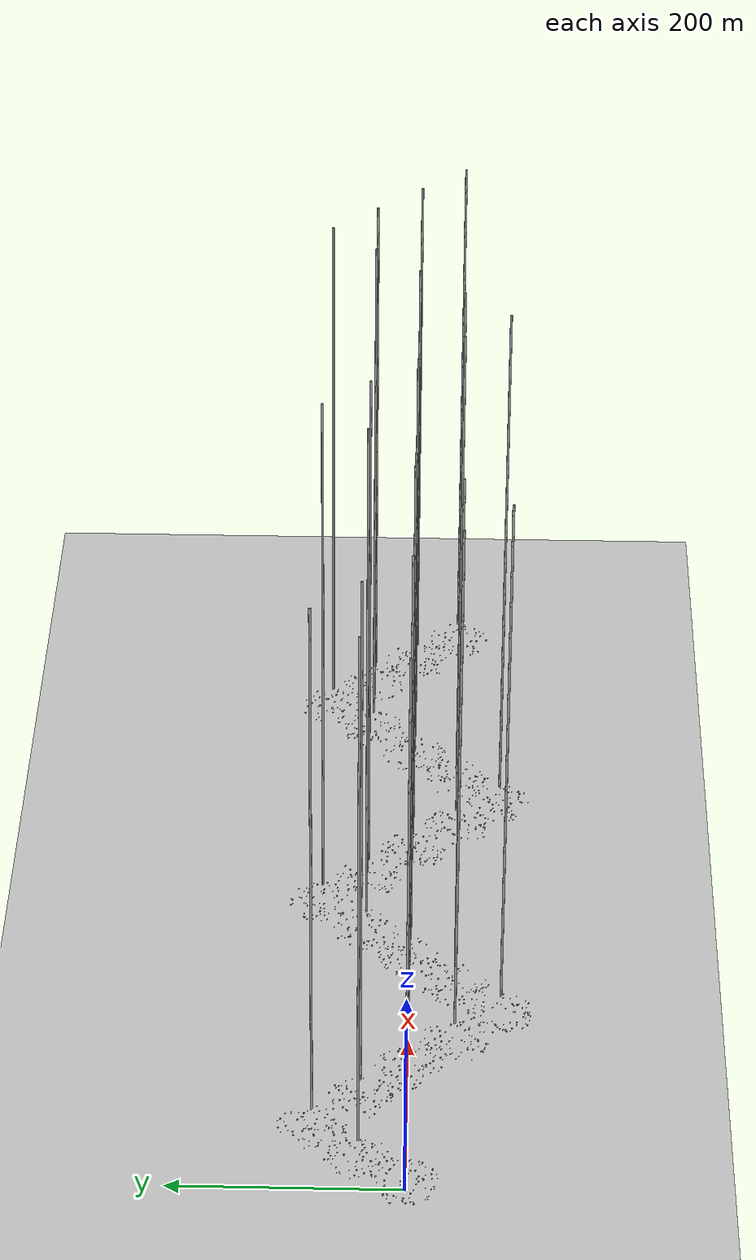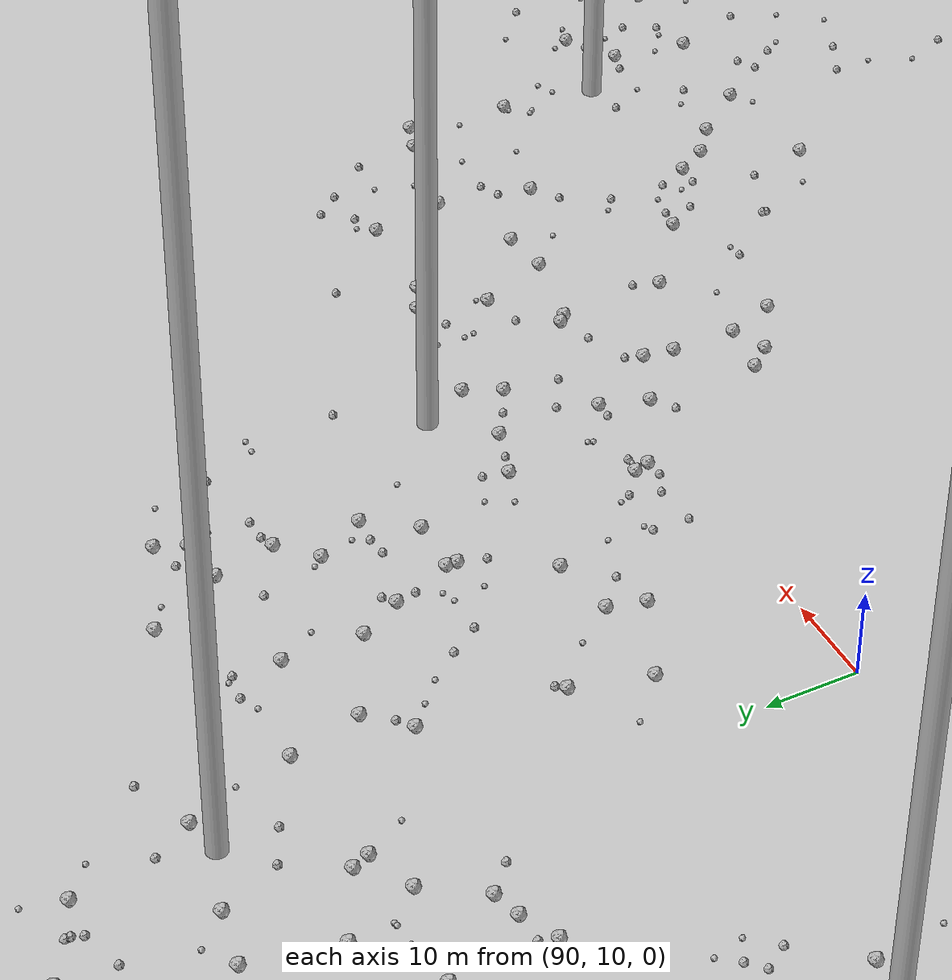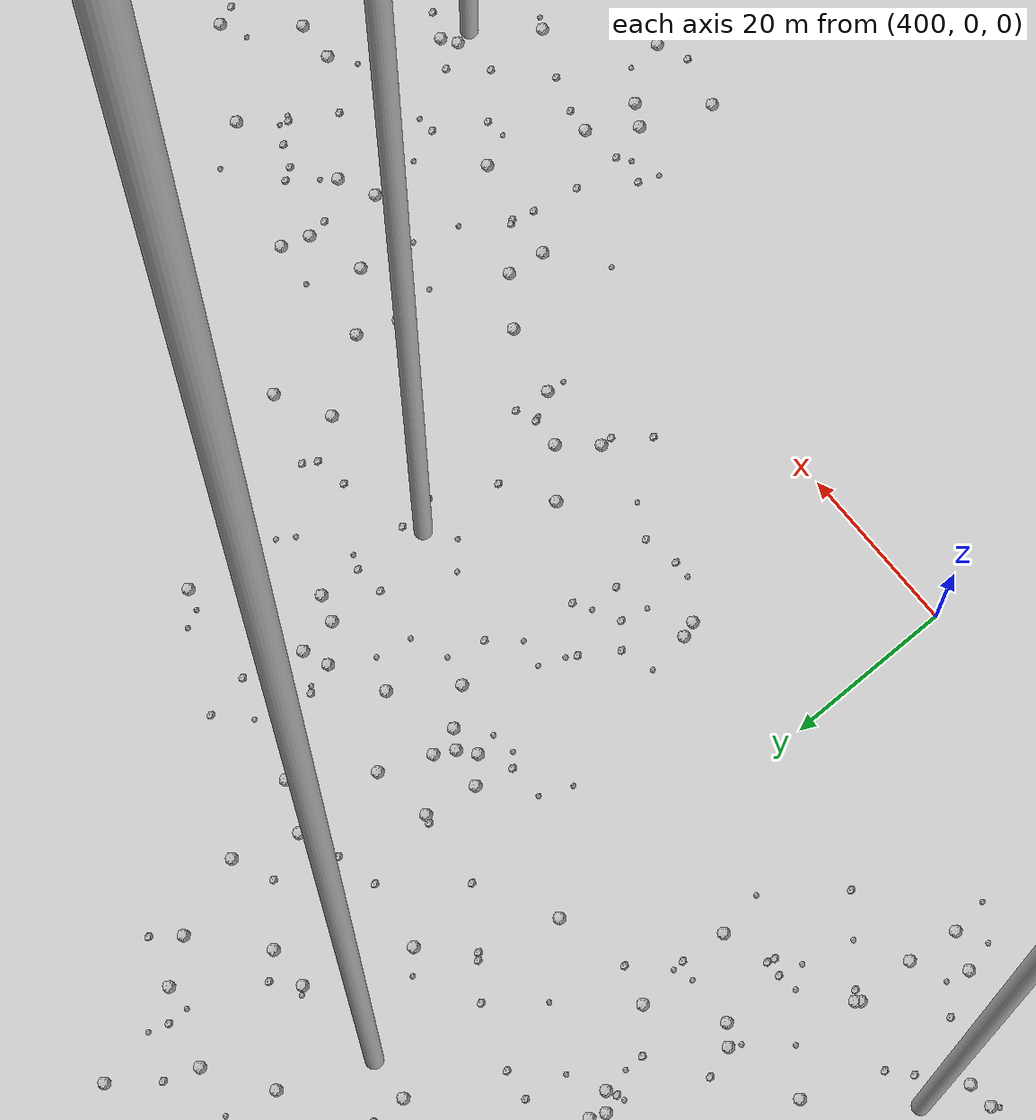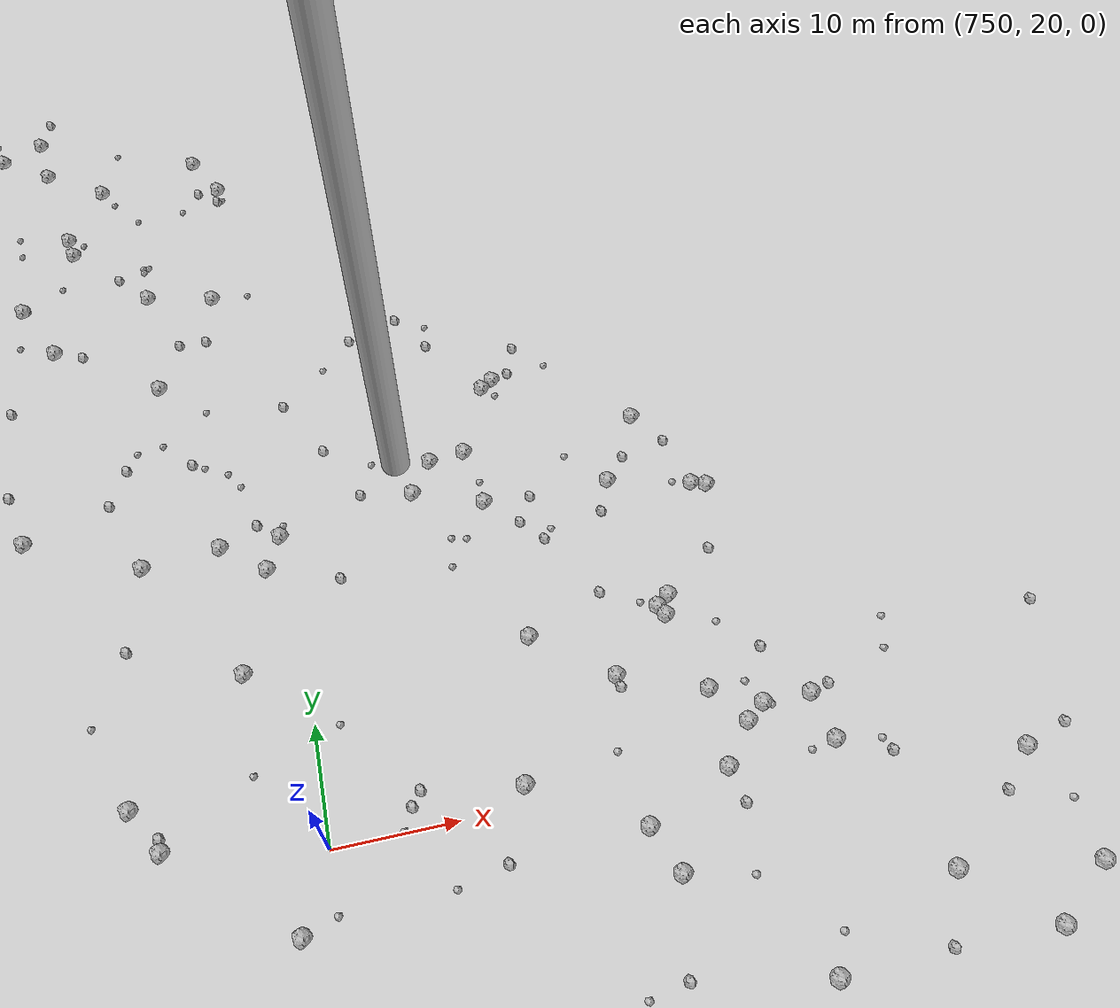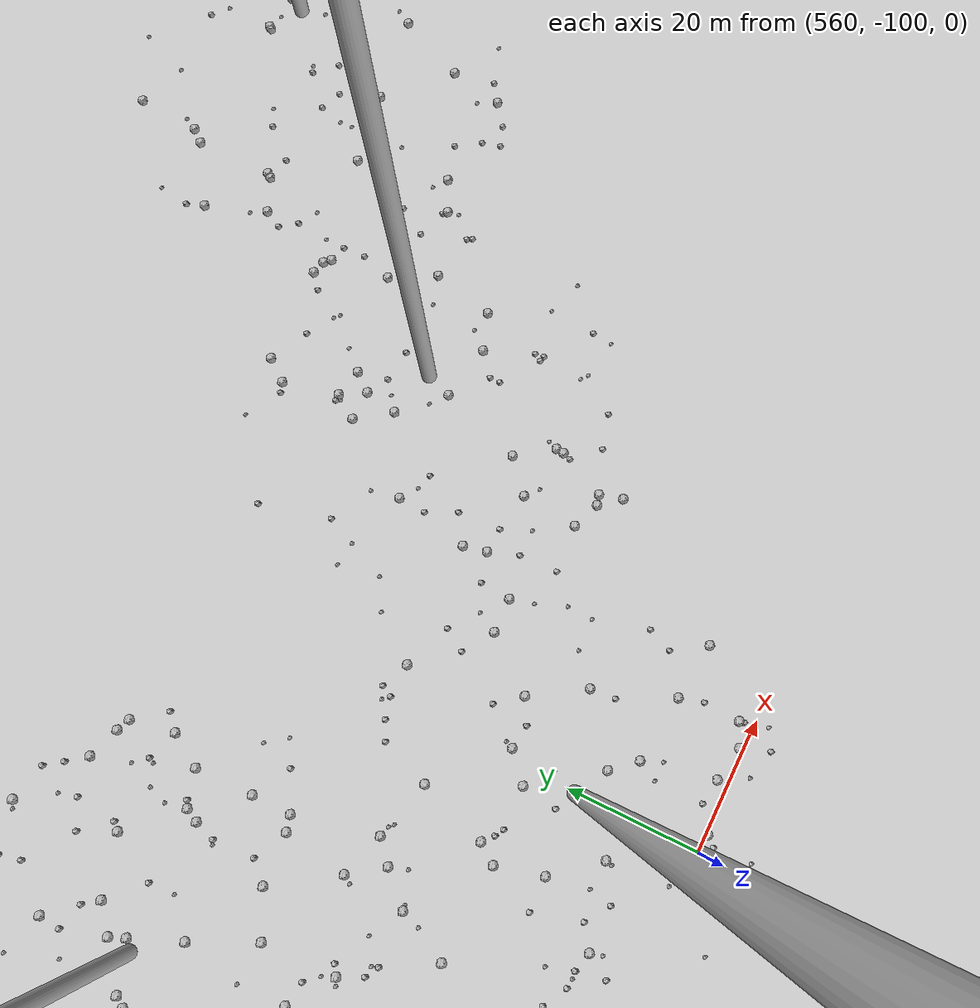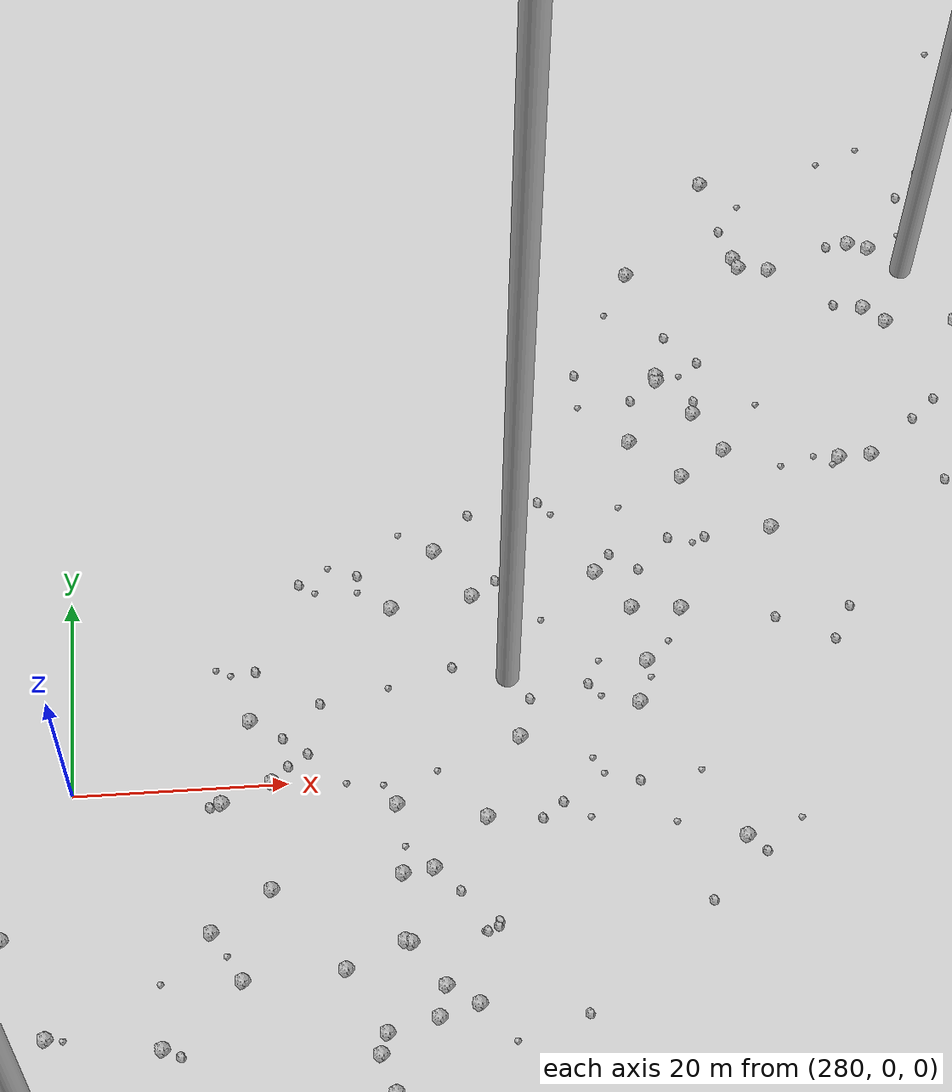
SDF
<sdf version="1.6">
 <world name="default">
  <include><uri>model://custom_ground</uri></include>
  <include><uri>model://sun</uri></include>
  <spherical_coordinates>
   <surface_model>EARTH_WGS84</surface_model>
   <latitude_deg>38.161479</latitude_deg>
   <longitude_deg>-122.454630</longitude_deg>
   <elevation>488.0</elevation>
   <heading_deg>90</heading_deg>
  </spherical_coordinates>
  <model name="rock1_0_0">
   <include><uri>model://rock1</uri><pose>3.8045434696196914 17.351324135746587 0.5 0 0 0</pose></include>
  </model>
  <model name="rock1_0_1">
   <include><uri>model://rock1</uri><pose>-3.976488632449062 -4.624608046511085 0.5 0 0 0</pose></include>
  </model>
  <model name="rock1_0_2">
   <include><uri>model://rock1</uri><pose>11.55652120269436 17.069664309525564 0.5 0 0 0</pose></include>
  </model>
  <model name="rock1_0_3">
   <include><uri>model://rock1</uri><pose>26.696960720430965 12.688559223585848 0.5 0 0 0</pose></include>
  </model>
  <model name="rock1_0_4">
   <include><uri>model://rock1</uri><pose>13.786341232884375 -15.468379948048705 0.5 0 0 0</pose></include>
  </model>
  <model name="rock1_0_5">
   <include><uri>model://rock1</uri><pose>14.90619966962199 -14.832727870366885 0.5 0 0 0</pose></include>
  </model>
  <model name="rock1_0_6">
   <include><uri>model://rock1</uri><pose>35.34807512818167 -14.194938023407197 0.5 0 0 0</pose></include>
  </model>
  <model name="rock1_0_7">
   <include><uri>model://rock1</uri><pose>-16.762229871484504 -0.9702952305546901 0.5 0 0 0</pose></include>
  </model>
  <model name="rock1_0_8">
   <include><uri>model://rock1</uri><pose>32.510787953866235 9.577859321746274 0.5 0 0 0</pose></include>
  </model>
  <model name="rock1_0_9">
   <include><uri>model://rock1</uri><pose>-7.665158341062368 9.148186438186173 0.5 0 0 0</pose></include>
  </model>
  <model name="rock1_0_10">
   <include><uri>model://rock1</uri><pose>-10.643128851662098 1.1007727395189129 0.5 0 0 0</pose></include>
  </model>
  <model name="rock1_0_11">
   <include><uri>model://rock1</uri><pose>-6.9607342781269 18.28509876694723 0.5 0 0 0</pose></include>
  </model>
  <model name="rock1_0_12">
   <include><uri>model://rock1</uri><pose>11.376963051131337 -11.007531407228694 0.5 0 0 0</pose></include>
  </model>
  <model name="rock1_0_13">
   <include><uri>model://rock1</uri><pose>18.245747287811454 -11.20185123404583 0.5 0 0 0</pose></include>
  </model>
  <model name="rock1_0_14">
   <include><uri>model://rock1</uri><pose>21.11028309529045 -21.652207632081094 0.5 0 0 0</pose></include>
  </model>
  <model name="rock1_0_15">
   <include><uri>model://rock1</uri><pose>18.78694139651263 28.01902566603456 0.5 0 0 0</pose></include>
  </model>
  <model name="rock1_0_16">
   <include><uri>model://rock1</uri><pose>2.2735610057466076 13.93864367170724 0.5 0 0 0</pose></include>
  </model>
  <model name="rock1_0_17">
   <include><uri>model://rock1</uri><pose>1.0628254207547236 20.970006711962185 0.5 0 0 0</pose></include>
  </model>
  <model name="rock1_0_18">
   <include><uri>model://rock1</uri><pose>6.064554483647978 0.8060660999381213 0.5 0 0 0</pose></include>
  </model>
  <model name="rock1_0_19">
   <include><uri>model://rock1</uri><pose>-5.27657413917729 18.229199491148535 0.5 0 0 0</pose></include>
  </model>
  <model name="rock1_0_20">
   <include><uri>model://rock1</uri><pose>21.287310065003233 -2.2464809159553916 0.5 0 0 0</pose></include>
  </model>
  <model name="rock1_0_21">
   <include><uri>model://rock1</uri><pose>1.252521747618374 27.557284686466552 0.5 0 0 0</pose></include>
  </model>
  <model name="rock1_0_22">
   <include><uri>model://rock1</uri><pose>27.21910487794426 -22.896482615510934 0.5 0 0 0</pose></include>
  </model>
  <model name="rock1_0_23">
   <include><uri>model://rock1</uri><pose>25.11424630611905 -8.23957948340589 0.5 0 0 0</pose></include>
  </model>
  <model name="rock1_0_24">
   <include><uri>model://rock1</uri><pose>25.02783431166965 -4.498878150979756 0.5 0 0 0</pose></include>
  </model>
  <model name="rock1_0_25">
   <include><uri>model://rock1</uri><pose>-17.733158886717213 -7.551293035537768 0.5 0 0 0</pose></include>
  </model>
  <model name="rock1_0_26">
   <include><uri>model://rock1</uri><pose>-16.646853796934494 12.2529617878346 0.5 0 0 0</pose></include>
  </model>
  <model name="rock2_0_0">
   <include><uri>model://rock2</uri><pose>1.7174081306215783 -21.639568211354778 0.3 0 0 0</pose></include>
  </model>
  <model name="rock2_0_1">
   <include><uri>model://rock2</uri><pose>21.27879759628778 15.305097346258513 0.3 0 0 0</pose></include>
  </model>
  <model name="rock2_0_2">
   <include><uri>model://rock2</uri><pose>15.588164283873539 -26.99316443540278 0.3 0 0 0</pose></include>
  </model>
  <model name="rock2_0_3">
   <include><uri>model://rock2</uri><pose>13.288594769338445 -15.48705388963626 0.3 0 0 0</pose></include>
  </model>
  <model name="rock2_0_4">
   <include><uri>model://rock2</uri><pose>15.114348207889229 -22.253335658589723 0.3 0 0 0</pose></include>
  </model>
  <model name="rock2_0_5">
   <include><uri>model://rock2</uri><pose>33.03203340092562 1.7290604279094062 0.3 0 0 0</pose></include>
  </model>
  <model name="rock2_0_6">
   <include><uri>model://rock2</uri><pose>21.470650093407222 -26.56450469514995 0.3 0 0 0</pose></include>
  </model>
  <model name="rock2_0_7">
   <include><uri>model://rock2</uri><pose>4.91474434177168 17.081404619136066 0.3 0 0 0</pose></include>
  </model>
  <model name="rock2_0_8">
   <include><uri>model://rock2</uri><pose>37.06323275518405 -11.389708964347399 0.3 0 0 0</pose></include>
  </model>
  <model name="rock2_0_9">
   <include><uri>model://rock2</uri><pose>2.8386917544996706 2.32544915256355 0.3 0 0 0</pose></include>
  </model>
  <model name="rock2_0_10">
   <include><uri>model://rock2</uri><pose>-14.41645054304514 -4.816949751562277 0.3 0 0 0</pose></include>
  </model>
  <model name="rock2_0_11">
   <include><uri>model://rock2</uri><pose>0.062494436806133535 -7.031599284485701 0.3 0 0 0</pose></include>
  </model>
  <model name="rock2_0_12">
   <include><uri>model://rock2</uri><pose>1.136232632607122 22.76787955329445 0.3 0 0 0</pose></include>
  </model>
  <model name="rock2_0_13">
   <include><uri>model://rock2</uri><pose>5.252303429433031 -24.104071772358786 0.3 0 0 0</pose></include>
  </model>
  <model name="rock2_0_14">
   <include><uri>model://rock2</uri><pose>-14.487152391609118 1.5786134675320405 0.3 0 0 0</pose></include>
  </model>
  <model name="rock2_0_15">
   <include><uri>model://rock2</uri><pose>8.008608175824513 -9.168432203266239 0.3 0 0 0</pose></include>
  </model>
  <model name="rock2_0_16">
   <include><uri>model://rock2</uri><pose>11.32976871381565 4.100525088918239 0.3 0 0 0</pose></include>
  </model>
  <model name="rock2_0_17">
   <include><uri>model://rock2</uri><pose>25.60045474019781 13.705765755030022 0.3 0 0 0</pose></include>
  </model>
  <model name="rock2_0_18">
   <include><uri>model://rock2</uri><pose>14.900492650213756 -9.630991838835428 0.3 0 0 0</pose></include>
  </model>
  <model name="rock2_0_19">
   <include><uri>model://rock2</uri><pose>-9.987863982449268 -4.019426401484505 0.3 0 0 0</pose></include>
  </model>
  <model name="rock2_0_20">
   <include><uri>model://rock2</uri><pose>-8.420865494883877 -18.691552369575692 0.3 0 0 0</pose></include>
  </model>
  <model name="rock2_0_21">
   <include><uri>model://rock2</uri><pose>-6.569870950592874 14.447162049023788 0.3 0 0 0</pose></include>
  </model>
  <model name="rock2_0_22">
   <include><uri>model://rock2</uri><pose>19.947017476269465 -16.808944370218057 0.3 0 0 0</pose></include>
  </model>
  <model name="rock2_0_23">
   <include><uri>model://rock2</uri><pose>-14.488412720358138 -7.284083058440789 0.3 0 0 0</pose></include>
  </model>
  <model name="rock2_0_24">
   <include><uri>model://rock2</uri><pose>2.9287895169486973 -17.199780521790803 0.3 0 0 0</pose></include>
  </model>
  <model name="rock2_0_25">
   <include><uri>model://rock2</uri><pose>37.662391992678195 -3.249237462348372 0.3 0 0 0</pose></include>
  </model>
  <model name="rock2_0_26">
   <include><uri>model://rock2</uri><pose>39.47529828380392 -4.280047330851765 0.3 0 0 0</pose></include>
  </model>
  <model name="rock3_0_0">
   <include><uri>model://rock3</uri><pose>6.711916135207659 3.8279733502093904 0.2 0 0 0</pose></include>
  </model>
  <model name="rock3_0_1">
   <include><uri>model://rock3</uri><pose>-16.038695205809695 -13.789994399857417 0.2 0 0 0</pose></include>
  </model>
  <model name="rock3_0_2">
   <include><uri>model://rock3</uri><pose>3.262938108446381 -23.560145180377017 0.2 0 0 0</pose></include>
  </model>
  <model name="rock3_0_3">
   <include><uri>model://rock3</uri><pose>-11.361445137253277 15.03748853373542 0.2 0 0 0</pose></include>
  </model>
  <model name="rock3_0_4">
   <include><uri>model://rock3</uri><pose>2.509164629949339 27.89971112531226 0.2 0 0 0</pose></include>
  </model>
  <model name="rock3_0_5">
   <include><uri>model://rock3</uri><pose>-8.770937807183415 6.7343373540365405 0.2 0 0 0</pose></include>
  </model>
  <model name="rock3_0_6">
   <include><uri>model://rock3</uri><pose>2.5984802924547488 26.73247101775727 0.2 0 0 0</pose></include>
  </model>
  <model name="rock3_0_7">
   <include><uri>model://rock3</uri><pose>6.697028036166579 16.53530980398223 0.2 0 0 0</pose></include>
  </model>
  <model name="rock3_0_8">
   <include><uri>model://rock3</uri><pose>-5.321486271432832 15.139209935361684 0.2 0 0 0</pose></include>
  </model>
  <model name="rock3_0_9">
   <include><uri>model://rock3</uri><pose>2.437311870701997 -24.482324498612954 0.2 0 0 0</pose></include>
  </model>
  <model name="rock3_0_10">
   <include><uri>model://rock3</uri><pose>20.84346778148231 -17.8642485614278 0.2 0 0 0</pose></include>
  </model>
  <model name="rock3_0_11">
   <include><uri>model://rock3</uri><pose>-12.40089053037364 2.329488971127809 0.2 0 0 0</pose></include>
  </model>
  <model name="rock3_0_12">
   <include><uri>model://rock3</uri><pose>30.185485529246712 -16.77558903735834 0.2 0 0 0</pose></include>
  </model>
  <model name="rock3_0_13">
   <include><uri>model://rock3</uri><pose>3.7184752453918577 -23.588972399634088 0.2 0 0 0</pose></include>
  </model>
  <model name="rock3_0_14">
   <include><uri>model://rock3</uri><pose>1.234896450513439 -4.683382949180025 0.2 0 0 0</pose></include>
  </model>
  <model name="rock3_0_15">
   <include><uri>model://rock3</uri><pose>20.334327987806688 19.937453226177247 0.2 0 0 0</pose></include>
  </model>
  <model name="rock3_0_16">
   <include><uri>model://rock3</uri><pose>32.49420394468977 8.997996145547276 0.2 0 0 0</pose></include>
  </model>
  <model name="rock3_0_17">
   <include><uri>model://rock3</uri><pose>36.987123041733234 -2.9762910311139414 0.2 0 0 0</pose></include>
  </model>
  <model name="rock3_0_18">
   <include><uri>model://rock3</uri><pose>14.914299045146379 24.70179243779249 0.2 0 0 0</pose></include>
  </model>
  <model name="rock3_0_19">
   <include><uri>model://rock3</uri><pose>-10.752501350344952 -19.193104151361005 0.2 0 0 0</pose></include>
  </model>
  <model name="rock3_0_20">
   <include><uri>model://rock3</uri><pose>28.65413894756972 19.259821169439 0.2 0 0 0</pose></include>
  </model>
  <model name="rock3_0_21">
   <include><uri>model://rock3</uri><pose>33.61742288306974 -12.168720375505487 0.2 0 0 0</pose></include>
  </model>
  <model name="rock3_0_22">
   <include><uri>model://rock3</uri><pose>34.14020246028839 -5.078852081255366 0.2 0 0 0</pose></include>
  </model>
  <model name="rock3_0_23">
   <include><uri>model://rock3</uri><pose>9.647557341416384 23.563663243258596 0.2 0 0 0</pose></include>
  </model>
  <model name="rock3_0_24">
   <include><uri>model://rock3</uri><pose>-7.338256465114528 -19.7575352392037 0.2 0 0 0</pose></include>
  </model>
  <model name="rock3_0_25">
   <include><uri>model://rock3</uri><pose>37.97269338269484 6.656470017388898 0.2 0 0 0</pose></include>
  </model>
  <model name="rock3_0_26">
   <include><uri>model://rock3</uri><pose>-11.294956588863574 -17.234473470509208 0.2 0 0 0</pose></include>
  </model>
  <model name="rock1_1_0">
   <include><uri>model://rock1</uri><pose>21.019350020886073 34.46737954065138 0.5 0 0 0</pose></include>
  </model>
  <model name="rock1_1_1">
   <include><uri>model://rock1</uri><pose>40.374613950986 11.787330659966312 0.5 0 0 0</pose></include>
  </model>
  <model name="rock1_1_2">
   <include><uri>model://rock1</uri><pose>24.390686280847365 40.785579554524965 0.5 0 0 0</pose></include>
  </model>
  <model name="rock1_1_3">
   <include><uri>model://rock1</uri><pose>46.75947036063916 64.71042892200376 0.5 0 0 0</pose></include>
  </model>
  <model name="rock1_1_4">
   <include><uri>model://rock1</uri><pose>54.4227164619537 28.279505699599127 0.5 0 0 0</pose></include>
  </model>
  <model name="rock1_1_5">
   <include><uri>model://rock1</uri><pose>63.192546642869814 50.002066193742884 0.5 0 0 0</pose></include>
  </model>
  <model name="rock1_1_6">
   <include><uri>model://rock1</uri><pose>37.91992223887273 68.09365726082211 0.5 0 0 0</pose></include>
  </model>
  <model name="rock1_1_7">
   <include><uri>model://rock1</uri><pose>16.957002972674985 24.694829687988292 0.5 0 0 0</pose></include>
  </model>
  <model name="rock1_1_8">
   <include><uri>model://rock1</uri><pose>46.99471204580336 57.370814577122545 0.5 0 0 0</pose></include>
  </model>
  <model name="rock1_1_9">
   <include><uri>model://rock1</uri><pose>41.84944802190444 17.80196562988679 0.5 0 0 0</pose></include>
  </model>
  <model name="rock1_1_10">
   <include><uri>model://rock1</uri><pose>37.2569961999657 36.15316085992687 0.5 0 0 0</pose></include>
  </model>
  <model name="rock1_1_11">
   <include><uri>model://rock1</uri><pose>41.87525428641569 35.44008999229401 0.5 0 0 0</pose></include>
  </model>
  <model name="rock1_1_12">
   <include><uri>model://rock1</uri><pose>32.51265501596435 22.255587068929017 0.5 0 0 0</pose></include>
  </model>
  <model name="rock1_1_13">
   <include><uri>model://rock1</uri><pose>38.250541264396176 64.88081847311416 0.5 0 0 0</pose></include>
  </model>
  <model name="rock1_1_14">
   <include><uri>model://rock1</uri><pose>17.9452955485231 42.09682445358128 0.5 0 0 0</pose></include>
  </model>
  <model name="rock1_1_15">
   <include><uri>model://rock1</uri><pose>36.41620371619965 29.082207316938845 0.5 0 0 0</pose></include>
  </model>
  <model name="rock1_1_16">
   <include><uri>model://rock1</uri><pose>59.732972730104414 47.51686510041698 0.5 0 0 0</pose></include>
  </model>
  <model name="rock1_1_17">
   <include><uri>model://rock1</uri><pose>23.057974351856124 28.58360711642848 0.5 0 0 0</pose></include>
  </model>
  <model name="rock1_1_18">
   <include><uri>model://rock1</uri><pose>35.74957945760827 40.7766080869483 0.5 0 0 0</pose></include>
  </model>
  <model name="rock1_1_19">
   <include><uri>model://rock1</uri><pose>37.15072351547825 15.847694441922668 0.5 0 0 0</pose></include>
  </model>
  <model name="rock1_1_20">
   <include><uri>model://rock1</uri><pose>53.75688750853977 34.61515687987525 0.5 0 0 0</pose></include>
  </model>
  <model name="rock1_1_21">
   <include><uri>model://rock1</uri><pose>21.221156749587347 34.07385776763242 0.5 0 0 0</pose></include>
  </model>
  <model name="rock1_1_22">
   <include><uri>model://rock1</uri><pose>34.725950151358006 21.907888366290393 0.5 0 0 0</pose></include>
  </model>
  <model name="rock1_1_23">
   <include><uri>model://rock1</uri><pose>57.938945219809035 36.120208728616184 0.5 0 0 0</pose></include>
  </model>
  <model name="rock1_1_24">
   <include><uri>model://rock1</uri><pose>58.93481034611107 28.04439151833257 0.5 0 0 0</pose></include>
  </model>
  <model name="rock1_1_25">
   <include><uri>model://rock1</uri><pose>47.439739778194834 32.51198876436398 0.5 0 0 0</pose></include>
  </model>
  <model name="rock1_1_26">
   <include><uri>model://rock1</uri><pose>44.207764061267746 51.97931973772234 0.5 0 0 0</pose></include>
  </model>
  <model name="rock2_1_0">
   <include><uri>model://rock2</uri><pose>43.04308270718656 62.72382624129587 0.3 0 0 0</pose></include>
  </model>
  <model name="rock2_1_1">
   <include><uri>model://rock2</uri><pose>29.63485365316266 41.46464442739434 0.3 0 0 0</pose></include>
  </model>
  <model name="rock2_1_2">
   <include><uri>model://rock2</uri><pose>53.445674340119034 43.12499422030625 0.3 0 0 0</pose></include>
  </model>
  <model name="rock2_1_3">
   <include><uri>model://rock2</uri><pose>44.984398073442925 38.528347470355655 0.3 0 0 0</pose></include>
  </model>
  <model name="rock2_1_4">
   <include><uri>model://rock2</uri><pose>20.00165690689068 54.36629315276247 0.3 0 0 0</pose></include>
  </model>
  <model name="rock2_1_5">
   <include><uri>model://rock2</uri><pose>20.469099599787732 56.813174471639826 0.3 0 0 0</pose></include>
  </model>
  <model name="rock2_1_6">
   <include><uri>model://rock2</uri><pose>27.54230159950804 57.890894136480355 0.3 0 0 0</pose></include>
  </model>
  <model name="rock2_1_7">
   <include><uri>model://rock2</uri><pose>51.33552844940788 36.374258458228056 0.3 0 0 0</pose></include>
  </model>
  <model name="rock2_1_8">
   <include><uri>model://rock2</uri><pose>66.6062591267507 50.808362002836446 0.3 0 0 0</pose></include>
  </model>
  <model name="rock2_1_9">
   <include><uri>model://rock2</uri><pose>64.05420290886343 34.20314214706974 0.3 0 0 0</pose></include>
  </model>
  <model name="rock2_1_10">
   <include><uri>model://rock2</uri><pose>62.38437547258623 36.74154067109148 0.3 0 0 0</pose></include>
  </model>
  <model name="rock2_1_11">
   <include><uri>model://rock2</uri><pose>59.524856904801055 55.1873128785674 0.3 0 0 0</pose></include>
  </model>
  <model name="rock2_1_12">
   <include><uri>model://rock2</uri><pose>43.144915092465354 58.88248490977714 0.3 0 0 0</pose></include>
  </model>
  <model name="rock2_1_13">
   <include><uri>model://rock2</uri><pose>39.3421944252609 24.80878588811606 0.3 0 0 0</pose></include>
  </model>
  <model name="rock2_1_14">
   <include><uri>model://rock2</uri><pose>64.03027754764872 38.26409924224609 0.3 0 0 0</pose></include>
  </model>
  <model name="rock2_1_15">
   <include><uri>model://rock2</uri><pose>26.54341757750625 35.99930384325666 0.3 0 0 0</pose></include>
  </model>
  <model name="rock2_1_16">
   <include><uri>model://rock2</uri><pose>38.82740242326298 61.072290187573486 0.3 0 0 0</pose></include>
  </model>
  <model name="rock2_1_17">
   <include><uri>model://rock2</uri><pose>32.59886029718477 24.452430450619595 0.3 0 0 0</pose></include>
  </model>
  <model name="rock2_1_18">
   <include><uri>model://rock2</uri><pose>54.795158472745086 64.04774166663402 0.3 0 0 0</pose></include>
  </model>
  <model name="rock2_1_19">
   <include><uri>model://rock2</uri><pose>56.81427051243365 59.80626174579507 0.3 0 0 0</pose></include>
  </model>
  <model name="rock2_1_20">
   <include><uri>model://rock2</uri><pose>16.673698194441478 38.89472053235245 0.3 0 0 0</pose></include>
  </model>
  <model name="rock2_1_21">
   <include><uri>model://rock2</uri><pose>50.05265100176987 64.09246174615541 0.3 0 0 0</pose></include>
  </model>
  <model name="rock2_1_22">
   <include><uri>model://rock2</uri><pose>49.24794472213128 15.042507756651183 0.3 0 0 0</pose></include>
  </model>
  <model name="rock2_1_23">
   <include><uri>model://rock2</uri><pose>42.850718261439646 51.34599274578882 0.3 0 0 0</pose></include>
  </model>
  <model name="rock2_1_24">
   <include><uri>model://rock2</uri><pose>22.211843050204088 55.23807962559662 0.3 0 0 0</pose></include>
  </model>
  <model name="rock2_1_25">
   <include><uri>model://rock2</uri><pose>49.59305813343 23.48536003985945 0.3 0 0 0</pose></include>
  </model>
  <model name="rock2_1_26">
   <include><uri>model://rock2</uri><pose>55.635859243748655 46.20013872341365 0.3 0 0 0</pose></include>
  </model>
  <model name="rock3_1_0">
   <include><uri>model://rock3</uri><pose>57.649125606654614 25.761149062584533 0.2 0 0 0</pose></include>
  </model>
  <model name="rock3_1_1">
   <include><uri>model://rock3</uri><pose>32.19973140191395 61.84855997567275 0.2 0 0 0</pose></include>
  </model>
  <model name="rock3_1_2">
   <include><uri>model://rock3</uri><pose>53.948944501562266 41.986899755443034 0.2 0 0 0</pose></include>
  </model>
  <model name="rock3_1_3">
   <include><uri>model://rock3</uri><pose>35.536574708575046 47.86612965884392 0.2 0 0 0</pose></include>
  </model>
  <model name="rock3_1_4">
   <include><uri>model://rock3</uri><pose>30.113410225760845 30.444599506988826 0.2 0 0 0</pose></include>
  </model>
  <model name="rock3_1_5">
   <include><uri>model://rock3</uri><pose>16.341543797946073 27.818206499562706 0.2 0 0 0</pose></include>
  </model>
  <model name="rock3_1_6">
   <include><uri>model://rock3</uri><pose>24.34501830396842 46.91092102699212 0.2 0 0 0</pose></include>
  </model>
  <model name="rock3_1_7">
   <include><uri>model://rock3</uri><pose>65.68498190098556 40.200015173028675 0.2 0 0 0</pose></include>
  </model>
  <model name="rock3_1_8">
   <include><uri>model://rock3</uri><pose>27.74081408956749 16.544392735516833 0.2 0 0 0</pose></include>
  </model>
  <model name="rock3_1_9">
   <include><uri>model://rock3</uri><pose>48.283509187207336 38.10437279847912 0.2 0 0 0</pose></include>
  </model>
  <model name="rock3_1_10">
   <include><uri>model://rock3</uri><pose>48.59784188283857 37.375733532236026 0.2 0 0 0</pose></include>
  </model>
  <model name="rock3_1_11">
   <include><uri>model://rock3</uri><pose>31.365349160614752 39.68325551632704 0.2 0 0 0</pose></include>
  </model>
  <model name="rock3_1_12">
   <include><uri>model://rock3</uri><pose>24.742487647095526 21.911565884746317 0.2 0 0 0</pose></include>
  </model>
  <model name="rock3_1_13">
   <include><uri>model://rock3</uri><pose>21.979438285508746 16.365186885931443 0.2 0 0 0</pose></include>
  </model>
  <model name="rock3_1_14">
   <include><uri>model://rock3</uri><pose>66.53632358304827 36.82971028882966 0.2 0 0 0</pose></include>
  </model>
  <model name="rock3_1_15">
   <include><uri>model://rock3</uri><pose>26.22922253523648 41.91844350842181 0.2 0 0 0</pose></include>
  </model>
  <model name="rock3_1_16">
   <include><uri>model://rock3</uri><pose>30.27981091053326 27.356733980677603 0.2 0 0 0</pose></include>
  </model>
  <model name="rock3_1_17">
   <include><uri>model://rock3</uri><pose>59.82100375154426 20.35988325333277 0.2 0 0 0</pose></include>
  </model>
  <model name="rock3_1_18">
   <include><uri>model://rock3</uri><pose>53.25483867927239 57.7233878943308 0.2 0 0 0</pose></include>
  </model>
  <model name="rock3_1_19">
   <include><uri>model://rock3</uri><pose>31.69178493238378 28.862489712118403 0.2 0 0 0</pose></include>
  </model>
  <model name="rock3_1_20">
   <include><uri>model://rock3</uri><pose>48.1574961572929 23.689992067612284 0.2 0 0 0</pose></include>
  </model>
  <model name="rock3_1_21">
   <include><uri>model://rock3</uri><pose>11.497319680522715 35.4135184129507 0.2 0 0 0</pose></include>
  </model>
  <model name="rock3_1_22">
   <include><uri>model://rock3</uri><pose>33.98849382734142 61.53163883779508 0.2 0 0 0</pose></include>
  </model>
  <model name="rock3_1_23">
   <include><uri>model://rock3</uri><pose>46.00309743725033 19.428565394596397 0.2 0 0 0</pose></include>
  </model>
  <model name="rock3_1_24">
   <include><uri>model://rock3</uri><pose>38.065589648683954 10.268407996742122 0.2 0 0 0</pose></include>
  </model>
  <model name="rock3_1_25">
   <include><uri>model://rock3</uri><pose>36.430297492447515 27.872186214027856 0.2 0 0 0</pose></include>
  </model>
  <model name="rock3_1_26">
   <include><uri>model://rock3</uri><pose>14.078472522203256 45.641123736777025 0.2 0 0 0</pose></include>
  </model>
  <model name="rock1_2_0">
   <include><uri>model://rock1</uri><pose>55.21185368888403 73.76881646875583 0.5 0 0 0</pose></include>
  </model>
  <model name="rock1_2_1">
   <include><uri>model://rock1</uri><pose>78.83987338813614 65.33785615378929 0.5 0 0 0</pose></include>
  </model>
  <model name="rock1_2_2">
   <include><uri>model://rock1</uri><pose>68.69666408258976 77.70432595903239 0.5 0 0 0</pose></include>
  </model>
  <model name="rock1_2_3">
   <include><uri>model://rock1</uri><pose>89.14897034547381 92.21551105507174 0.5 0 0 0</pose></include>
  </model>
  <model name="rock1_2_4">
   <include><uri>model://rock1</uri><pose>80.75298410347993 101.66661624831949 0.5 0 0 0</pose></include>
  </model>
  <model name="rock1_2_5">
   <include><uri>model://rock1</uri><pose>69.70873435126099 60.922657810823665 0.5 0 0 0</pose></include>
  </model>
  <model name="rock1_2_6">
   <include><uri>model://rock1</uri><pose>77.82787932075043 52.92551489041177 0.5 0 0 0</pose></include>
  </model>
  <model name="rock1_2_7">
   <include><uri>model://rock1</uri><pose>77.55328435516203 80.04675020700007 0.5 0 0 0</pose></include>
  </model>
  <model name="rock1_2_8">
   <include><uri>model://rock1</uri><pose>89.54137070751143 63.32839881531708 0.5 0 0 0</pose></include>
  </model>
  <model name="rock1_2_9">
   <include><uri>model://rock1</uri><pose>78.3566711597525 108.24468045558957 0.5 0 0 0</pose></include>
  </model>
  <model name="rock1_2_10">
   <include><uri>model://rock1</uri><pose>81.87897626373187 67.56937380666031 0.5 0 0 0</pose></include>
  </model>
  <model name="rock1_2_11">
   <include><uri>model://rock1</uri><pose>90.28275463572706 75.79532298180841 0.5 0 0 0</pose></include>
  </model>
  <model name="rock1_2_12">
   <include><uri>model://rock1</uri><pose>74.00031315144446 87.43709322741505 0.5 0 0 0</pose></include>
  </model>
  <model name="rock1_2_13">
   <include><uri>model://rock1</uri><pose>68.43817673288146 95.1509818984982 0.5 0 0 0</pose></include>
  </model>
  <model name="rock1_2_14">
   <include><uri>model://rock1</uri><pose>73.82429130333512 51.08948783130203 0.5 0 0 0</pose></include>
  </model>
  <model name="rock1_2_15">
   <include><uri>model://rock1</uri><pose>77.01935519761108 86.38461593748275 0.5 0 0 0</pose></include>
  </model>
  <model name="rock1_2_16">
   <include><uri>model://rock1</uri><pose>90.32418463946564 61.37294374328147 0.5 0 0 0</pose></include>
  </model>
  <model name="rock1_2_17">
   <include><uri>model://rock1</uri><pose>73.32718628971534 95.63446641450614 0.5 0 0 0</pose></include>
  </model>
  <model name="rock1_2_18">
   <include><uri>model://rock1</uri><pose>73.79798142973723 61.95953368429122 0.5 0 0 0</pose></include>
  </model>
  <model name="rock1_2_19">
   <include><uri>model://rock1</uri><pose>80.97930645498607 53.70282206029968 0.5 0 0 0</pose></include>
  </model>
  <model name="rock1_2_20">
   <include><uri>model://rock1</uri><pose>59.062397588138715 73.60057440779867 0.5 0 0 0</pose></include>
  </model>
  <model name="rock1_2_21">
   <include><uri>model://rock1</uri><pose>83.98938306698098 77.14196572608452 0.5 0 0 0</pose></include>
  </model>
  <model name="rock1_2_22">
   <include><uri>model://rock1</uri><pose>89.83736599951291 107.0482554035828 0.5 0 0 0</pose></include>
  </model>
  <model name="rock1_2_23">
   <include><uri>model://rock1</uri><pose>101.24128143325429 73.96362573835697 0.5 0 0 0</pose></include>
  </model>
  <model name="rock1_2_24">
   <include><uri>model://rock1</uri><pose>85.02089588781496 59.583269950931985 0.5 0 0 0</pose></include>
  </model>
  <model name="rock1_2_25">
   <include><uri>model://rock1</uri><pose>97.7167369310269 87.17008164037071 0.5 0 0 0</pose></include>
  </model>
  <model name="rock1_2_26">
   <include><uri>model://rock1</uri><pose>77.04210975713062 81.96440723051728 0.5 0 0 0</pose></include>
  </model>
  <model name="rock2_2_0">
   <include><uri>model://rock2</uri><pose>107.75507584101192 76.4659017972892 0.3 0 0 0</pose></include>
  </model>
  <model name="rock2_2_1">
   <include><uri>model://rock2</uri><pose>83.8830002908027 50.88762030726914 0.3 0 0 0</pose></include>
  </model>
  <model name="rock2_2_2">
   <include><uri>model://rock2</uri><pose>99.8895482618268 97.78175143181987 0.3 0 0 0</pose></include>
  </model>
  <model name="rock2_2_3">
   <include><uri>model://rock2</uri><pose>62.646632596098755 90.27245016010276 0.3 0 0 0</pose></include>
  </model>
  <model name="rock2_2_4">
   <include><uri>model://rock2</uri><pose>64.33695356216856 86.96488029862661 0.3 0 0 0</pose></include>
  </model>
  <model name="rock2_2_5">
   <include><uri>model://rock2</uri><pose>97.58467258422627 103.07585635166444 0.3 0 0 0</pose></include>
  </model>
  <model name="rock2_2_6">
   <include><uri>model://rock2</uri><pose>61.03287644473977 81.40246105819256 0.3 0 0 0</pose></include>
  </model>
  <model name="rock2_2_7">
   <include><uri>model://rock2</uri><pose>61.96696907491256 59.396040910049074 0.3 0 0 0</pose></include>
  </model>
  <model name="rock2_2_8">
   <include><uri>model://rock2</uri><pose>76.09104473543087 77.253083071044 0.3 0 0 0</pose></include>
  </model>
  <model name="rock2_2_9">
   <include><uri>model://rock2</uri><pose>53.66610256735274 75.9750373980604 0.3 0 0 0</pose></include>
  </model>
  <model name="rock2_2_10">
   <include><uri>model://rock2</uri><pose>78.93857267678426 62.88843915410848 0.3 0 0 0</pose></include>
  </model>
  <model name="rock2_2_11">
   <include><uri>model://rock2</uri><pose>88.771376242753 86.21936655654964 0.3 0 0 0</pose></include>
  </model>
  <model name="rock2_2_12">
   <include><uri>model://rock2</uri><pose>93.00083721586256 69.06261099840569 0.3 0 0 0</pose></include>
  </model>
  <model name="rock2_2_13">
   <include><uri>model://rock2</uri><pose>93.67893757642469 88.66487752569273 0.3 0 0 0</pose></include>
  </model>
  <model name="rock2_2_14">
   <include><uri>model://rock2</uri><pose>97.08603048979597 66.9482076953262 0.3 0 0 0</pose></include>
  </model>
  <model name="rock2_2_15">
   <include><uri>model://rock2</uri><pose>97.67468008068812 97.96024587783164 0.3 0 0 0</pose></include>
  </model>
  <model name="rock2_2_16">
   <include><uri>model://rock2</uri><pose>70.27854570802319 77.45362398311309 0.3 0 0 0</pose></include>
  </model>
  <model name="rock2_2_17">
   <include><uri>model://rock2</uri><pose>98.76789509325079 78.35186288840737 0.3 0 0 0</pose></include>
  </model>
  <model name="rock2_2_18">
   <include><uri>model://rock2</uri><pose>74.41749127672698 52.856880908769114 0.3 0 0 0</pose></include>
  </model>
  <model name="rock2_2_19">
   <include><uri>model://rock2</uri><pose>72.16890878576847 105.81513847230863 0.3 0 0 0</pose></include>
  </model>
  <model name="rock2_2_20">
   <include><uri>model://rock2</uri><pose>70.53172947655396 78.36539981306191 0.3 0 0 0</pose></include>
  </model>
  <model name="rock2_2_21">
   <include><uri>model://rock2</uri><pose>78.04009465411906 84.65411779262956 0.3 0 0 0</pose></include>
  </model>
  <model name="rock2_2_22">
   <include><uri>model://rock2</uri><pose>93.68214771831516 89.22646157115824 0.3 0 0 0</pose></include>
  </model>
  <model name="rock2_2_23">
   <include><uri>model://rock2</uri><pose>100.35991379879317 94.84465093349692 0.3 0 0 0</pose></include>
  </model>
  <model name="rock2_2_24">
   <include><uri>model://rock2</uri><pose>72.71154214839659 53.805925027595684 0.3 0 0 0</pose></include>
  </model>
  <model name="rock2_2_25">
   <include><uri>model://rock2</uri><pose>93.2500157443848 87.51509299838747 0.3 0 0 0</pose></include>
  </model>
  <model name="rock2_2_26">
   <include><uri>model://rock2</uri><pose>81.32725893091074 83.60369336616999 0.3 0 0 0</pose></include>
  </model>
  <model name="rock3_2_0">
   <include><uri>model://rock3</uri><pose>86.6487566731237 103.39988891637614 0.2 0 0 0</pose></include>
  </model>
  <model name="rock3_2_1">
   <include><uri>model://rock3</uri><pose>76.17843205005485 68.83780869329651 0.2 0 0 0</pose></include>
  </model>
  <model name="rock3_2_2">
   <include><uri>model://rock3</uri><pose>101.04836951114345 84.08456044525573 0.2 0 0 0</pose></include>
  </model>
  <model name="rock3_2_3">
   <include><uri>model://rock3</uri><pose>78.60455788262117 106.36116668052722 0.2 0 0 0</pose></include>
  </model>
  <model name="rock3_2_4">
   <include><uri>model://rock3</uri><pose>92.75600327357145 56.75639074213715 0.2 0 0 0</pose></include>
  </model>
  <model name="rock3_2_5">
   <include><uri>model://rock3</uri><pose>87.10871595643614 79.14175193616084 0.2 0 0 0</pose></include>
  </model>
  <model name="rock3_2_6">
   <include><uri>model://rock3</uri><pose>80.44174352796819 83.64977804248625 0.2 0 0 0</pose></include>
  </model>
  <model name="rock3_2_7">
   <include><uri>model://rock3</uri><pose>73.12148857836863 61.25047726804622 0.2 0 0 0</pose></include>
  </model>
  <model name="rock3_2_8">
   <include><uri>model://rock3</uri><pose>103.436895556107 68.24523959654368 0.2 0 0 0</pose></include>
  </model>
  <model name="rock3_2_9">
   <include><uri>model://rock3</uri><pose>76.90106705339143 74.39861453144715 0.2 0 0 0</pose></include>
  </model>
  <model name="rock3_2_10">
   <include><uri>model://rock3</uri><pose>81.75284466086221 62.81891009144409 0.2 0 0 0</pose></include>
  </model>
  <model name="rock3_2_11">
   <include><uri>model://rock3</uri><pose>51.85024044682393 85.41166047984066 0.2 0 0 0</pose></include>
  </model>
  <model name="rock3_2_12">
   <include><uri>model://rock3</uri><pose>81.78862645106825 103.33353319743219 0.2 0 0 0</pose></include>
  </model>
  <model name="rock3_2_13">
   <include><uri>model://rock3</uri><pose>63.69475357740994 70.2189396638737 0.2 0 0 0</pose></include>
  </model>
  <model name="rock3_2_14">
   <include><uri>model://rock3</uri><pose>55.36007925677936 81.00944612239643 0.2 0 0 0</pose></include>
  </model>
  <model name="rock3_2_15">
   <include><uri>model://rock3</uri><pose>82.12369591834491 62.88103211685791 0.2 0 0 0</pose></include>
  </model>
  <model name="rock3_2_16">
   <include><uri>model://rock3</uri><pose>62.9536736931976 71.15842013670559 0.2 0 0 0</pose></include>
  </model>
  <model name="rock3_2_17">
   <include><uri>model://rock3</uri><pose>98.87164565049662 91.38827096196653 0.2 0 0 0</pose></include>
  </model>
  <model name="rock3_2_18">
   <include><uri>model://rock3</uri><pose>72.72086371006785 78.71139088686024 0.2 0 0 0</pose></include>
  </model>
  <model name="rock3_2_19">
   <include><uri>model://rock3</uri><pose>63.57503867840077 85.29878337822726 0.2 0 0 0</pose></include>
  </model>
  <model name="rock3_2_20">
   <include><uri>model://rock3</uri><pose>69.03419748145396 98.85636869312285 0.2 0 0 0</pose></include>
  </model>
  <model name="rock3_2_21">
   <include><uri>model://rock3</uri><pose>69.80096154373446 79.15692309686924 0.2 0 0 0</pose></include>
  </model>
  <model name="rock3_2_22">
   <include><uri>model://rock3</uri><pose>87.3385000776718 108.93134316181343 0.2 0 0 0</pose></include>
  </model>
  <model name="rock3_2_23">
   <include><uri>model://rock3</uri><pose>63.8287281359523 91.47213323977606 0.2 0 0 0</pose></include>
  </model>
  <model name="rock3_2_24">
   <include><uri>model://rock3</uri><pose>74.79058075813381 99.67758746263938 0.2 0 0 0</pose></include>
  </model>
  <model name="rock3_2_25">
   <include><uri>model://rock3</uri><pose>76.99343551532412 85.04843497155058 0.2 0 0 0</pose></include>
  </model>
  <model name="rock3_2_26">
   <include><uri>model://rock3</uri><pose>61.75518730001771 61.45570234848955 0.2 0 0 0</pose></include>
  </model>
  <model name="rock1_3_0">
   <include><uri>model://rock1</uri><pose>125.76622770749208 66.470385293248 0.5 0 0 0</pose></include>
  </model>
  <model name="rock1_3_1">
   <include><uri>model://rock1</uri><pose>136.575230953606 61.82141017315729 0.5 0 0 0</pose></include>
  </model>
  <model name="rock1_3_2">
   <include><uri>model://rock1</uri><pose>135.16982282149863 58.721134956847415 0.5 0 0 0</pose></include>
  </model>
  <model name="rock1_3_3">
   <include><uri>model://rock1</uri><pose>130.66239685084395 42.27519803064744 0.5 0 0 0</pose></include>
  </model>
  <model name="rock1_3_4">
   <include><uri>model://rock1</uri><pose>104.59750840288393 62.278310557640864 0.5 0 0 0</pose></include>
  </model>
  <model name="rock1_3_5">
   <include><uri>model://rock1</uri><pose>115.98879539905802 49.04200539499311 0.5 0 0 0</pose></include>
  </model>
  <model name="rock1_3_6">
   <include><uri>model://rock1</uri><pose>125.06814396338952 12.611298186023532 0.5 0 0 0</pose></include>
  </model>
  <model name="rock1_3_7">
   <include><uri>model://rock1</uri><pose>107.45999500424394 22.828363106461822 0.5 0 0 0</pose></include>
  </model>
  <model name="rock1_3_8">
   <include><uri>model://rock1</uri><pose>120.92215123045337 37.64708377334 0.5 0 0 0</pose></include>
  </model>
  <model name="rock1_3_9">
   <include><uri>model://rock1</uri><pose>100.6088590095725 35.4216658142309 0.5 0 0 0</pose></include>
  </model>
  <model name="rock1_3_10">
   <include><uri>model://rock1</uri><pose>98.32622189115918 27.24382227267206 0.5 0 0 0</pose></include>
  </model>
  <model name="rock1_3_11">
   <include><uri>model://rock1</uri><pose>131.39321750092208 51.324030754631146 0.5 0 0 0</pose></include>
  </model>
  <model name="rock1_3_12">
   <include><uri>model://rock1</uri><pose>141.94481715634447 20.006614708603955 0.5 0 0 0</pose></include>
  </model>
  <model name="rock1_3_13">
   <include><uri>model://rock1</uri><pose>118.51184296270858 44.26186580452096 0.5 0 0 0</pose></include>
  </model>
  <model name="rock1_3_14">
   <include><uri>model://rock1</uri><pose>108.5647492954895 26.779785365386275 0.5 0 0 0</pose></include>
  </model>
  <model name="rock1_3_15">
   <include><uri>model://rock1</uri><pose>102.6645913279408 50.37045020015877 0.5 0 0 0</pose></include>
  </model>
  <model name="rock1_3_16">
   <include><uri>model://rock1</uri><pose>120.88829280623263 36.463213076349334 0.5 0 0 0</pose></include>
  </model>
  <model name="rock1_3_17">
   <include><uri>model://rock1</uri><pose>116.37265136473661 57.566741143487484 0.5 0 0 0</pose></include>
  </model>
  <model name="rock1_3_18">
   <include><uri>model://rock1</uri><pose>135.9471404688627 23.72633913155088 0.5 0 0 0</pose></include>
  </model>
  <model name="rock1_3_19">
   <include><uri>model://rock1</uri><pose>143.82470345271918 23.862551315058464 0.5 0 0 0</pose></include>
  </model>
  <model name="rock1_3_20">
   <include><uri>model://rock1</uri><pose>126.9570925919378 37.23511759009442 0.5 0 0 0</pose></include>
  </model>
  <model name="rock1_3_21">
   <include><uri>model://rock1</uri><pose>115.69067146725128 27.84975563035237 0.5 0 0 0</pose></include>
  </model>
  <model name="rock1_3_22">
   <include><uri>model://rock1</uri><pose>127.70897253035503 47.85178490994374 0.5 0 0 0</pose></include>
  </model>
  <model name="rock1_3_23">
   <include><uri>model://rock1</uri><pose>130.27419986252187 25.6595063335958 0.5 0 0 0</pose></include>
  </model>
  <model name="rock1_3_24">
   <include><uri>model://rock1</uri><pose>106.46693162656855 54.28311361790199 0.5 0 0 0</pose></include>
  </model>
  <model name="rock1_3_25">
   <include><uri>model://rock1</uri><pose>124.59365060106308 14.3198349512128 0.5 0 0 0</pose></include>
  </model>
  <model name="rock1_3_26">
   <include><uri>model://rock1</uri><pose>129.9602524268334 58.1743701612624 0.5 0 0 0</pose></include>
  </model>
  <model name="rock2_3_0">
   <include><uri>model://rock2</uri><pose>125.25539610064504 55.137011223791696 0.3 0 0 0</pose></include>
  </model>
  <model name="rock2_3_1">
   <include><uri>model://rock2</uri><pose>133.04392536193015 60.91477551033022 0.3 0 0 0</pose></include>
  </model>
  <model name="rock2_3_2">
   <include><uri>model://rock2</uri><pose>104.27222577341053 51.53216417951159 0.3 0 0 0</pose></include>
  </model>
  <model name="rock2_3_3">
   <include><uri>model://rock2</uri><pose>143.01702976787124 53.07009554013974 0.3 0 0 0</pose></include>
  </model>
  <model name="rock2_3_4">
   <include><uri>model://rock2</uri><pose>127.69343316927029 42.467728302065865 0.3 0 0 0</pose></include>
  </model>
  <model name="rock2_3_5">
   <include><uri>model://rock2</uri><pose>119.99396581674719 33.54752102969509 0.3 0 0 0</pose></include>
  </model>
  <model name="rock2_3_6">
   <include><uri>model://rock2</uri><pose>135.48180855513658 51.84833648678534 0.3 0 0 0</pose></include>
  </model>
  <model name="rock2_3_7">
   <include><uri>model://rock2</uri><pose>101.34947302788517 36.30027584954354 0.3 0 0 0</pose></include>
  </model>
  <model name="rock2_3_8">
   <include><uri>model://rock2</uri><pose>118.90716227298677 41.94976967047445 0.3 0 0 0</pose></include>
  </model>
  <model name="rock2_3_9">
   <include><uri>model://rock2</uri><pose>111.86108045598047 23.698180066590503 0.3 0 0 0</pose></include>
  </model>
  <model name="rock2_3_10">
   <include><uri>model://rock2</uri><pose>126.42502633165272 14.039039763091834 0.3 0 0 0</pose></include>
  </model>
  <model name="rock2_3_11">
   <include><uri>model://rock2</uri><pose>146.47233588004792 37.32132235118036 0.3 0 0 0</pose></include>
  </model>
  <model name="rock2_3_12">
   <include><uri>model://rock2</uri><pose>116.09005383671625 17.125389293829794 0.3 0 0 0</pose></include>
  </model>
  <model name="rock2_3_13">
   <include><uri>model://rock2</uri><pose>138.71729387634514 21.748017600106095 0.3 0 0 0</pose></include>
  </model>
  <model name="rock2_3_14">
   <include><uri>model://rock2</uri><pose>109.82061546779504 42.5531769067205 0.3 0 0 0</pose></include>
  </model>
  <model name="rock2_3_15">
   <include><uri>model://rock2</uri><pose>121.67222260633909 16.64300697373797 0.3 0 0 0</pose></include>
  </model>
  <model name="rock2_3_16">
   <include><uri>model://rock2</uri><pose>116.58109727373247 62.53467427962911 0.3 0 0 0</pose></include>
  </model>
  <model name="rock2_3_17">
   <include><uri>model://rock2</uri><pose>123.03616728421764 12.384933724013806 0.3 0 0 0</pose></include>
  </model>
  <model name="rock2_3_18">
   <include><uri>model://rock2</uri><pose>119.7684445464337 45.187513201381414 0.3 0 0 0</pose></include>
  </model>
  <model name="rock2_3_19">
   <include><uri>model://rock2</uri><pose>132.55900337364386 24.797735549255954 0.3 0 0 0</pose></include>
  </model>
  <model name="rock2_3_20">
   <include><uri>model://rock2</uri><pose>130.89056127051592 28.305996565270636 0.3 0 0 0</pose></include>
  </model>
  <model name="rock2_3_21">
   <include><uri>model://rock2</uri><pose>120.6153225832212 13.55537974702205 0.3 0 0 0</pose></include>
  </model>
  <model name="rock2_3_22">
   <include><uri>model://rock2</uri><pose>125.47434773877868 42.21544545017672 0.3 0 0 0</pose></include>
  </model>
  <model name="rock2_3_23">
   <include><uri>model://rock2</uri><pose>113.55729116349255 63.09715112767725 0.3 0 0 0</pose></include>
  </model>
  <model name="rock2_3_24">
   <include><uri>model://rock2</uri><pose>115.88194499681674 13.171822124893453 0.3 0 0 0</pose></include>
  </model>
  <model name="rock2_3_25">
   <include><uri>model://rock2</uri><pose>111.91583985144511 39.246754550420306 0.3 0 0 0</pose></include>
  </model>
  <model name="rock2_3_26">
   <include><uri>model://rock2</uri><pose>132.98590560112626 51.809774293057 0.3 0 0 0</pose></include>
  </model>
  <model name="rock3_3_0">
   <include><uri>model://rock3</uri><pose>130.7843811167101 16.242098442900197 0.2 0 0 0</pose></include>
  </model>
  <model name="rock3_3_1">
   <include><uri>model://rock3</uri><pose>145.23229866379424 47.03057385198189 0.2 0 0 0</pose></include>
  </model>
  <model name="rock3_3_2">
   <include><uri>model://rock3</uri><pose>136.05715595221017 56.070504287607534 0.2 0 0 0</pose></include>
  </model>
  <model name="rock3_3_3">
   <include><uri>model://rock3</uri><pose>107.40882850581295 45.77351715666354 0.2 0 0 0</pose></include>
  </model>
  <model name="rock3_3_4">
   <include><uri>model://rock3</uri><pose>130.57250652292993 15.675083754594594 0.2 0 0 0</pose></include>
  </model>
  <model name="rock3_3_5">
   <include><uri>model://rock3</uri><pose>141.7968036620939 59.19461885327131 0.2 0 0 0</pose></include>
  </model>
  <model name="rock3_3_6">
   <include><uri>model://rock3</uri><pose>105.0212945762914 48.05352719474618 0.2 0 0 0</pose></include>
  </model>
  <model name="rock3_3_7">
   <include><uri>model://rock3</uri><pose>118.62783089731789 53.25462409610112 0.2 0 0 0</pose></include>
  </model>
  <model name="rock3_3_8">
   <include><uri>model://rock3</uri><pose>117.6581442218762 39.6016099749391 0.2 0 0 0</pose></include>
  </model>
  <model name="rock3_3_9">
   <include><uri>model://rock3</uri><pose>116.8958910424812 21.718929033237835 0.2 0 0 0</pose></include>
  </model>
  <model name="rock3_3_10">
   <include><uri>model://rock3</uri><pose>105.36923946039643 31.030471100378335 0.2 0 0 0</pose></include>
  </model>
  <model name="rock3_3_11">
   <include><uri>model://rock3</uri><pose>93.67266280111 31.468255273827637 0.2 0 0 0</pose></include>
  </model>
  <model name="rock3_3_12">
   <include><uri>model://rock3</uri><pose>126.80299979000381 48.88765474380295 0.2 0 0 0</pose></include>
  </model>
  <model name="rock3_3_13">
   <include><uri>model://rock3</uri><pose>116.22838011886125 39.09772544795736 0.2 0 0 0</pose></include>
  </model>
  <model name="rock3_3_14">
   <include><uri>model://rock3</uri><pose>127.56271803709075 29.77828198251727 0.2 0 0 0</pose></include>
  </model>
  <model name="rock3_3_15">
   <include><uri>model://rock3</uri><pose>117.02555189471674 17.57355370597513 0.2 0 0 0</pose></include>
  </model>
  <model name="rock3_3_16">
   <include><uri>model://rock3</uri><pose>133.8848037242529 36.302302411205964 0.2 0 0 0</pose></include>
  </model>
  <model name="rock3_3_17">
   <include><uri>model://rock3</uri><pose>128.4739070165281 64.48478266367786 0.2 0 0 0</pose></include>
  </model>
  <model name="rock3_3_18">
   <include><uri>model://rock3</uri><pose>126.14527020857659 27.117969126450802 0.2 0 0 0</pose></include>
  </model>
  <model name="rock3_3_19">
   <include><uri>model://rock3</uri><pose>116.01749109583996 63.121051470453125 0.2 0 0 0</pose></include>
  </model>
  <model name="rock3_3_20">
   <include><uri>model://rock3</uri><pose>116.68713107369022 35.58395212054116 0.2 0 0 0</pose></include>
  </model>
  <model name="rock3_3_21">
   <include><uri>model://rock3</uri><pose>111.65298597076278 62.13816279529017 0.2 0 0 0</pose></include>
  </model>
  <model name="rock3_3_22">
   <include><uri>model://rock3</uri><pose>121.20587745544672 17.775941649210118 0.2 0 0 0</pose></include>
  </model>
  <model name="rock3_3_23">
   <include><uri>model://rock3</uri><pose>146.88933956901016 46.91991249066607 0.2 0 0 0</pose></include>
  </model>
  <model name="rock3_3_24">
   <include><uri>model://rock3</uri><pose>128.58884176675576 43.97075184186714 0.2 0 0 0</pose></include>
  </model>
  <model name="rock3_3_25">
   <include><uri>model://rock3</uri><pose>141.74634394126747 55.83280149594736 0.2 0 0 0</pose></include>
  </model>
  <model name="rock3_3_26">
   <include><uri>model://rock3</uri><pose>125.88919258649794 13.891419473058559 0.2 0 0 0</pose></include>
  </model>
  <model name="rock1_4_0">
   <include><uri>model://rock1</uri><pose>158.25382835346548 -9.743285912581197 0.5 0 0 0</pose></include>
  </model>
  <model name="rock1_4_1">
   <include><uri>model://rock1</uri><pose>163.56458711220705 -29.26593516923166 0.5 0 0 0</pose></include>
  </model>
  <model name="rock1_4_2">
   <include><uri>model://rock1</uri><pose>139.47780821749438 1.169806056184278 0.5 0 0 0</pose></include>
  </model>
  <model name="rock1_4_3">
   <include><uri>model://rock1</uri><pose>139.26214206594526 -5.915806484707225 0.5 0 0 0</pose></include>
  </model>
  <model name="rock1_4_4">
   <include><uri>model://rock1</uri><pose>155.85380344176366 14.453063399440992 0.5 0 0 0</pose></include>
  </model>
  <model name="rock1_4_5">
   <include><uri>model://rock1</uri><pose>187.6902103355352 7.46223399303161 0.5 0 0 0</pose></include>
  </model>
  <model name="rock1_4_6">
   <include><uri>model://rock1</uri><pose>171.17679077550815 0.9152318514291409 0.5 0 0 0</pose></include>
  </model>
  <model name="rock1_4_7">
   <include><uri>model://rock1</uri><pose>166.60259567092118 -15.852383050546187 0.5 0 0 0</pose></include>
  </model>
  <model name="rock1_4_8">
   <include><uri>model://rock1</uri><pose>184.3830256853498 8.680245566415735 0.5 0 0 0</pose></include>
  </model>
  <model name="rock1_4_9">
   <include><uri>model://rock1</uri><pose>141.16526507889705 -11.30269384455751 0.5 0 0 0</pose></include>
  </model>
  <model name="rock1_4_10">
   <include><uri>model://rock1</uri><pose>149.03485698598007 9.38708777143708 0.5 0 0 0</pose></include>
  </model>
  <model name="rock1_4_11">
   <include><uri>model://rock1</uri><pose>133.54874974123723 7.421599937679169 0.5 0 0 0</pose></include>
  </model>
  <model name="rock1_4_12">
   <include><uri>model://rock1</uri><pose>168.54140312652237 -19.34065429588255 0.5 0 0 0</pose></include>
  </model>
  <model name="rock1_4_13">
   <include><uri>model://rock1</uri><pose>164.07342272929088 7.1993471905041915 0.5 0 0 0</pose></include>
  </model>
  <model name="rock1_4_14">
   <include><uri>model://rock1</uri><pose>133.24364829654047 -4.933265709262223 0.5 0 0 0</pose></include>
  </model>
  <model name="rock1_4_15">
   <include><uri>model://rock1</uri><pose>186.3544167358461 -3.907022729179886 0.5 0 0 0</pose></include>
  </model>
  <model name="rock1_4_16">
   <include><uri>model://rock1</uri><pose>158.1450358179345 21.737497796625178 0.5 0 0 0</pose></include>
  </model>
  <model name="rock1_4_17">
   <include><uri>model://rock1</uri><pose>135.35736394610674 -7.434163793320742 0.5 0 0 0</pose></include>
  </model>
  <model name="rock1_4_18">
   <include><uri>model://rock1</uri><pose>161.29650732972135 20.11327327376422 0.5 0 0 0</pose></include>
  </model>
  <model name="rock1_4_19">
   <include><uri>model://rock1</uri><pose>173.5164153948975 11.164522133450717 0.5 0 0 0</pose></include>
  </model>
  <model name="rock1_4_20">
   <include><uri>model://rock1</uri><pose>149.99227499640114 -3.240841777007123 0.5 0 0 0</pose></include>
  </model>
  <model name="rock1_4_21">
   <include><uri>model://rock1</uri><pose>140.05433929194467 4.497859004308026 0.5 0 0 0</pose></include>
  </model>
  <model name="rock1_4_22">
   <include><uri>model://rock1</uri><pose>171.86544317166812 -22.054764447627708 0.5 0 0 0</pose></include>
  </model>
  <model name="rock1_4_23">
   <include><uri>model://rock1</uri><pose>149.92208035013425 8.482290664552664 0.5 0 0 0</pose></include>
  </model>
  <model name="rock1_4_24">
   <include><uri>model://rock1</uri><pose>135.28891658029573 12.50324253958928 0.5 0 0 0</pose></include>
  </model>
  <model name="rock1_4_25">
   <include><uri>model://rock1</uri><pose>158.770521066654 6.630887168325074 0.5 0 0 0</pose></include>
  </model>
  <model name="rock1_4_26">
   <include><uri>model://rock1</uri><pose>172.31341848469535 19.426047783459445 0.5 0 0 0</pose></include>
  </model>
  <model name="rock2_4_0">
   <include><uri>model://rock2</uri><pose>179.86468833001942 20.7298725097705 0.3 0 0 0</pose></include>
  </model>
  <model name="rock2_4_1">
   <include><uri>model://rock2</uri><pose>183.67123694895707 15.811639498923931 0.3 0 0 0</pose></include>
  </model>
  <model name="rock2_4_2">
   <include><uri>model://rock2</uri><pose>171.97172011504114 4.527169412729712 0.3 0 0 0</pose></include>
  </model>
  <model name="rock2_4_3">
   <include><uri>model://rock2</uri><pose>177.66755611981276 23.461988060522494 0.3 0 0 0</pose></include>
  </model>
  <model name="rock2_4_4">
   <include><uri>model://rock2</uri><pose>161.9338919005059 -22.403421988983432 0.3 0 0 0</pose></include>
  </model>
  <model name="rock2_4_5">
   <include><uri>model://rock2</uri><pose>151.43429898322745 13.416963087084888 0.3 0 0 0</pose></include>
  </model>
  <model name="rock2_4_6">
   <include><uri>model://rock2</uri><pose>155.70437918890406 -19.60529500750105 0.3 0 0 0</pose></include>
  </model>
  <model name="rock2_4_7">
   <include><uri>model://rock2</uri><pose>165.45462373665356 -6.121579670112528 0.3 0 0 0</pose></include>
  </model>
  <model name="rock2_4_8">
   <include><uri>model://rock2</uri><pose>164.41613799679885 28.135757517013673 0.3 0 0 0</pose></include>
  </model>
  <model name="rock2_4_9">
   <include><uri>model://rock2</uri><pose>174.13681402812148 5.502307012359445 0.3 0 0 0</pose></include>
  </model>
  <model name="rock2_4_10">
   <include><uri>model://rock2</uri><pose>133.3781189943197 12.505766432212106 0.3 0 0 0</pose></include>
  </model>
  <model name="rock2_4_11">
   <include><uri>model://rock2</uri><pose>154.2906730508696 20.196721073134754 0.3 0 0 0</pose></include>
  </model>
  <model name="rock2_4_12">
   <include><uri>model://rock2</uri><pose>175.23396531740568 20.519066946624235 0.3 0 0 0</pose></include>
  </model>
  <model name="rock2_4_13">
   <include><uri>model://rock2</uri><pose>160.45816120786694 -10.176491655013315 0.3 0 0 0</pose></include>
  </model>
  <model name="rock2_4_14">
   <include><uri>model://rock2</uri><pose>140.83578275139024 14.132068345828827 0.3 0 0 0</pose></include>
  </model>
  <model name="rock2_4_15">
   <include><uri>model://rock2</uri><pose>131.215254651523 5.680468099852604 0.3 0 0 0</pose></include>
  </model>
  <model name="rock2_4_16">
   <include><uri>model://rock2</uri><pose>136.9389260576402 16.499038037992236 0.3 0 0 0</pose></include>
  </model>
  <model name="rock2_4_17">
   <include><uri>model://rock2</uri><pose>140.67963752847757 6.296145468136338 0.3 0 0 0</pose></include>
  </model>
  <model name="rock2_4_18">
   <include><uri>model://rock2</uri><pose>160.2247796300484 -13.140114538694014 0.3 0 0 0</pose></include>
  </model>
  <model name="rock2_4_19">
   <include><uri>model://rock2</uri><pose>164.09417529810693 -15.731624795909623 0.3 0 0 0</pose></include>
  </model>
  <model name="rock2_4_20">
   <include><uri>model://rock2</uri><pose>150.25890074651798 -13.436414950512528 0.3 0 0 0</pose></include>
  </model>
  <model name="rock2_4_21">
   <include><uri>model://rock2</uri><pose>150.94430532301482 -0.532081211866938 0.3 0 0 0</pose></include>
  </model>
  <model name="rock2_4_22">
   <include><uri>model://rock2</uri><pose>145.3387720821473 8.03492670200697 0.3 0 0 0</pose></include>
  </model>
  <model name="rock2_4_23">
   <include><uri>model://rock2</uri><pose>180.3638583411214 -15.207700739754952 0.3 0 0 0</pose></include>
  </model>
  <model name="rock2_4_24">
   <include><uri>model://rock2</uri><pose>165.0451408643694 -12.434863468726316 0.3 0 0 0</pose></include>
  </model>
  <model name="rock2_4_25">
   <include><uri>model://rock2</uri><pose>155.61262780842776 -20.05325146513483 0.3 0 0 0</pose></include>
  </model>
  <model name="rock2_4_26">
   <include><uri>model://rock2</uri><pose>168.30336871874314 -1.1874252581983384 0.3 0 0 0</pose></include>
  </model>
  <model name="rock3_4_0">
   <include><uri>model://rock3</uri><pose>178.22380883039438 -1.2222295746107008 0.2 0 0 0</pose></include>
  </model>
  <model name="rock3_4_1">
   <include><uri>model://rock3</uri><pose>185.67822235930797 2.0486293861872014 0.2 0 0 0</pose></include>
  </model>
  <model name="rock3_4_2">
   <include><uri>model://rock3</uri><pose>185.62571137893906 -4.225332308224019 0.2 0 0 0</pose></include>
  </model>
  <model name="rock3_4_3">
   <include><uri>model://rock3</uri><pose>151.70866855127923 22.48927659635895 0.2 0 0 0</pose></include>
  </model>
  <model name="rock3_4_4">
   <include><uri>model://rock3</uri><pose>186.53225142714786 -10.395944065810966 0.2 0 0 0</pose></include>
  </model>
  <model name="rock3_4_5">
   <include><uri>model://rock3</uri><pose>177.83731952117648 11.862156172880255 0.2 0 0 0</pose></include>
  </model>
  <model name="rock3_4_6">
   <include><uri>model://rock3</uri><pose>172.73955147171833 12.928024343378794 0.2 0 0 0</pose></include>
  </model>
  <model name="rock3_4_7">
   <include><uri>model://rock3</uri><pose>179.34858833346877 5.054583199331063 0.2 0 0 0</pose></include>
  </model>
  <model name="rock3_4_8">
   <include><uri>model://rock3</uri><pose>141.6536573941992 20.089193000160122 0.2 0 0 0</pose></include>
  </model>
  <model name="rock3_4_9">
   <include><uri>model://rock3</uri><pose>188.3809237694582 -9.532649381904857 0.2 0 0 0</pose></include>
  </model>
  <model name="rock3_4_10">
   <include><uri>model://rock3</uri><pose>177.613108824169 -22.23822115763666 0.2 0 0 0</pose></include>
  </model>
  <model name="rock3_4_11">
   <include><uri>model://rock3</uri><pose>184.08716236844384 -6.133108685335628 0.2 0 0 0</pose></include>
  </model>
  <model name="rock3_4_12">
   <include><uri>model://rock3</uri><pose>156.47513501000526 15.392961801558968 0.2 0 0 0</pose></include>
  </model>
  <model name="rock3_4_13">
   <include><uri>model://rock3</uri><pose>145.84713820532846 -7.97635818050567 0.2 0 0 0</pose></include>
  </model>
  <model name="rock3_4_14">
   <include><uri>model://rock3</uri><pose>163.45919637691267 -14.000112964603396 0.2 0 0 0</pose></include>
  </model>
  <model name="rock3_4_15">
   <include><uri>model://rock3</uri><pose>184.47158974325174 -6.60990396861726 0.2 0 0 0</pose></include>
  </model>
  <model name="rock3_4_16">
   <include><uri>model://rock3</uri><pose>163.06668399620827 -10.739586898743028 0.2 0 0 0</pose></include>
  </model>
  <model name="rock3_4_17">
   <include><uri>model://rock3</uri><pose>182.4782461327618 -19.258261252782027 0.2 0 0 0</pose></include>
  </model>
  <model name="rock3_4_18">
   <include><uri>model://rock3</uri><pose>179.1809859805741 16.06586216247419 0.2 0 0 0</pose></include>
  </model>
  <model name="rock3_4_19">
   <include><uri>model://rock3</uri><pose>158.50290489311104 -26.648387822895913 0.2 0 0 0</pose></include>
  </model>
  <model name="rock3_4_20">
   <include><uri>model://rock3</uri><pose>175.09460194904534 11.31500440419208 0.2 0 0 0</pose></include>
  </model>
  <model name="rock3_4_21">
   <include><uri>model://rock3</uri><pose>163.89026499888124 -4.917212949947661 0.2 0 0 0</pose></include>
  </model>
  <model name="rock3_4_22">
   <include><uri>model://rock3</uri><pose>162.70942753617044 2.6570889562459 0.2 0 0 0</pose></include>
  </model>
  <model name="rock3_4_23">
   <include><uri>model://rock3</uri><pose>151.6668179185237 18.238100833995865 0.2 0 0 0</pose></include>
  </model>
  <model name="rock3_4_24">
   <include><uri>model://rock3</uri><pose>173.64952132088197 21.01896379716976 0.2 0 0 0</pose></include>
  </model>
  <model name="rock3_4_25">
   <include><uri>model://rock3</uri><pose>151.965536094467 -13.365032342657678 0.2 0 0 0</pose></include>
  </model>
  <model name="rock3_4_26">
   <include><uri>model://rock3</uri><pose>151.51924891063328 19.393556644984173 0.2 0 0 0</pose></include>
  </model>
  <model name="rock1_5_0">
   <include><uri>model://rock1</uri><pose>198.93239622333985 -28.744394868658887 0.5 0 0 0</pose></include>
  </model>
  <model name="rock1_5_1">
   <include><uri>model://rock1</uri><pose>185.55796707677155 -64.9157826276023 0.5 0 0 0</pose></include>
  </model>
  <model name="rock1_5_2">
   <include><uri>model://rock1</uri><pose>176.41761915901012 -27.937010160122824 0.5 0 0 0</pose></include>
  </model>
  <model name="rock1_5_3">
   <include><uri>model://rock1</uri><pose>201.64041531727162 -60.313504124182096 0.5 0 0 0</pose></include>
  </model>
  <model name="rock1_5_4">
   <include><uri>model://rock1</uri><pose>226.93745342925956 -47.62216979186322 0.5 0 0 0</pose></include>
  </model>
  <model name="rock1_5_5">
   <include><uri>model://rock1</uri><pose>219.66713657933175 -24.744719487004232 0.5 0 0 0</pose></include>
  </model>
  <model name="rock1_5_6">
   <include><uri>model://rock1</uri><pose>222.9809673826322 -45.24427829817202 0.5 0 0 0</pose></include>
  </model>
  <model name="rock1_5_7">
   <include><uri>model://rock1</uri><pose>196.72298276554923 -67.67349645064326 0.5 0 0 0</pose></include>
  </model>
  <model name="rock1_5_8">
   <include><uri>model://rock1</uri><pose>226.3753649482074 -44.835226498101406 0.5 0 0 0</pose></include>
  </model>
  <model name="rock1_5_9">
   <include><uri>model://rock1</uri><pose>215.20800067451466 -49.35822199304218 0.5 0 0 0</pose></include>
  </model>
  <model name="rock1_5_10">
   <include><uri>model://rock1</uri><pose>187.90524131110334 -28.48048292087784 0.5 0 0 0</pose></include>
  </model>
  <model name="rock1_5_11">
   <include><uri>model://rock1</uri><pose>213.62155947698682 -19.88181078410762 0.5 0 0 0</pose></include>
  </model>
  <model name="rock1_5_12">
   <include><uri>model://rock1</uri><pose>188.44675805384094 -51.55043069709987 0.5 0 0 0</pose></include>
  </model>
  <model name="rock1_5_13">
   <include><uri>model://rock1</uri><pose>202.32838957159208 -22.761299867747447 0.5 0 0 0</pose></include>
  </model>
  <model name="rock1_5_14">
   <include><uri>model://rock1</uri><pose>222.57575736842114 -36.974148700448374 0.5 0 0 0</pose></include>
  </model>
  <model name="rock1_5_15">
   <include><uri>model://rock1</uri><pose>187.49298820493553 -16.292602685730472 0.5 0 0 0</pose></include>
  </model>
  <model name="rock1_5_16">
   <include><uri>model://rock1</uri><pose>212.33405559444918 -32.28452705749046 0.5 0 0 0</pose></include>
  </model>
  <model name="rock1_5_17">
   <include><uri>model://rock1</uri><pose>216.80558097933658 -52.69491809816185 0.5 0 0 0</pose></include>
  </model>
  <model name="rock1_5_18">
   <include><uri>model://rock1</uri><pose>188.7478643943248 -56.232071443024346 0.5 0 0 0</pose></include>
  </model>
  <model name="rock1_5_19">
   <include><uri>model://rock1</uri><pose>199.67873259324497 -35.48306993970516 0.5 0 0 0</pose></include>
  </model>
  <model name="rock1_5_20">
   <include><uri>model://rock1</uri><pose>186.13413689836486 -63.56425020777954 0.5 0 0 0</pose></include>
  </model>
  <model name="rock1_5_21">
   <include><uri>model://rock1</uri><pose>213.90642215979523 -26.967120249801624 0.5 0 0 0</pose></include>
  </model>
  <model name="rock1_5_22">
   <include><uri>model://rock1</uri><pose>221.19527730514204 -42.36690511924127 0.5 0 0 0</pose></include>
  </model>
  <model name="rock1_5_23">
   <include><uri>model://rock1</uri><pose>189.3674273912166 -66.18571104749286 0.5 0 0 0</pose></include>
  </model>
  <model name="rock1_5_24">
   <include><uri>model://rock1</uri><pose>189.36329938512483 -20.128860567234675 0.5 0 0 0</pose></include>
  </model>
  <model name="rock1_5_25">
   <include><uri>model://rock1</uri><pose>206.67097509581208 -27.643094373395527 0.5 0 0 0</pose></include>
  </model>
  <model name="rock1_5_26">
   <include><uri>model://rock1</uri><pose>194.83806544530282 -16.693409998189296 0.5 0 0 0</pose></include>
  </model>
  <model name="rock2_5_0">
   <include><uri>model://rock2</uri><pose>200.30066556523764 -60.753331477294445 0.3 0 0 0</pose></include>
  </model>
  <model name="rock2_5_1">
   <include><uri>model://rock2</uri><pose>175.16197479345348 -41.56723734468626 0.3 0 0 0</pose></include>
  </model>
  <model name="rock2_5_2">
   <include><uri>model://rock2</uri><pose>174.88245818479237 -55.3251010522294 0.3 0 0 0</pose></include>
  </model>
  <model name="rock2_5_3">
   <include><uri>model://rock2</uri><pose>208.1072867051546 -53.20200091037139 0.3 0 0 0</pose></include>
  </model>
  <model name="rock2_5_4">
   <include><uri>model://rock2</uri><pose>182.1629867256507 -36.47351751900457 0.3 0 0 0</pose></include>
  </model>
  <model name="rock2_5_5">
   <include><uri>model://rock2</uri><pose>196.48795618106485 -69.42196043484638 0.3 0 0 0</pose></include>
  </model>
  <model name="rock2_5_6">
   <include><uri>model://rock2</uri><pose>215.0274746343315 -14.583936499057778 0.3 0 0 0</pose></include>
  </model>
  <model name="rock2_5_7">
   <include><uri>model://rock2</uri><pose>192.59053451266584 -17.993518533792773 0.3 0 0 0</pose></include>
  </model>
  <model name="rock2_5_8">
   <include><uri>model://rock2</uri><pose>206.06150157549618 -27.8823640743437 0.3 0 0 0</pose></include>
  </model>
  <model name="rock2_5_9">
   <include><uri>model://rock2</uri><pose>198.87155260388812 -48.96271906771516 0.3 0 0 0</pose></include>
  </model>
  <model name="rock2_5_10">
   <include><uri>model://rock2</uri><pose>179.92790955207624 -33.43633069805856 0.3 0 0 0</pose></include>
  </model>
  <model name="rock2_5_11">
   <include><uri>model://rock2</uri><pose>179.34009446065247 -43.68918423259623 0.3 0 0 0</pose></include>
  </model>
  <model name="rock2_5_12">
   <include><uri>model://rock2</uri><pose>186.9400791501993 -19.45260869630394 0.3 0 0 0</pose></include>
  </model>
  <model name="rock2_5_13">
   <include><uri>model://rock2</uri><pose>195.83193951433546 -54.644824469764224 0.3 0 0 0</pose></include>
  </model>
  <model name="rock2_5_14">
   <include><uri>model://rock2</uri><pose>204.59850942536102 -38.08313464602262 0.3 0 0 0</pose></include>
  </model>
  <model name="rock2_5_15">
   <include><uri>model://rock2</uri><pose>181.9673527260727 -32.310179554343605 0.3 0 0 0</pose></include>
  </model>
  <model name="rock2_5_16">
   <include><uri>model://rock2</uri><pose>201.4760510543916 -46.3696303743136 0.3 0 0 0</pose></include>
  </model>
  <model name="rock2_5_17">
   <include><uri>model://rock2</uri><pose>179.79284622302023 -23.785764078470407 0.3 0 0 0</pose></include>
  </model>
  <model name="rock2_5_18">
   <include><uri>model://rock2</uri><pose>219.98375471723685 -53.13131222533624 0.3 0 0 0</pose></include>
  </model>
  <model name="rock2_5_19">
   <include><uri>model://rock2</uri><pose>190.31450884243108 -36.389310491664254 0.3 0 0 0</pose></include>
  </model>
  <model name="rock2_5_20">
   <include><uri>model://rock2</uri><pose>194.14698086926683 -23.942820755030503 0.3 0 0 0</pose></include>
  </model>
  <model name="rock2_5_21">
   <include><uri>model://rock2</uri><pose>203.6013044373155 -57.92365767837208 0.3 0 0 0</pose></include>
  </model>
  <model name="rock2_5_22">
   <include><uri>model://rock2</uri><pose>207.6746689637706 -55.313905991689055 0.3 0 0 0</pose></include>
  </model>
  <model name="rock2_5_23">
   <include><uri>model://rock2</uri><pose>192.3319624704223 -27.453699808025284 0.3 0 0 0</pose></include>
  </model>
  <model name="rock2_5_24">
   <include><uri>model://rock2</uri><pose>202.7642031364396 -14.425840486234478 0.3 0 0 0</pose></include>
  </model>
  <model name="rock2_5_25">
   <include><uri>model://rock2</uri><pose>212.99570015422933 -62.11756197408476 0.3 0 0 0</pose></include>
  </model>
  <model name="rock2_5_26">
   <include><uri>model://rock2</uri><pose>224.38093040179024 -36.761217931487735 0.3 0 0 0</pose></include>
  </model>
  <model name="rock3_5_0">
   <include><uri>model://rock3</uri><pose>188.14781519241538 -41.423639004691154 0.2 0 0 0</pose></include>
  </model>
  <model name="rock3_5_1">
   <include><uri>model://rock3</uri><pose>193.20770589385808 -21.09483201155355 0.2 0 0 0</pose></include>
  </model>
  <model name="rock3_5_2">
   <include><uri>model://rock3</uri><pose>219.01447287346946 -19.06606403869864 0.2 0 0 0</pose></include>
  </model>
  <model name="rock3_5_3">
   <include><uri>model://rock3</uri><pose>188.51768095985784 -29.3408863539318 0.2 0 0 0</pose></include>
  </model>
  <model name="rock3_5_4">
   <include><uri>model://rock3</uri><pose>195.63468071666975 -33.45592964327453 0.2 0 0 0</pose></include>
  </model>
  <model name="rock3_5_5">
   <include><uri>model://rock3</uri><pose>197.26640797339658 -45.705259754181796 0.2 0 0 0</pose></include>
  </model>
  <model name="rock3_5_6">
   <include><uri>model://rock3</uri><pose>191.75870509071646 -66.70446576091663 0.2 0 0 0</pose></include>
  </model>
  <model name="rock3_5_7">
   <include><uri>model://rock3</uri><pose>194.7360754337069 -66.29246323640618 0.2 0 0 0</pose></include>
  </model>
  <model name="rock3_5_8">
   <include><uri>model://rock3</uri><pose>192.6720539545455 -60.9696031069026 0.2 0 0 0</pose></include>
  </model>
  <model name="rock3_5_9">
   <include><uri>model://rock3</uri><pose>203.22719683821126 -59.91208703512972 0.2 0 0 0</pose></include>
  </model>
  <model name="rock3_5_10">
   <include><uri>model://rock3</uri><pose>190.92054196314888 -27.03054626544457 0.2 0 0 0</pose></include>
  </model>
  <model name="rock3_5_11">
   <include><uri>model://rock3</uri><pose>183.31092880698498 -38.42587825707241 0.2 0 0 0</pose></include>
  </model>
  <model name="rock3_5_12">
   <include><uri>model://rock3</uri><pose>198.49830335080816 -44.15678279176851 0.2 0 0 0</pose></include>
  </model>
  <model name="rock3_5_13">
   <include><uri>model://rock3</uri><pose>174.22880364268497 -29.72458981173728 0.2 0 0 0</pose></include>
  </model>
  <model name="rock3_5_14">
   <include><uri>model://rock3</uri><pose>191.58070979003378 -51.5248900138628 0.2 0 0 0</pose></include>
  </model>
  <model name="rock3_5_15">
   <include><uri>model://rock3</uri><pose>199.6659612198671 -54.51917499895413 0.2 0 0 0</pose></include>
  </model>
  <model name="rock3_5_16">
   <include><uri>model://rock3</uri><pose>194.82892717548827 -50.57997773947987 0.2 0 0 0</pose></include>
  </model>
  <model name="rock3_5_17">
   <include><uri>model://rock3</uri><pose>175.16921607112084 -45.913329125481255 0.2 0 0 0</pose></include>
  </model>
  <model name="rock3_5_18">
   <include><uri>model://rock3</uri><pose>198.49673958272155 -61.978895120844086 0.2 0 0 0</pose></include>
  </model>
  <model name="rock3_5_19">
   <include><uri>model://rock3</uri><pose>197.19116847828187 -17.591426654055645 0.2 0 0 0</pose></include>
  </model>
  <model name="rock3_5_20">
   <include><uri>model://rock3</uri><pose>184.6793511968102 -45.871466457137196 0.2 0 0 0</pose></include>
  </model>
  <model name="rock3_5_21">
   <include><uri>model://rock3</uri><pose>194.13226558275846 -14.937342263952551 0.2 0 0 0</pose></include>
  </model>
  <model name="rock3_5_22">
   <include><uri>model://rock3</uri><pose>173.08569724346276 -50.62047358235448 0.2 0 0 0</pose></include>
  </model>
  <model name="rock3_5_23">
   <include><uri>model://rock3</uri><pose>211.80147310281066 -59.64827275886459 0.2 0 0 0</pose></include>
  </model>
  <model name="rock3_5_24">
   <include><uri>model://rock3</uri><pose>198.43832298009798 -10.74763491880293 0.2 0 0 0</pose></include>
  </model>
  <model name="rock3_5_25">
   <include><uri>model://rock3</uri><pose>205.84679244842533 -17.87090056709507 0.2 0 0 0</pose></include>
  </model>
  <model name="rock3_5_26">
   <include><uri>model://rock3</uri><pose>188.23779942244366 -24.95924314986256 0.2 0 0 0</pose></include>
  </model>
  <model name="rock1_6_0">
   <include><uri>model://rock1</uri><pose>218.73879958368514 -90.08685779722285 0.5 0 0 0</pose></include>
  </model>
  <model name="rock1_6_1">
   <include><uri>model://rock1</uri><pose>267.56796388189775 -82.49125908716692 0.5 0 0 0</pose></include>
  </model>
  <model name="rock1_6_2">
   <include><uri>model://rock1</uri><pose>223.6416798363556 -103.41488790261918 0.5 0 0 0</pose></include>
  </model>
  <model name="rock1_6_3">
   <include><uri>model://rock1</uri><pose>222.36489063860043 -62.035884837619065 0.5 0 0 0</pose></include>
  </model>
  <model name="rock1_6_4">
   <include><uri>model://rock1</uri><pose>235.67779305498078 -100.08875070735203 0.5 0 0 0</pose></include>
  </model>
  <model name="rock1_6_5">
   <include><uri>model://rock1</uri><pose>253.1079783142723 -95.83632036449448 0.5 0 0 0</pose></include>
  </model>
  <model name="rock1_6_6">
   <include><uri>model://rock1</uri><pose>236.58440820775238 -106.22985743885884 0.5 0 0 0</pose></include>
  </model>
  <model name="rock1_6_7">
   <include><uri>model://rock1</uri><pose>254.25047851492175 -77.18540054708248 0.5 0 0 0</pose></include>
  </model>
  <model name="rock1_6_8">
   <include><uri>model://rock1</uri><pose>218.13663164942355 -79.23150341875953 0.5 0 0 0</pose></include>
  </model>
  <model name="rock1_6_9">
   <include><uri>model://rock1</uri><pose>238.65686252910203 -104.2805118155288 0.5 0 0 0</pose></include>
  </model>
  <model name="rock1_6_10">
   <include><uri>model://rock1</uri><pose>224.41218922019493 -75.00866728323743 0.5 0 0 0</pose></include>
  </model>
  <model name="rock1_6_11">
   <include><uri>model://rock1</uri><pose>254.8853985091826 -104.91921132160053 0.5 0 0 0</pose></include>
  </model>
  <model name="rock1_6_12">
   <include><uri>model://rock1</uri><pose>214.86057826170196 -85.44924755702078 0.5 0 0 0</pose></include>
  </model>
  <model name="rock1_6_13">
   <include><uri>model://rock1</uri><pose>262.36584507623445 -82.77763158319625 0.5 0 0 0</pose></include>
  </model>
  <model name="rock1_6_14">
   <include><uri>model://rock1</uri><pose>254.1643260491134 -90.60707142689753 0.5 0 0 0</pose></include>
  </model>
  <model name="rock1_6_15">
   <include><uri>model://rock1</uri><pose>233.70905507622618 -57.1570245635173 0.5 0 0 0</pose></include>
  </model>
  <model name="rock1_6_16">
   <include><uri>model://rock1</uri><pose>240.51651725410275 -101.09259712088715 0.5 0 0 0</pose></include>
  </model>
  <model name="rock1_6_17">
   <include><uri>model://rock1</uri><pose>213.09352303522147 -73.28217864512249 0.5 0 0 0</pose></include>
  </model>
  <model name="rock1_6_18">
   <include><uri>model://rock1</uri><pose>252.7235362139721 -94.71820649902081 0.5 0 0 0</pose></include>
  </model>
  <model name="rock1_6_19">
   <include><uri>model://rock1</uri><pose>217.02334093270085 -82.15414242735164 0.5 0 0 0</pose></include>
  </model>
  <model name="rock1_6_20">
   <include><uri>model://rock1</uri><pose>219.97679000966832 -99.18019525129652 0.5 0 0 0</pose></include>
  </model>
  <model name="rock1_6_21">
   <include><uri>model://rock1</uri><pose>223.75432244806535 -61.20453327335797 0.5 0 0 0</pose></include>
  </model>
  <model name="rock1_6_22">
   <include><uri>model://rock1</uri><pose>216.88271739643437 -84.3886539372366 0.5 0 0 0</pose></include>
  </model>
  <model name="rock1_6_23">
   <include><uri>model://rock1</uri><pose>227.7816986430884 -94.35951405844774 0.5 0 0 0</pose></include>
  </model>
  <model name="rock1_6_24">
   <include><uri>model://rock1</uri><pose>242.24251394937264 -65.24680237897968 0.5 0 0 0</pose></include>
  </model>
  <model name="rock1_6_25">
   <include><uri>model://rock1</uri><pose>239.8883867314889 -51.70251682862785 0.5 0 0 0</pose></include>
  </model>
  <model name="rock1_6_26">
   <include><uri>model://rock1</uri><pose>243.61283284059397 -52.02683285339926 0.5 0 0 0</pose></include>
  </model>
  <model name="rock2_6_0">
   <include><uri>model://rock2</uri><pose>251.04930616398485 -92.39661587271777 0.3 0 0 0</pose></include>
  </model>
  <model name="rock2_6_1">
   <include><uri>model://rock2</uri><pose>234.86096933605774 -106.60781565809843 0.3 0 0 0</pose></include>
  </model>
  <model name="rock2_6_2">
   <include><uri>model://rock2</uri><pose>227.00622822136322 -62.96414989416727 0.3 0 0 0</pose></include>
  </model>
  <model name="rock2_6_3">
   <include><uri>model://rock2</uri><pose>248.4825440022953 -73.20361655883679 0.3 0 0 0</pose></include>
  </model>
  <model name="rock2_6_4">
   <include><uri>model://rock2</uri><pose>222.97928991977352 -76.03011831110453 0.3 0 0 0</pose></include>
  </model>
  <model name="rock2_6_5">
   <include><uri>model://rock2</uri><pose>223.80829646153094 -82.51661372617106 0.3 0 0 0</pose></include>
  </model>
  <model name="rock2_6_6">
   <include><uri>model://rock2</uri><pose>249.05973701506545 -103.03053620283492 0.3 0 0 0</pose></include>
  </model>
  <model name="rock2_6_7">
   <include><uri>model://rock2</uri><pose>258.6544379901541 -101.96602155418041 0.3 0 0 0</pose></include>
  </model>
  <model name="rock2_6_8">
   <include><uri>model://rock2</uri><pose>220.62732305527175 -77.38488382261896 0.3 0 0 0</pose></include>
  </model>
  <model name="rock2_6_9">
   <include><uri>model://rock2</uri><pose>248.65100230317626 -65.63382159363256 0.3 0 0 0</pose></include>
  </model>
  <model name="rock2_6_10">
   <include><uri>model://rock2</uri><pose>242.56642573287547 -91.22241244479437 0.3 0 0 0</pose></include>
  </model>
  <model name="rock2_6_11">
   <include><uri>model://rock2</uri><pose>227.21274568316701 -65.32174980163143 0.3 0 0 0</pose></include>
  </model>
  <model name="rock2_6_12">
   <include><uri>model://rock2</uri><pose>242.49373425897681 -105.90405856685412 0.3 0 0 0</pose></include>
  </model>
  <model name="rock2_6_13">
   <include><uri>model://rock2</uri><pose>265.9509503440289 -66.77960063919681 0.3 0 0 0</pose></include>
  </model>
  <model name="rock2_6_14">
   <include><uri>model://rock2</uri><pose>228.8750646812815 -72.77761336997 0.3 0 0 0</pose></include>
  </model>
  <model name="rock2_6_15">
   <include><uri>model://rock2</uri><pose>231.39644940419402 -54.85760969236925 0.3 0 0 0</pose></include>
  </model>
  <model name="rock2_6_16">
   <include><uri>model://rock2</uri><pose>247.13336849039945 -56.712554442365146 0.3 0 0 0</pose></include>
  </model>
  <model name="rock2_6_17">
   <include><uri>model://rock2</uri><pose>256.5527074218012 -65.37406026146512 0.3 0 0 0</pose></include>
  </model>
  <model name="rock2_6_18">
   <include><uri>model://rock2</uri><pose>227.33600526638565 -88.62570373623835 0.3 0 0 0</pose></include>
  </model>
  <model name="rock2_6_19">
   <include><uri>model://rock2</uri><pose>242.02664233930554 -103.85023292652507 0.3 0 0 0</pose></include>
  </model>
  <model name="rock2_6_20">
   <include><uri>model://rock2</uri><pose>223.57061124430408 -94.33484693637163 0.3 0 0 0</pose></include>
  </model>
  <model name="rock2_6_21">
   <include><uri>model://rock2</uri><pose>234.14383122724848 -102.23458741067641 0.3 0 0 0</pose></include>
  </model>
  <model name="rock2_6_22">
   <include><uri>model://rock2</uri><pose>242.46205082300833 -92.69574222684643 0.3 0 0 0</pose></include>
  </model>
  <model name="rock2_6_23">
   <include><uri>model://rock2</uri><pose>249.85429126523346 -63.82107113915324 0.3 0 0 0</pose></include>
  </model>
  <model name="rock2_6_24">
   <include><uri>model://rock2</uri><pose>248.37250841819542 -99.44972346381525 0.3 0 0 0</pose></include>
  </model>
  <model name="rock2_6_25">
   <include><uri>model://rock2</uri><pose>247.2906740735394 -84.57490253921887 0.3 0 0 0</pose></include>
  </model>
  <model name="rock2_6_26">
   <include><uri>model://rock2</uri><pose>225.6774314035231 -68.79186185096157 0.3 0 0 0</pose></include>
  </model>
  <model name="rock3_6_0">
   <include><uri>model://rock3</uri><pose>226.04178354084192 -102.19175594462322 0.2 0 0 0</pose></include>
  </model>
  <model name="rock3_6_1">
   <include><uri>model://rock3</uri><pose>238.9998804072674 -51.82063764400183 0.2 0 0 0</pose></include>
  </model>
  <model name="rock3_6_2">
   <include><uri>model://rock3</uri><pose>232.11391714728322 -81.7469826123046 0.2 0 0 0</pose></include>
  </model>
  <model name="rock3_6_3">
   <include><uri>model://rock3</uri><pose>245.19770664892377 -73.95994731048049 0.2 0 0 0</pose></include>
  </model>
  <model name="rock3_6_4">
   <include><uri>model://rock3</uri><pose>244.59776327939113 -63.754291676065186 0.2 0 0 0</pose></include>
  </model>
  <model name="rock3_6_5">
   <include><uri>model://rock3</uri><pose>213.76316038862126 -65.80512279551837 0.2 0 0 0</pose></include>
  </model>
  <model name="rock3_6_6">
   <include><uri>model://rock3</uri><pose>239.75522673817716 -57.760985171085956 0.2 0 0 0</pose></include>
  </model>
  <model name="rock3_6_7">
   <include><uri>model://rock3</uri><pose>240.94584519347544 -56.688719926211235 0.2 0 0 0</pose></include>
  </model>
  <model name="rock3_6_8">
   <include><uri>model://rock3</uri><pose>230.52444836526624 -105.80616484924708 0.2 0 0 0</pose></include>
  </model>
  <model name="rock3_6_9">
   <include><uri>model://rock3</uri><pose>231.5459242917654 -95.28537802340463 0.2 0 0 0</pose></include>
  </model>
  <model name="rock3_6_10">
   <include><uri>model://rock3</uri><pose>261.86409848361745 -88.50393134048687 0.2 0 0 0</pose></include>
  </model>
  <model name="rock3_6_11">
   <include><uri>model://rock3</uri><pose>222.3777940952445 -61.79564762067608 0.2 0 0 0</pose></include>
  </model>
  <model name="rock3_6_12">
   <include><uri>model://rock3</uri><pose>236.90054322287844 -63.04958565835097 0.2 0 0 0</pose></include>
  </model>
  <model name="rock3_6_13">
   <include><uri>model://rock3</uri><pose>224.44350434237657 -94.17285877801855 0.2 0 0 0</pose></include>
  </model>
  <model name="rock3_6_14">
   <include><uri>model://rock3</uri><pose>260.5509977469789 -67.77804129749629 0.2 0 0 0</pose></include>
  </model>
  <model name="rock3_6_15">
   <include><uri>model://rock3</uri><pose>252.05633037480374 -62.89399900473695 0.2 0 0 0</pose></include>
  </model>
  <model name="rock3_6_16">
   <include><uri>model://rock3</uri><pose>252.2887530899364 -91.20814483535374 0.2 0 0 0</pose></include>
  </model>
  <model name="rock3_6_17">
   <include><uri>model://rock3</uri><pose>215.29990244234912 -88.65640823892119 0.2 0 0 0</pose></include>
  </model>
  <model name="rock3_6_18">
   <include><uri>model://rock3</uri><pose>265.0471899154105 -94.42317447252101 0.2 0 0 0</pose></include>
  </model>
  <model name="rock3_6_19">
   <include><uri>model://rock3</uri><pose>231.99161518311882 -92.39134025510884 0.2 0 0 0</pose></include>
  </model>
  <model name="rock3_6_20">
   <include><uri>model://rock3</uri><pose>242.99386989135328 -102.26462888838216 0.2 0 0 0</pose></include>
  </model>
  <model name="rock3_6_21">
   <include><uri>model://rock3</uri><pose>253.1742827434449 -80.59973924004078 0.2 0 0 0</pose></include>
  </model>
  <model name="rock3_6_22">
   <include><uri>model://rock3</uri><pose>224.62960791398382 -79.58285620822129 0.2 0 0 0</pose></include>
  </model>
  <model name="rock3_6_23">
   <include><uri>model://rock3</uri><pose>251.04294285798701 -57.788240971524 0.2 0 0 0</pose></include>
  </model>
  <model name="rock3_6_24">
   <include><uri>model://rock3</uri><pose>239.14557414613853 -57.87865433736482 0.2 0 0 0</pose></include>
  </model>
  <model name="rock3_6_25">
   <include><uri>model://rock3</uri><pose>225.39596207344022 -99.11376528904131 0.2 0 0 0</pose></include>
  </model>
  <model name="rock3_6_26">
   <include><uri>model://rock3</uri><pose>259.49184393977634 -66.78639467492489 0.2 0 0 0</pose></include>
  </model>
  <model name="rock1_7_0">
   <include><uri>model://rock1</uri><pose>254.530670771058 -39.767219272562755 0.5 0 0 0</pose></include>
  </model>
  <model name="rock1_7_1">
   <include><uri>model://rock1</uri><pose>258.64924610384827 -44.2033523480891 0.5 0 0 0</pose></include>
  </model>
  <model name="rock1_7_2">
   <include><uri>model://rock1</uri><pose>272.37561471620364 -13.445638669226291 0.5 0 0 0</pose></include>
  </model>
  <model name="rock1_7_3">
   <include><uri>model://rock1</uri><pose>285.9045417446046 -37.87880097357459 0.5 0 0 0</pose></include>
  </model>
  <model name="rock1_7_4">
   <include><uri>model://rock1</uri><pose>266.0909245527361 -20.47623766843349 0.5 0 0 0</pose></include>
  </model>
  <model name="rock1_7_5">
   <include><uri>model://rock1</uri><pose>296.12980019433064 -41.373590563818176 0.5 0 0 0</pose></include>
  </model>
  <model name="rock1_7_6">
   <include><uri>model://rock1</uri><pose>276.1152744164707 -64.79982495540128 0.5 0 0 0</pose></include>
  </model>
  <model name="rock1_7_7">
   <include><uri>model://rock1</uri><pose>253.61096717805142 -47.92878288841105 0.5 0 0 0</pose></include>
  </model>
  <model name="rock1_7_8">
   <include><uri>model://rock1</uri><pose>295.17729782672393 -19.15338909751859 0.5 0 0 0</pose></include>
  </model>
  <model name="rock1_7_9">
   <include><uri>model://rock1</uri><pose>277.53421726936017 -23.4862343142943 0.5 0 0 0</pose></include>
  </model>
  <model name="rock1_7_10">
   <include><uri>model://rock1</uri><pose>270.10456040796225 -25.759359254393544 0.5 0 0 0</pose></include>
  </model>
  <model name="rock1_7_11">
   <include><uri>model://rock1</uri><pose>273.49832759964175 -13.911114038478416 0.5 0 0 0</pose></include>
  </model>
  <model name="rock1_7_12">
   <include><uri>model://rock1</uri><pose>280.2656449806056 -69.47538722529562 0.5 0 0 0</pose></include>
  </model>
  <model name="rock1_7_13">
   <include><uri>model://rock1</uri><pose>308.3607147081152 -30.361206252387426 0.5 0 0 0</pose></include>
  </model>
  <model name="rock1_7_14">
   <include><uri>model://rock1</uri><pose>292.46303199831004 -14.403506693892815 0.5 0 0 0</pose></include>
  </model>
  <model name="rock1_7_15">
   <include><uri>model://rock1</uri><pose>258.3950281896089 -31.750875976057088 0.5 0 0 0</pose></include>
  </model>
  <model name="rock1_7_16">
   <include><uri>model://rock1</uri><pose>250.94102225884708 -33.940382285278794 0.5 0 0 0</pose></include>
  </model>
  <model name="rock1_7_17">
   <include><uri>model://rock1</uri><pose>268.53966657185566 -12.537013195619814 0.5 0 0 0</pose></include>
  </model>
  <model name="rock1_7_18">
   <include><uri>model://rock1</uri><pose>303.1552433743085 -42.87698502531312 0.5 0 0 0</pose></include>
  </model>
  <model name="rock1_7_19">
   <include><uri>model://rock1</uri><pose>277.60648207912215 -31.423746784332735 0.5 0 0 0</pose></include>
  </model>
  <model name="rock1_7_20">
   <include><uri>model://rock1</uri><pose>263.3815643740355 -46.640791100428245 0.5 0 0 0</pose></include>
  </model>
  <model name="rock1_7_21">
   <include><uri>model://rock1</uri><pose>269.48776272094494 -58.17774852369756 0.5 0 0 0</pose></include>
  </model>
  <model name="rock1_7_22">
   <include><uri>model://rock1</uri><pose>287.9097700671279 -25.056658091709636 0.5 0 0 0</pose></include>
  </model>
  <model name="rock1_7_23">
   <include><uri>model://rock1</uri><pose>277.1223207855076 -67.71075146826057 0.5 0 0 0</pose></include>
  </model>
  <model name="rock1_7_24">
   <include><uri>model://rock1</uri><pose>272.883645076619 -58.82966881025368 0.5 0 0 0</pose></include>
  </model>
  <model name="rock1_7_25">
   <include><uri>model://rock1</uri><pose>271.47944929902184 -27.636061842466155 0.5 0 0 0</pose></include>
  </model>
  <model name="rock1_7_26">
   <include><uri>model://rock1</uri><pose>308.7889762171792 -47.14231613467652 0.5 0 0 0</pose></include>
  </model>
  <model name="rock2_7_0">
   <include><uri>model://rock2</uri><pose>255.20932145841667 -27.067565815053435 0.3 0 0 0</pose></include>
  </model>
  <model name="rock2_7_1">
   <include><uri>model://rock2</uri><pose>281.4322065740536 -37.28126001102131 0.3 0 0 0</pose></include>
  </model>
  <model name="rock2_7_2">
   <include><uri>model://rock2</uri><pose>259.72424500758154 -55.12827214151468 0.3 0 0 0</pose></include>
  </model>
  <model name="rock2_7_3">
   <include><uri>model://rock2</uri><pose>281.7464979252021 -63.87995052992292 0.3 0 0 0</pose></include>
  </model>
  <model name="rock2_7_4">
   <include><uri>model://rock2</uri><pose>257.83971482296255 -23.87079113809066 0.3 0 0 0</pose></include>
  </model>
  <model name="rock2_7_5">
   <include><uri>model://rock2</uri><pose>290.46014301188734 -37.704114522372706 0.3 0 0 0</pose></include>
  </model>
  <model name="rock2_7_6">
   <include><uri>model://rock2</uri><pose>281.92106817029514 -43.35018905121293 0.3 0 0 0</pose></include>
  </model>
  <model name="rock2_7_7">
   <include><uri>model://rock2</uri><pose>265.7656959589227 -24.583713424635228 0.3 0 0 0</pose></include>
  </model>
  <model name="rock2_7_8">
   <include><uri>model://rock2</uri><pose>255.7171719154032 -39.63606041243547 0.3 0 0 0</pose></include>
  </model>
  <model name="rock2_7_9">
   <include><uri>model://rock2</uri><pose>272.4155278849381 -29.312681793974 0.3 0 0 0</pose></include>
  </model>
  <model name="rock2_7_10">
   <include><uri>model://rock2</uri><pose>272.2969316165498 -17.147458810490257 0.3 0 0 0</pose></include>
  </model>
  <model name="rock2_7_11">
   <include><uri>model://rock2</uri><pose>259.2385859163519 -48.36771844988112 0.3 0 0 0</pose></include>
  </model>
  <model name="rock2_7_12">
   <include><uri>model://rock2</uri><pose>297.295034620257 -32.60854506649379 0.3 0 0 0</pose></include>
  </model>
  <model name="rock2_7_13">
   <include><uri>model://rock2</uri><pose>271.3623994392591 -58.44100986691383 0.3 0 0 0</pose></include>
  </model>
  <model name="rock2_7_14">
   <include><uri>model://rock2</uri><pose>273.9755510529327 -23.781844025210304 0.3 0 0 0</pose></include>
  </model>
  <model name="rock2_7_15">
   <include><uri>model://rock2</uri><pose>300.21654787899183 -33.38836340905416 0.3 0 0 0</pose></include>
  </model>
  <model name="rock2_7_16">
   <include><uri>model://rock2</uri><pose>287.60956204993386 -67.01454119938278 0.3 0 0 0</pose></include>
  </model>
  <model name="rock2_7_17">
   <include><uri>model://rock2</uri><pose>292.62499915721355 -37.657837801949825 0.3 0 0 0</pose></include>
  </model>
  <model name="rock2_7_18">
   <include><uri>model://rock2</uri><pose>259.31326608159395 -59.515373599889266 0.3 0 0 0</pose></include>
  </model>
  <model name="rock2_7_19">
   <include><uri>model://rock2</uri><pose>274.9669586593752 -62.79489295687345 0.3 0 0 0</pose></include>
  </model>
  <model name="rock2_7_20">
   <include><uri>model://rock2</uri><pose>272.116722003515 -19.384113205409278 0.3 0 0 0</pose></include>
  </model>
  <model name="rock2_7_21">
   <include><uri>model://rock2</uri><pose>270.09963232807365 -64.32805867587663 0.3 0 0 0</pose></include>
  </model>
  <model name="rock2_7_22">
   <include><uri>model://rock2</uri><pose>289.75490844794206 -34.64037331883249 0.3 0 0 0</pose></include>
  </model>
  <model name="rock2_7_23">
   <include><uri>model://rock2</uri><pose>289.5186185184008 -25.7865525628279 0.3 0 0 0</pose></include>
  </model>
  <model name="rock2_7_24">
   <include><uri>model://rock2</uri><pose>260.06751135531067 -24.865370681004578 0.3 0 0 0</pose></include>
  </model>
  <model name="rock2_7_25">
   <include><uri>model://rock2</uri><pose>271.70915838074984 -61.48223406910359 0.3 0 0 0</pose></include>
  </model>
  <model name="rock2_7_26">
   <include><uri>model://rock2</uri><pose>276.7014251206001 -59.366347653516975 0.3 0 0 0</pose></include>
  </model>
  <model name="rock3_7_0">
   <include><uri>model://rock3</uri><pose>265.0697074810687 -20.379532092626242 0.2 0 0 0</pose></include>
  </model>
  <model name="rock3_7_1">
   <include><uri>model://rock3</uri><pose>308.30825406180674 -31.963096721133212 0.2 0 0 0</pose></include>
  </model>
  <model name="rock3_7_2">
   <include><uri>model://rock3</uri><pose>295.37876004890927 -60.662721223982025 0.2 0 0 0</pose></include>
  </model>
  <model name="rock3_7_3">
   <include><uri>model://rock3</uri><pose>300.0654361484888 -30.98862674299997 0.2 0 0 0</pose></include>
  </model>
  <model name="rock3_7_4">
   <include><uri>model://rock3</uri><pose>299.99204196539404 -43.98309734931199 0.2 0 0 0</pose></include>
  </model>
  <model name="rock3_7_5">
   <include><uri>model://rock3</uri><pose>291.78206274881467 -30.89772187646804 0.2 0 0 0</pose></include>
  </model>
  <model name="rock3_7_6">
   <include><uri>model://rock3</uri><pose>309.60082687253055 -38.03898005571241 0.2 0 0 0</pose></include>
  </model>
  <model name="rock3_7_7">
   <include><uri>model://rock3</uri><pose>269.998585503838 -51.05987629527898 0.2 0 0 0</pose></include>
  </model>
  <model name="rock3_7_8">
   <include><uri>model://rock3</uri><pose>289.43473063127317 -33.65017665379451 0.2 0 0 0</pose></include>
  </model>
  <model name="rock3_7_9">
   <include><uri>model://rock3</uri><pose>275.2886026920724 -46.9545796077606 0.2 0 0 0</pose></include>
  </model>
  <model name="rock3_7_10">
   <include><uri>model://rock3</uri><pose>279.0591992506724 -23.646664830843356 0.2 0 0 0</pose></include>
  </model>
  <model name="rock3_7_11">
   <include><uri>model://rock3</uri><pose>284.6524452653299 -51.243436373768276 0.2 0 0 0</pose></include>
  </model>
  <model name="rock3_7_12">
   <include><uri>model://rock3</uri><pose>262.5725337900278 -41.643744033096084 0.2 0 0 0</pose></include>
  </model>
  <model name="rock3_7_13">
   <include><uri>model://rock3</uri><pose>290.4802286374832 -48.4605130135395 0.2 0 0 0</pose></include>
  </model>
  <model name="rock3_7_14">
   <include><uri>model://rock3</uri><pose>279.55605146061464 -47.75517418652856 0.2 0 0 0</pose></include>
  </model>
  <model name="rock3_7_15">
   <include><uri>model://rock3</uri><pose>252.4385593789998 -44.590368946539755 0.2 0 0 0</pose></include>
  </model>
  <model name="rock3_7_16">
   <include><uri>model://rock3</uri><pose>281.80859683909864 -57.94186934562339 0.2 0 0 0</pose></include>
  </model>
  <model name="rock3_7_17">
   <include><uri>model://rock3</uri><pose>269.95201353246915 -53.12294563696088 0.2 0 0 0</pose></include>
  </model>
  <model name="rock3_7_18">
   <include><uri>model://rock3</uri><pose>271.25452871700656 -56.36164531689748 0.2 0 0 0</pose></include>
  </model>
  <model name="rock3_7_19">
   <include><uri>model://rock3</uri><pose>293.8089949521836 -16.666541681886628 0.2 0 0 0</pose></include>
  </model>
  <model name="rock3_7_20">
   <include><uri>model://rock3</uri><pose>266.48410515111027 -29.024049826572394 0.2 0 0 0</pose></include>
  </model>
  <model name="rock3_7_21">
   <include><uri>model://rock3</uri><pose>273.66592505655046 -54.06700611645429 0.2 0 0 0</pose></include>
  </model>
  <model name="rock3_7_22">
   <include><uri>model://rock3</uri><pose>287.95045080065506 -42.322753199772336 0.2 0 0 0</pose></include>
  </model>
  <model name="rock3_7_23">
   <include><uri>model://rock3</uri><pose>287.7934444575904 -18.95530004243666 0.2 0 0 0</pose></include>
  </model>
  <model name="rock3_7_24">
   <include><uri>model://rock3</uri><pose>272.70182233077315 -36.46946384519517 0.2 0 0 0</pose></include>
  </model>
  <model name="rock3_7_25">
   <include><uri>model://rock3</uri><pose>301.5144840212452 -51.32285733602942 0.2 0 0 0</pose></include>
  </model>
  <model name="rock3_7_26">
   <include><uri>model://rock3</uri><pose>260.81695824392887 -48.22848445474617 0.2 0 0 0</pose></include>
  </model>
  <model name="rock1_8_0">
   <include><uri>model://rock1</uri><pose>321.98483771324413 16.566257599509505 0.5 0 0 0</pose></include>
  </model>
  <model name="rock1_8_1">
   <include><uri>model://rock1</uri><pose>296.62973153129514 6.449548826934432 0.5 0 0 0</pose></include>
  </model>
  <model name="rock1_8_2">
   <include><uri>model://rock1</uri><pose>321.8233443765376 3.2445651801589293 0.5 0 0 0</pose></include>
  </model>
  <model name="rock1_8_3">
   <include><uri>model://rock1</uri><pose>307.8653759571769 -24.813528655558247 0.5 0 0 0</pose></include>
  </model>
  <model name="rock1_8_4">
   <include><uri>model://rock1</uri><pose>298.0834868248422 -10.575072601482141 0.5 0 0 0</pose></include>
  </model>
  <model name="rock1_8_5">
   <include><uri>model://rock1</uri><pose>293.75552450125576 -1.776709131176112 0.5 0 0 0</pose></include>
  </model>
  <model name="rock1_8_6">
   <include><uri>model://rock1</uri><pose>341.91436315036617 -8.056882256777381 0.5 0 0 0</pose></include>
  </model>
  <model name="rock1_8_7">
   <include><uri>model://rock1</uri><pose>313.3718922582554 -20.709665524926105 0.5 0 0 0</pose></include>
  </model>
  <model name="rock1_8_8">
   <include><uri>model://rock1</uri><pose>298.4920958840703 0.08359625656226655 0.5 0 0 0</pose></include>
  </model>
  <model name="rock1_8_9">
   <include><uri>model://rock1</uri><pose>309.928899896067 -2.8832436379056645 0.5 0 0 0</pose></include>
  </model>
  <model name="rock1_8_10">
   <include><uri>model://rock1</uri><pose>310.4926817942801 -16.463784896395182 0.5 0 0 0</pose></include>
  </model>
  <model name="rock1_8_11">
   <include><uri>model://rock1</uri><pose>309.95213380418807 -16.239701170166224 0.5 0 0 0</pose></include>
  </model>
  <model name="rock1_8_12">
   <include><uri>model://rock1</uri><pose>330.33781340879483 20.14457398679245 0.5 0 0 0</pose></include>
  </model>
  <model name="rock1_8_13">
   <include><uri>model://rock1</uri><pose>312.9878472702252 -9.390256024989966 0.5 0 0 0</pose></include>
  </model>
  <model name="rock1_8_14">
   <include><uri>model://rock1</uri><pose>310.11682813005797 -9.764164429740095 0.5 0 0 0</pose></include>
  </model>
  <model name="rock1_8_15">
   <include><uri>model://rock1</uri><pose>316.2384076538221 -22.604585876692763 0.5 0 0 0</pose></include>
  </model>
  <model name="rock1_8_16">
   <include><uri>model://rock1</uri><pose>334.4515418959079 10.366034206719767 0.5 0 0 0</pose></include>
  </model>
  <model name="rock1_8_17">
   <include><uri>model://rock1</uri><pose>333.3766449847996 6.087467992115798 0.5 0 0 0</pose></include>
  </model>
  <model name="rock1_8_18">
   <include><uri>model://rock1</uri><pose>333.5184335075278 16.119223362991356 0.5 0 0 0</pose></include>
  </model>
  <model name="rock1_8_19">
   <include><uri>model://rock1</uri><pose>310.5218664217961 17.472246533208924 0.5 0 0 0</pose></include>
  </model>
  <model name="rock1_8_20">
   <include><uri>model://rock1</uri><pose>307.20183450445893 -26.742713373475205 0.5 0 0 0</pose></include>
  </model>
  <model name="rock1_8_21">
   <include><uri>model://rock1</uri><pose>314.9778714981417 23.40082670247712 0.5 0 0 0</pose></include>
  </model>
  <model name="rock1_8_22">
   <include><uri>model://rock1</uri><pose>318.21626728492106 -4.678257392530881 0.5 0 0 0</pose></include>
  </model>
  <model name="rock1_8_23">
   <include><uri>model://rock1</uri><pose>338.2302604424771 15.743211796623093 0.5 0 0 0</pose></include>
  </model>
  <model name="rock1_8_24">
   <include><uri>model://rock1</uri><pose>312.5794491914657 -23.64736198041369 0.5 0 0 0</pose></include>
  </model>
  <model name="rock1_8_25">
   <include><uri>model://rock1</uri><pose>318.3038514583894 18.30167406860606 0.5 0 0 0</pose></include>
  </model>
  <model name="rock1_8_26">
   <include><uri>model://rock1</uri><pose>304.50555129170624 -18.652313581816543 0.5 0 0 0</pose></include>
  </model>
  <model name="rock2_8_0">
   <include><uri>model://rock2</uri><pose>318.4419414657865 -15.347398399144044 0.3 0 0 0</pose></include>
  </model>
  <model name="rock2_8_1">
   <include><uri>model://rock2</uri><pose>307.43540290807243 21.303372590663493 0.3 0 0 0</pose></include>
  </model>
  <model name="rock2_8_2">
   <include><uri>model://rock2</uri><pose>323.02828532465037 7.168196560782867 0.3 0 0 0</pose></include>
  </model>
  <model name="rock2_8_3">
   <include><uri>model://rock2</uri><pose>301.7827418369214 20.678136471975108 0.3 0 0 0</pose></include>
  </model>
  <model name="rock2_8_4">
   <include><uri>model://rock2</uri><pose>325.95072943669123 -24.12332261194628 0.3 0 0 0</pose></include>
  </model>
  <model name="rock2_8_5">
   <include><uri>model://rock2</uri><pose>292.652884161943 -2.0193470105805744 0.3 0 0 0</pose></include>
  </model>
  <model name="rock2_8_6">
   <include><uri>model://rock2</uri><pose>328.6614637743646 8.376100023181444 0.3 0 0 0</pose></include>
  </model>
  <model name="rock2_8_7">
   <include><uri>model://rock2</uri><pose>318.58286622660927 -14.892179384873668 0.3 0 0 0</pose></include>
  </model>
  <model name="rock2_8_8">
   <include><uri>model://rock2</uri><pose>323.2953996751357 -5.057781929800505 0.3 0 0 0</pose></include>
  </model>
  <model name="rock2_8_9">
   <include><uri>model://rock2</uri><pose>300.0248238640803 1.6623234239777887 0.3 0 0 0</pose></include>
  </model>
  <model name="rock2_8_10">
   <include><uri>model://rock2</uri><pose>315.25829609234546 -11.73863109110616 0.3 0 0 0</pose></include>
  </model>
  <model name="rock2_8_11">
   <include><uri>model://rock2</uri><pose>320.6688637176997 19.928933854575682 0.3 0 0 0</pose></include>
  </model>
  <model name="rock2_8_12">
   <include><uri>model://rock2</uri><pose>325.31293127267395 -3.5461458218764683 0.3 0 0 0</pose></include>
  </model>
  <model name="rock2_8_13">
   <include><uri>model://rock2</uri><pose>317.4224352850144 -15.765974528916093 0.3 0 0 0</pose></include>
  </model>
  <model name="rock2_8_14">
   <include><uri>model://rock2</uri><pose>303.25474448131666 7.913961660200101 0.3 0 0 0</pose></include>
  </model>
  <model name="rock2_8_15">
   <include><uri>model://rock2</uri><pose>315.91832647990185 10.893730224970284 0.3 0 0 0</pose></include>
  </model>
  <model name="rock2_8_16">
   <include><uri>model://rock2</uri><pose>297.3009434601097 11.633049173469352 0.3 0 0 0</pose></include>
  </model>
  <model name="rock2_8_17">
   <include><uri>model://rock2</uri><pose>338.1502876985071 -14.11860354152784 0.3 0 0 0</pose></include>
  </model>
  <model name="rock2_8_18">
   <include><uri>model://rock2</uri><pose>318.5115296758453 27.276632992704847 0.3 0 0 0</pose></include>
  </model>
  <model name="rock2_8_19">
   <include><uri>model://rock2</uri><pose>343.55174329645575 -9.636665341964687 0.3 0 0 0</pose></include>
  </model>
  <model name="rock2_8_20">
   <include><uri>model://rock2</uri><pose>299.6273517847383 4.547084365843297 0.3 0 0 0</pose></include>
  </model>
  <model name="rock2_8_21">
   <include><uri>model://rock2</uri><pose>301.90639601987283 2.8309836920638745 0.3 0 0 0</pose></include>
  </model>
  <model name="rock2_8_22">
   <include><uri>model://rock2</uri><pose>334.5442132545041 20.276536734093327 0.3 0 0 0</pose></include>
  </model>
  <model name="rock2_8_23">
   <include><uri>model://rock2</uri><pose>325.444906060374 28.275285979092565 0.3 0 0 0</pose></include>
  </model>
  <model name="rock2_8_24">
   <include><uri>model://rock2</uri><pose>337.742647223601 23.55060824271802 0.3 0 0 0</pose></include>
  </model>
  <model name="rock2_8_25">
   <include><uri>model://rock2</uri><pose>331.883652211615 22.097461726424108 0.3 0 0 0</pose></include>
  </model>
  <model name="rock2_8_26">
   <include><uri>model://rock2</uri><pose>332.634324674731 -1.8433145336009495 0.3 0 0 0</pose></include>
  </model>
  <model name="rock3_8_0">
   <include><uri>model://rock3</uri><pose>317.14201663120963 -15.759775660023953 0.2 0 0 0</pose></include>
  </model>
  <model name="rock3_8_1">
   <include><uri>model://rock3</uri><pose>311.6086081407634 25.522938745584902 0.2 0 0 0</pose></include>
  </model>
  <model name="rock3_8_2">
   <include><uri>model://rock3</uri><pose>309.7560993619297 9.12885303535952 0.2 0 0 0</pose></include>
  </model>
  <model name="rock3_8_3">
   <include><uri>model://rock3</uri><pose>329.82571069330004 10.719553841882515 0.2 0 0 0</pose></include>
  </model>
  <model name="rock3_8_4">
   <include><uri>model://rock3</uri><pose>347.1302980886383 -6.534187506155142 0.2 0 0 0</pose></include>
  </model>
  <model name="rock3_8_5">
   <include><uri>model://rock3</uri><pose>326.58263629254554 26.884380228133047 0.2 0 0 0</pose></include>
  </model>
  <model name="rock3_8_6">
   <include><uri>model://rock3</uri><pose>313.86323282368824 0.3226552389584363 0.2 0 0 0</pose></include>
  </model>
  <model name="rock3_8_7">
   <include><uri>model://rock3</uri><pose>329.78650488684104 7.031893011743321 0.2 0 0 0</pose></include>
  </model>
  <model name="rock3_8_8">
   <include><uri>model://rock3</uri><pose>336.67934025835376 12.38604598940963 0.2 0 0 0</pose></include>
  </model>
  <model name="rock3_8_9">
   <include><uri>model://rock3</uri><pose>308.77366455679015 -0.7914289517168385 0.2 0 0 0</pose></include>
  </model>
  <model name="rock3_8_10">
   <include><uri>model://rock3</uri><pose>305.3587734032431 -0.39296938240289236 0.2 0 0 0</pose></include>
  </model>
  <model name="rock3_8_11">
   <include><uri>model://rock3</uri><pose>304.62007634435105 22.310895615516152 0.2 0 0 0</pose></include>
  </model>
  <model name="rock3_8_12">
   <include><uri>model://rock3</uri><pose>322.257552681527 26.331816829508014 0.2 0 0 0</pose></include>
  </model>
  <model name="rock3_8_13">
   <include><uri>model://rock3</uri><pose>303.28141709778384 19.681088339433806 0.2 0 0 0</pose></include>
  </model>
  <model name="rock3_8_14">
   <include><uri>model://rock3</uri><pose>307.3463999652284 19.505164427346145 0.2 0 0 0</pose></include>
  </model>
  <model name="rock3_8_15">
   <include><uri>model://rock3</uri><pose>338.4190002748886 -1.1508892869896812 0.2 0 0 0</pose></include>
  </model>
  <model name="rock3_8_16">
   <include><uri>model://rock3</uri><pose>328.4100505244064 0.7057897291535262 0.2 0 0 0</pose></include>
  </model>
  <model name="rock3_8_17">
   <include><uri>model://rock3</uri><pose>325.74865667244507 -28.537024245489903 0.2 0 0 0</pose></include>
  </model>
  <model name="rock3_8_18">
   <include><uri>model://rock3</uri><pose>334.6585693577632 8.700808486111718 0.2 0 0 0</pose></include>
  </model>
  <model name="rock3_8_19">
   <include><uri>model://rock3</uri><pose>324.72511902981256 15.39263416063605 0.2 0 0 0</pose></include>
  </model>
  <model name="rock3_8_20">
   <include><uri>model://rock3</uri><pose>319.3223240429581 -26.262174484806796 0.2 0 0 0</pose></include>
  </model>
  <model name="rock3_8_21">
   <include><uri>model://rock3</uri><pose>294.94823548539034 11.358767362429056 0.2 0 0 0</pose></include>
  </model>
  <model name="rock3_8_22">
   <include><uri>model://rock3</uri><pose>310.44943597294315 -7.042717342854928 0.2 0 0 0</pose></include>
  </model>
  <model name="rock3_8_23">
   <include><uri>model://rock3</uri><pose>329.35394891628675 -0.9309604363792765 0.2 0 0 0</pose></include>
  </model>
  <model name="rock3_8_24">
   <include><uri>model://rock3</uri><pose>327.74054663706073 -5.241571163673807 0.2 0 0 0</pose></include>
  </model>
  <model name="rock3_8_25">
   <include><uri>model://rock3</uri><pose>293.571264457178 12.02537194930516 0.2 0 0 0</pose></include>
  </model>
  <model name="rock3_8_26">
   <include><uri>model://rock3</uri><pose>335.5964377550443 -6.199221323672134 0.2 0 0 0</pose></include>
  </model>
  <model name="rock1_9_0">
   <include><uri>model://rock1</uri><pose>339.79927143551544 30.181943974961055 0.5 0 0 0</pose></include>
  </model>
  <model name="rock1_9_1">
   <include><uri>model://rock1</uri><pose>368.1356838740667 23.455964190698708 0.5 0 0 0</pose></include>
  </model>
  <model name="rock1_9_2">
   <include><uri>model://rock1</uri><pose>335.04562133159357 34.44023097393716 0.5 0 0 0</pose></include>
  </model>
  <model name="rock1_9_3">
   <include><uri>model://rock1</uri><pose>388.3624535679329 41.1302698898042 0.5 0 0 0</pose></include>
  </model>
  <model name="rock1_9_4">
   <include><uri>model://rock1</uri><pose>355.5578079409975 31.416056394927413 0.5 0 0 0</pose></include>
  </model>
  <model name="rock1_9_5">
   <include><uri>model://rock1</uri><pose>351.23675589202037 53.90641768683636 0.5 0 0 0</pose></include>
  </model>
  <model name="rock1_9_6">
   <include><uri>model://rock1</uri><pose>373.5841327002948 35.1251071707311 0.5 0 0 0</pose></include>
  </model>
  <model name="rock1_9_7">
   <include><uri>model://rock1</uri><pose>345.39033522375945 65.01863730518025 0.5 0 0 0</pose></include>
  </model>
  <model name="rock1_9_8">
   <include><uri>model://rock1</uri><pose>344.2546949882086 32.956757551651236 0.5 0 0 0</pose></include>
  </model>
  <model name="rock1_9_9">
   <include><uri>model://rock1</uri><pose>373.05121916210425 27.67140591989357 0.5 0 0 0</pose></include>
  </model>
  <model name="rock1_9_10">
   <include><uri>model://rock1</uri><pose>360.2624117241285 48.73111092641289 0.5 0 0 0</pose></include>
  </model>
  <model name="rock1_9_11">
   <include><uri>model://rock1</uri><pose>348.1856270029456 54.39644541553345 0.5 0 0 0</pose></include>
  </model>
  <model name="rock1_9_12">
   <include><uri>model://rock1</uri><pose>347.7447775938051 55.576003330349124 0.5 0 0 0</pose></include>
  </model>
  <model name="rock1_9_13">
   <include><uri>model://rock1</uri><pose>336.60703716976093 54.20979341354888 0.5 0 0 0</pose></include>
  </model>
  <model name="rock1_9_14">
   <include><uri>model://rock1</uri><pose>369.42785348280205 46.623251054799 0.5 0 0 0</pose></include>
  </model>
  <model name="rock1_9_15">
   <include><uri>model://rock1</uri><pose>347.90027175070253 23.993324286464073 0.5 0 0 0</pose></include>
  </model>
  <model name="rock1_9_16">
   <include><uri>model://rock1</uri><pose>338.453975332082 41.33904396578491 0.5 0 0 0</pose></include>
  </model>
  <model name="rock1_9_17">
   <include><uri>model://rock1</uri><pose>378.65665793019986 48.85155048242368 0.5 0 0 0</pose></include>
  </model>
  <model name="rock1_9_18">
   <include><uri>model://rock1</uri><pose>372.27788737012554 21.709358794581746 0.5 0 0 0</pose></include>
  </model>
  <model name="rock1_9_19">
   <include><uri>model://rock1</uri><pose>373.1781276264351 34.640250518956535 0.5 0 0 0</pose></include>
  </model>
  <model name="rock1_9_20">
   <include><uri>model://rock1</uri><pose>341.6491809522994 37.28900746604529 0.5 0 0 0</pose></include>
  </model>
  <model name="rock1_9_21">
   <include><uri>model://rock1</uri><pose>338.4239206998165 41.9723159925944 0.5 0 0 0</pose></include>
  </model>
  <model name="rock1_9_22">
   <include><uri>model://rock1</uri><pose>358.75999148434863 31.52696947526209 0.5 0 0 0</pose></include>
  </model>
  <model name="rock1_9_23">
   <include><uri>model://rock1</uri><pose>359.7686265541107 56.61288678782663 0.5 0 0 0</pose></include>
  </model>
  <model name="rock1_9_24">
   <include><uri>model://rock1</uri><pose>362.32014664687205 46.933646396293746 0.5 0 0 0</pose></include>
  </model>
  <model name="rock1_9_25">
   <include><uri>model://rock1</uri><pose>380.77826062663263 47.234877221641824 0.5 0 0 0</pose></include>
  </model>
  <model name="rock1_9_26">
   <include><uri>model://rock1</uri><pose>361.76422485766517 55.87739403575353 0.5 0 0 0</pose></include>
  </model>
  <model name="rock2_9_0">
   <include><uri>model://rock2</uri><pose>382.9378717671012 39.55382567454858 0.3 0 0 0</pose></include>
  </model>
  <model name="rock2_9_1">
   <include><uri>model://rock2</uri><pose>352.63051108631737 11.616077383237206 0.3 0 0 0</pose></include>
  </model>
  <model name="rock2_9_2">
   <include><uri>model://rock2</uri><pose>365.8464840796131 37.59301168731716 0.3 0 0 0</pose></include>
  </model>
  <model name="rock2_9_3">
   <include><uri>model://rock2</uri><pose>339.6999413526236 46.490946676892875 0.3 0 0 0</pose></include>
  </model>
  <model name="rock2_9_4">
   <include><uri>model://rock2</uri><pose>374.8160335705633 58.22477748115235 0.3 0 0 0</pose></include>
  </model>
  <model name="rock2_9_5">
   <include><uri>model://rock2</uri><pose>377.48550741433195 52.4427052184451 0.3 0 0 0</pose></include>
  </model>
  <model name="rock2_9_6">
   <include><uri>model://rock2</uri><pose>363.4244331197278 35.43369323052485 0.3 0 0 0</pose></include>
  </model>
  <model name="rock2_9_7">
   <include><uri>model://rock2</uri><pose>330.2785583815762 42.595606622356456 0.3 0 0 0</pose></include>
  </model>
  <model name="rock2_9_8">
   <include><uri>model://rock2</uri><pose>374.4848903933879 34.24552026439682 0.3 0 0 0</pose></include>
  </model>
  <model name="rock2_9_9">
   <include><uri>model://rock2</uri><pose>347.16602886614925 14.278225618311549 0.3 0 0 0</pose></include>
  </model>
  <model name="rock2_9_10">
   <include><uri>model://rock2</uri><pose>383.02059868165435 27.399528932454157 0.3 0 0 0</pose></include>
  </model>
  <model name="rock2_9_11">
   <include><uri>model://rock2</uri><pose>341.88453533355744 38.826901165851424 0.3 0 0 0</pose></include>
  </model>
  <model name="rock2_9_12">
   <include><uri>model://rock2</uri><pose>357.3248188055825 49.326239928967205 0.3 0 0 0</pose></include>
  </model>
  <model name="rock2_9_13">
   <include><uri>model://rock2</uri><pose>342.7178560415673 43.31695358431794 0.3 0 0 0</pose></include>
  </model>
  <model name="rock2_9_14">
   <include><uri>model://rock2</uri><pose>381.0095158201431 39.54071858798774 0.3 0 0 0</pose></include>
  </model>
  <model name="rock2_9_15">
   <include><uri>model://rock2</uri><pose>383.91751226263557 56.554621512111545 0.3 0 0 0</pose></include>
  </model>
  <model name="rock2_9_16">
   <include><uri>model://rock2</uri><pose>372.8078685654152 58.145281984784184 0.3 0 0 0</pose></include>
  </model>
  <model name="rock2_9_17">
   <include><uri>model://rock2</uri><pose>388.93314190145475 46.49712357435376 0.3 0 0 0</pose></include>
  </model>
  <model name="rock2_9_18">
   <include><uri>model://rock2</uri><pose>365.5011551061393 62.12293164044215 0.3 0 0 0</pose></include>
  </model>
  <model name="rock2_9_19">
   <include><uri>model://rock2</uri><pose>382.70721777461813 38.67904031632192 0.3 0 0 0</pose></include>
  </model>
  <model name="rock2_9_20">
   <include><uri>model://rock2</uri><pose>368.0898504126849 65.05414828541626 0.3 0 0 0</pose></include>
  </model>
  <model name="rock2_9_21">
   <include><uri>model://rock2</uri><pose>346.6699975071463 59.065952907512084 0.3 0 0 0</pose></include>
  </model>
  <model name="rock2_9_22">
   <include><uri>model://rock2</uri><pose>354.4152004304822 15.032547961107142 0.3 0 0 0</pose></include>
  </model>
  <model name="rock2_9_23">
   <include><uri>model://rock2</uri><pose>341.3432173475423 23.45095118933676 0.3 0 0 0</pose></include>
  </model>
  <model name="rock2_9_24">
   <include><uri>model://rock2</uri><pose>335.6214955126668 39.26958301432431 0.3 0 0 0</pose></include>
  </model>
  <model name="rock2_9_25">
   <include><uri>model://rock2</uri><pose>365.6014130438753 28.32771714572561 0.3 0 0 0</pose></include>
  </model>
  <model name="rock2_9_26">
   <include><uri>model://rock2</uri><pose>357.4985265774609 56.450986479380035 0.3 0 0 0</pose></include>
  </model>
  <model name="rock3_9_0">
   <include><uri>model://rock3</uri><pose>378.6686161291024 39.14203406158353 0.2 0 0 0</pose></include>
  </model>
  <model name="rock3_9_1">
   <include><uri>model://rock3</uri><pose>377.9566871700981 47.50224506750081 0.2 0 0 0</pose></include>
  </model>
  <model name="rock3_9_2">
   <include><uri>model://rock3</uri><pose>344.95750596805726 65.06124640809166 0.2 0 0 0</pose></include>
  </model>
  <model name="rock3_9_3">
   <include><uri>model://rock3</uri><pose>333.9179969167651 49.588138624873 0.2 0 0 0</pose></include>
  </model>
  <model name="rock3_9_4">
   <include><uri>model://rock3</uri><pose>340.12873214118423 22.899029841887593 0.2 0 0 0</pose></include>
  </model>
  <model name="rock3_9_5">
   <include><uri>model://rock3</uri><pose>380.2962741234622 36.74896786019978 0.2 0 0 0</pose></include>
  </model>
  <model name="rock3_9_6">
   <include><uri>model://rock3</uri><pose>362.14077781946014 68.51702317604315 0.2 0 0 0</pose></include>
  </model>
  <model name="rock3_9_7">
   <include><uri>model://rock3</uri><pose>378.7002087565749 30.762206088286213 0.2 0 0 0</pose></include>
  </model>
  <model name="rock3_9_8">
   <include><uri>model://rock3</uri><pose>389.24015392715836 35.63420497709323 0.2 0 0 0</pose></include>
  </model>
  <model name="rock3_9_9">
   <include><uri>model://rock3</uri><pose>354.8505168312328 30.693205108000164 0.2 0 0 0</pose></include>
  </model>
  <model name="rock3_9_10">
   <include><uri>model://rock3</uri><pose>369.01012423380337 19.785156478735225 0.2 0 0 0</pose></include>
  </model>
  <model name="rock3_9_11">
   <include><uri>model://rock3</uri><pose>340.7272946142917 41.86899336439879 0.2 0 0 0</pose></include>
  </model>
  <model name="rock3_9_12">
   <include><uri>model://rock3</uri><pose>365.0065533029189 57.47050215090091 0.2 0 0 0</pose></include>
  </model>
  <model name="rock3_9_13">
   <include><uri>model://rock3</uri><pose>374.097537010731 43.08443622908074 0.2 0 0 0</pose></include>
  </model>
  <model name="rock3_9_14">
   <include><uri>model://rock3</uri><pose>353.0581813403818 31.745260663162938 0.2 0 0 0</pose></include>
  </model>
  <model name="rock3_9_15">
   <include><uri>model://rock3</uri><pose>388.83545902013367 47.821727499197706 0.2 0 0 0</pose></include>
  </model>
  <model name="rock3_9_16">
   <include><uri>model://rock3</uri><pose>368.7702869003726 26.061443605860514 0.2 0 0 0</pose></include>
  </model>
  <model name="rock3_9_17">
   <include><uri>model://rock3</uri><pose>348.92149267716553 62.05006544038202 0.2 0 0 0</pose></include>
  </model>
  <model name="rock3_9_18">
   <include><uri>model://rock3</uri><pose>330.31057872399145 38.84287992160034 0.2 0 0 0</pose></include>
  </model>
  <model name="rock3_9_19">
   <include><uri>model://rock3</uri><pose>357.78132813120305 66.8741382760787 0.2 0 0 0</pose></include>
  </model>
  <model name="rock3_9_20">
   <include><uri>model://rock3</uri><pose>348.02077134519203 38.059451174863966 0.2 0 0 0</pose></include>
  </model>
  <model name="rock3_9_21">
   <include><uri>model://rock3</uri><pose>369.12748761098095 67.26103105067182 0.2 0 0 0</pose></include>
  </model>
  <model name="rock3_9_22">
   <include><uri>model://rock3</uri><pose>365.1956684992866 13.8062144079848 0.2 0 0 0</pose></include>
  </model>
  <model name="rock3_9_23">
   <include><uri>model://rock3</uri><pose>349.71438181038786 30.849832004271395 0.2 0 0 0</pose></include>
  </model>
  <model name="rock3_9_24">
   <include><uri>model://rock3</uri><pose>333.26520454220486 27.232703505465537 0.2 0 0 0</pose></include>
  </model>
  <model name="rock3_9_25">
   <include><uri>model://rock3</uri><pose>386.65594951532137 47.00958609627988 0.2 0 0 0</pose></include>
  </model>
  <model name="rock3_9_26">
   <include><uri>model://rock3</uri><pose>372.7984590813333 17.28161413791602 0.2 0 0 0</pose></include>
  </model>
  <model name="rock1_10_0">
   <include><uri>model://rock1</uri><pose>383.57556667178346 62.00169008576954 0.5 0 0 0</pose></include>
  </model>
  <model name="rock1_10_1">
   <include><uri>model://rock1</uri><pose>422.7197193493961 90.88664655483448 0.5 0 0 0</pose></include>
  </model>
  <model name="rock1_10_2">
   <include><uri>model://rock1</uri><pose>390.37396875235873 82.12236821921793 0.5 0 0 0</pose></include>
  </model>
  <model name="rock1_10_3">
   <include><uri>model://rock1</uri><pose>413.48704579286243 79.73478060784538 0.5 0 0 0</pose></include>
  </model>
  <model name="rock1_10_4">
   <include><uri>model://rock1</uri><pose>394.6797790113388 109.09854304807268 0.5 0 0 0</pose></include>
  </model>
  <model name="rock1_10_5">
   <include><uri>model://rock1</uri><pose>426.6712242011448 69.38365642942901 0.5 0 0 0</pose></include>
  </model>
  <model name="rock1_10_6">
   <include><uri>model://rock1</uri><pose>426.05891249396996 86.14079862585895 0.5 0 0 0</pose></include>
  </model>
  <model name="rock1_10_7">
   <include><uri>model://rock1</uri><pose>419.12171969258935 102.81426897980961 0.5 0 0 0</pose></include>
  </model>
  <model name="rock1_10_8">
   <include><uri>model://rock1</uri><pose>381.7536956727844 96.59722346871925 0.5 0 0 0</pose></include>
  </model>
  <model name="rock1_10_9">
   <include><uri>model://rock1</uri><pose>382.49670700839357 65.31702419537258 0.5 0 0 0</pose></include>
  </model>
  <model name="rock1_10_10">
   <include><uri>model://rock1</uri><pose>408.9526204444101 67.84280212938404 0.5 0 0 0</pose></include>
  </model>
  <model name="rock1_10_11">
   <include><uri>model://rock1</uri><pose>381.77642096479724 63.546435533107484 0.5 0 0 0</pose></include>
  </model>
  <model name="rock1_10_12">
   <include><uri>model://rock1</uri><pose>418.5324885870321 79.64727792542153 0.5 0 0 0</pose></include>
  </model>
  <model name="rock1_10_13">
   <include><uri>model://rock1</uri><pose>375.9074515804222 95.88285126176217 0.5 0 0 0</pose></include>
  </model>
  <model name="rock1_10_14">
   <include><uri>model://rock1</uri><pose>389.75125835400956 78.67328978502718 0.5 0 0 0</pose></include>
  </model>
  <model name="rock1_10_15">
   <include><uri>model://rock1</uri><pose>378.24627141992545 85.20810836764598 0.5 0 0 0</pose></include>
  </model>
  <model name="rock1_10_16">
   <include><uri>model://rock1</uri><pose>401.16649518007307 53.7056925379882 0.5 0 0 0</pose></include>
  </model>
  <model name="rock1_10_17">
   <include><uri>model://rock1</uri><pose>397.07256581387054 79.2172154362029 0.5 0 0 0</pose></include>
  </model>
  <model name="rock1_10_18">
   <include><uri>model://rock1</uri><pose>388.12606779917905 52.87776908333661 0.5 0 0 0</pose></include>
  </model>
  <model name="rock1_10_19">
   <include><uri>model://rock1</uri><pose>373.7132933198901 75.77101687999811 0.5 0 0 0</pose></include>
  </model>
  <model name="rock1_10_20">
   <include><uri>model://rock1</uri><pose>429.2053220622574 76.79416910480249 0.5 0 0 0</pose></include>
  </model>
  <model name="rock1_10_21">
   <include><uri>model://rock1</uri><pose>406.5657425967503 89.10125750942706 0.5 0 0 0</pose></include>
  </model>
  <model name="rock1_10_22">
   <include><uri>model://rock1</uri><pose>413.80144139345987 93.83538715192529 0.5 0 0 0</pose></include>
  </model>
  <model name="rock1_10_23">
   <include><uri>model://rock1</uri><pose>379.2069292493786 78.10661266783326 0.5 0 0 0</pose></include>
  </model>
  <model name="rock1_10_24">
   <include><uri>model://rock1</uri><pose>402.3718096508577 107.73882139540319 0.5 0 0 0</pose></include>
  </model>
  <model name="rock1_10_25">
   <include><uri>model://rock1</uri><pose>379.071929179972 89.52784919449543 0.5 0 0 0</pose></include>
  </model>
  <model name="rock1_10_26">
   <include><uri>model://rock1</uri><pose>385.437521264843 82.43247483262724 0.5 0 0 0</pose></include>
  </model>
  <model name="rock2_10_0">
   <include><uri>model://rock2</uri><pose>403.98775967674135 62.845101396012026 0.3 0 0 0</pose></include>
  </model>
  <model name="rock2_10_1">
   <include><uri>model://rock2</uri><pose>392.6328895253745 51.645029875129445 0.3 0 0 0</pose></include>
  </model>
  <model name="rock2_10_2">
   <include><uri>model://rock2</uri><pose>405.20969967563644 100.02293538884655 0.3 0 0 0</pose></include>
  </model>
  <model name="rock2_10_3">
   <include><uri>model://rock2</uri><pose>404.3209545671634 109.10569611530426 0.3 0 0 0</pose></include>
  </model>
  <model name="rock2_10_4">
   <include><uri>model://rock2</uri><pose>383.05579394664284 74.8649215480782 0.3 0 0 0</pose></include>
  </model>
  <model name="rock2_10_5">
   <include><uri>model://rock2</uri><pose>410.25967814306665 58.479195172662884 0.3 0 0 0</pose></include>
  </model>
  <model name="rock2_10_6">
   <include><uri>model://rock2</uri><pose>417.0163871180734 66.60395245743727 0.3 0 0 0</pose></include>
  </model>
  <model name="rock2_10_7">
   <include><uri>model://rock2</uri><pose>416.19195883365563 82.2312463353041 0.3 0 0 0</pose></include>
  </model>
  <model name="rock2_10_8">
   <include><uri>model://rock2</uri><pose>373.43472605368316 88.59194028483162 0.3 0 0 0</pose></include>
  </model>
  <model name="rock2_10_9">
   <include><uri>model://rock2</uri><pose>392.14521876035695 68.75645138495307 0.3 0 0 0</pose></include>
  </model>
  <model name="rock2_10_10">
   <include><uri>model://rock2</uri><pose>382.48828615351545 61.38520923854803 0.3 0 0 0</pose></include>
  </model>
  <model name="rock2_10_11">
   <include><uri>model://rock2</uri><pose>403.33045793851363 63.417526080230886 0.3 0 0 0</pose></include>
  </model>
  <model name="rock2_10_12">
   <include><uri>model://rock2</uri><pose>395.3827898671291 88.92947064209096 0.3 0 0 0</pose></include>
  </model>
  <model name="rock2_10_13">
   <include><uri>model://rock2</uri><pose>415.8041975593933 71.83705179513342 0.3 0 0 0</pose></include>
  </model>
  <model name="rock2_10_14">
   <include><uri>model://rock2</uri><pose>421.9061864278991 67.74917198694504 0.3 0 0 0</pose></include>
  </model>
  <model name="rock2_10_15">
   <include><uri>model://rock2</uri><pose>379.8638690274951 63.526513070009145 0.3 0 0 0</pose></include>
  </model>
  <model name="rock2_10_16">
   <include><uri>model://rock2</uri><pose>399.5685036538506 66.16895208727185 0.3 0 0 0</pose></include>
  </model>
  <model name="rock2_10_17">
   <include><uri>model://rock2</uri><pose>380.22918260301145 90.27718306991889 0.3 0 0 0</pose></include>
  </model>
  <model name="rock2_10_18">
   <include><uri>model://rock2</uri><pose>394.46230583134115 93.95705423729417 0.3 0 0 0</pose></include>
  </model>
  <model name="rock2_10_19">
   <include><uri>model://rock2</uri><pose>397.694844763146 96.93875129948552 0.3 0 0 0</pose></include>
  </model>
  <model name="rock2_10_20">
   <include><uri>model://rock2</uri><pose>388.515869041509 69.19242825236371 0.3 0 0 0</pose></include>
  </model>
  <model name="rock2_10_21">
   <include><uri>model://rock2</uri><pose>424.4960684628253 74.76532503204879 0.3 0 0 0</pose></include>
  </model>
  <model name="rock2_10_22">
   <include><uri>model://rock2</uri><pose>419.6529767063072 93.41620099583447 0.3 0 0 0</pose></include>
  </model>
  <model name="rock2_10_23">
   <include><uri>model://rock2</uri><pose>428.4120283707223 89.12073136555215 0.3 0 0 0</pose></include>
  </model>
  <model name="rock2_10_24">
   <include><uri>model://rock2</uri><pose>373.60502563050625 93.81981282047738 0.3 0 0 0</pose></include>
  </model>
  <model name="rock2_10_25">
   <include><uri>model://rock2</uri><pose>397.2058825333585 83.3075056437741 0.3 0 0 0</pose></include>
  </model>
  <model name="rock2_10_26">
   <include><uri>model://rock2</uri><pose>415.19489761238145 97.8227299466603 0.3 0 0 0</pose></include>
  </model>
  <model name="rock3_10_0">
   <include><uri>model://rock3</uri><pose>376.9156964479068 97.34984677950368 0.2 0 0 0</pose></include>
  </model>
  <model name="rock3_10_1">
   <include><uri>model://rock3</uri><pose>402.54270730832206 95.75300216137502 0.2 0 0 0</pose></include>
  </model>
  <model name="rock3_10_2">
   <include><uri>model://rock3</uri><pose>371.29582598194077 80.61563466572709 0.2 0 0 0</pose></include>
  </model>
  <model name="rock3_10_3">
   <include><uri>model://rock3</uri><pose>397.0081506607945 95.71620157201713 0.2 0 0 0</pose></include>
  </model>
  <model name="rock3_10_4">
   <include><uri>model://rock3</uri><pose>380.9060653138314 81.98872532689079 0.2 0 0 0</pose></include>
  </model>
  <model name="rock3_10_5">
   <include><uri>model://rock3</uri><pose>387.71313609979074 64.08832858391108 0.2 0 0 0</pose></include>
  </model>
  <model name="rock3_10_6">
   <include><uri>model://rock3</uri><pose>394.8494711000507 60.44791903710994 0.2 0 0 0</pose></include>
  </model>
  <model name="rock3_10_7">
   <include><uri>model://rock3</uri><pose>372.83573100995596 68.79792718153342 0.2 0 0 0</pose></include>
  </model>
  <model name="rock3_10_8">
   <include><uri>model://rock3</uri><pose>393.06947821015655 94.22700223944324 0.2 0 0 0</pose></include>
  </model>
  <model name="rock3_10_9">
   <include><uri>model://rock3</uri><pose>412.7134526503486 80.44389722141483 0.2 0 0 0</pose></include>
  </model>
  <model name="rock3_10_10">
   <include><uri>model://rock3</uri><pose>407.2376070406916 99.83865592122754 0.2 0 0 0</pose></include>
  </model>
  <model name="rock3_10_11">
   <include><uri>model://rock3</uri><pose>406.71699897656964 102.0062986621769 0.2 0 0 0</pose></include>
  </model>
  <model name="rock3_10_12">
   <include><uri>model://rock3</uri><pose>381.561005312428 61.10837613248066 0.2 0 0 0</pose></include>
  </model>
  <model name="rock3_10_13">
   <include><uri>model://rock3</uri><pose>419.62024643482107 90.91401919232493 0.2 0 0 0</pose></include>
  </model>
  <model name="rock3_10_14">
   <include><uri>model://rock3</uri><pose>378.38655999783225 89.0414564101087 0.2 0 0 0</pose></include>
  </model>
  <model name="rock3_10_15">
   <include><uri>model://rock3</uri><pose>385.8564050518607 90.4080850837158 0.2 0 0 0</pose></include>
  </model>
  <model name="rock3_10_16">
   <include><uri>model://rock3</uri><pose>383.92301975113327 58.88219886790632 0.2 0 0 0</pose></include>
  </model>
  <model name="rock3_10_17">
   <include><uri>model://rock3</uri><pose>385.40028630271684 78.22959656349772 0.2 0 0 0</pose></include>
  </model>
  <model name="rock3_10_18">
   <include><uri>model://rock3</uri><pose>380.2113855471422 78.13622952745663 0.2 0 0 0</pose></include>
  </model>
  <model name="rock3_10_19">
   <include><uri>model://rock3</uri><pose>404.6573898990144 105.27915209505346 0.2 0 0 0</pose></include>
  </model>
  <model name="rock3_10_20">
   <include><uri>model://rock3</uri><pose>406.571299132218 69.94567913271351 0.2 0 0 0</pose></include>
  </model>
  <model name="rock3_10_21">
   <include><uri>model://rock3</uri><pose>394.35481012004243 87.3786093610417 0.2 0 0 0</pose></include>
  </model>
  <model name="rock3_10_22">
   <include><uri>model://rock3</uri><pose>387.1606427069052 78.76063407671523 0.2 0 0 0</pose></include>
  </model>
  <model name="rock3_10_23">
   <include><uri>model://rock3</uri><pose>407.94042856101225 95.0377135007567 0.2 0 0 0</pose></include>
  </model>
  <model name="rock3_10_24">
   <include><uri>model://rock3</uri><pose>375.244715207865 68.01306639556023 0.2 0 0 0</pose></include>
  </model>
  <model name="rock3_10_25">
   <include><uri>model://rock3</uri><pose>396.7972627544337 107.48730245782843 0.2 0 0 0</pose></include>
  </model>
  <model name="rock3_10_26">
   <include><uri>model://rock3</uri><pose>420.3465030596474 95.69484661750573 0.2 0 0 0</pose></include>
  </model>
  <model name="rock1_11_0">
   <include><uri>model://rock1</uri><pose>460.7418762885088 36.506539083176584 0.5 0 0 0</pose></include>
  </model>
  <model name="rock1_11_1">
   <include><uri>model://rock1</uri><pose>419.269853561885 57.469093303748565 0.5 0 0 0</pose></include>
  </model>
  <model name="rock1_11_2">
   <include><uri>model://rock1</uri><pose>438.757462744584 15.687737579150895 0.5 0 0 0</pose></include>
  </model>
  <model name="rock1_11_3">
   <include><uri>model://rock1</uri><pose>426.33748768024316 58.46719802072076 0.5 0 0 0</pose></include>
  </model>
  <model name="rock1_11_4">
   <include><uri>model://rock1</uri><pose>432.18134462067076 66.72301127778185 0.5 0 0 0</pose></include>
  </model>
  <model name="rock1_11_5">
   <include><uri>model://rock1</uri><pose>464.5190943329559 23.688853483794112 0.5 0 0 0</pose></include>
  </model>
  <model name="rock1_11_6">
   <include><uri>model://rock1</uri><pose>466.26027029867504 28.38050273320047 0.5 0 0 0</pose></include>
  </model>
  <model name="rock1_11_7">
   <include><uri>model://rock1</uri><pose>432.69849687213195 51.96131150511438 0.5 0 0 0</pose></include>
  </model>
  <model name="rock1_11_8">
   <include><uri>model://rock1</uri><pose>466.881453367357 39.87709494141721 0.5 0 0 0</pose></include>
  </model>
  <model name="rock1_11_9">
   <include><uri>model://rock1</uri><pose>422.665110920688 50.323446619275934 0.5 0 0 0</pose></include>
  </model>
  <model name="rock1_11_10">
   <include><uri>model://rock1</uri><pose>437.0349033015619 23.71678013091162 0.5 0 0 0</pose></include>
  </model>
  <model name="rock1_11_11">
   <include><uri>model://rock1</uri><pose>445.64276193521044 50.485484598132985 0.5 0 0 0</pose></include>
  </model>
  <model name="rock1_11_12">
   <include><uri>model://rock1</uri><pose>418.23173862620916 51.27126437271541 0.5 0 0 0</pose></include>
  </model>
  <model name="rock1_11_13">
   <include><uri>model://rock1</uri><pose>416.21958990562354 22.884549436261402 0.5 0 0 0</pose></include>
  </model>
  <model name="rock1_11_14">
   <include><uri>model://rock1</uri><pose>450.20073902707463 56.51095998479953 0.5 0 0 0</pose></include>
  </model>
  <model name="rock1_11_15">
   <include><uri>model://rock1</uri><pose>455.3725404519877 14.46582357197322 0.5 0 0 0</pose></include>
  </model>
  <model name="rock1_11_16">
   <include><uri>model://rock1</uri><pose>427.8349936740743 45.13528108404271 0.5 0 0 0</pose></include>
  </model>
  <model name="rock1_11_17">
   <include><uri>model://rock1</uri><pose>447.36806102336305 16.22607186161622 0.5 0 0 0</pose></include>
  </model>
  <model name="rock1_11_18">
   <include><uri>model://rock1</uri><pose>416.8019714694443 21.097347760231994 0.5 0 0 0</pose></include>
  </model>
  <model name="rock1_11_19">
   <include><uri>model://rock1</uri><pose>442.5941895742258 51.523397414434555 0.5 0 0 0</pose></include>
  </model>
  <model name="rock1_11_20">
   <include><uri>model://rock1</uri><pose>442.0781679808037 56.0831592192307 0.5 0 0 0</pose></include>
  </model>
  <model name="rock1_11_21">
   <include><uri>model://rock1</uri><pose>420.78609668229666 48.78260858253048 0.5 0 0 0</pose></include>
  </model>
  <model name="rock1_11_22">
   <include><uri>model://rock1</uri><pose>439.1488921257056 54.94652724434625 0.5 0 0 0</pose></include>
  </model>
  <model name="rock1_11_23">
   <include><uri>model://rock1</uri><pose>424.71899607684014 48.95577732439027 0.5 0 0 0</pose></include>
  </model>
  <model name="rock1_11_24">
   <include><uri>model://rock1</uri><pose>455.67402428256275 61.319052360021885 0.5 0 0 0</pose></include>
  </model>
  <model name="rock1_11_25">
   <include><uri>model://rock1</uri><pose>442.125987143419 19.626692816757522 0.5 0 0 0</pose></include>
  </model>
  <model name="rock1_11_26">
   <include><uri>model://rock1</uri><pose>423.918274690633 52.552935890642026 0.5 0 0 0</pose></include>
  </model>
  <model name="rock2_11_0">
   <include><uri>model://rock2</uri><pose>441.84201528892135 45.18551616845939 0.3 0 0 0</pose></include>
  </model>
  <model name="rock2_11_1">
   <include><uri>model://rock2</uri><pose>418.35334818806393 57.7961216498019 0.3 0 0 0</pose></include>
  </model>
  <model name="rock2_11_2">
   <include><uri>model://rock2</uri><pose>438.715462164062 14.268711108799295 0.3 0 0 0</pose></include>
  </model>
  <model name="rock2_11_3">
   <include><uri>model://rock2</uri><pose>445.9071105448387 38.61558745785378 0.3 0 0 0</pose></include>
  </model>
  <model name="rock2_11_4">
   <include><uri>model://rock2</uri><pose>422.16961414152587 33.23348485333263 0.3 0 0 0</pose></include>
  </model>
  <model name="rock2_11_5">
   <include><uri>model://rock2</uri><pose>453.90017398380667 40.434453744305216 0.3 0 0 0</pose></include>
  </model>
  <model name="rock2_11_6">
   <include><uri>model://rock2</uri><pose>423.19520787169193 18.070182313571053 0.3 0 0 0</pose></include>
  </model>
  <model name="rock2_11_7">
   <include><uri>model://rock2</uri><pose>425.33094745342 24.93113136615309 0.3 0 0 0</pose></include>
  </model>
  <model name="rock2_11_8">
   <include><uri>model://rock2</uri><pose>427.08219043359946 29.818914994810967 0.3 0 0 0</pose></include>
  </model>
  <model name="rock2_11_9">
   <include><uri>model://rock2</uri><pose>430.1256104783665 39.98485207225746 0.3 0 0 0</pose></include>
  </model>
  <model name="rock2_11_10">
   <include><uri>model://rock2</uri><pose>463.6031206660695 23.086962890369463 0.3 0 0 0</pose></include>
  </model>
  <model name="rock2_11_11">
   <include><uri>model://rock2</uri><pose>458.7036399903404 42.545342175548186 0.3 0 0 0</pose></include>
  </model>
  <model name="rock2_11_12">
   <include><uri>model://rock2</uri><pose>445.62370141771567 19.426333582384803 0.3 0 0 0</pose></include>
  </model>
  <model name="rock2_11_13">
   <include><uri>model://rock2</uri><pose>446.44321121836595 34.40734983629554 0.3 0 0 0</pose></include>
  </model>
  <model name="rock2_11_14">
   <include><uri>model://rock2</uri><pose>459.4314790621037 25.944895072988075 0.3 0 0 0</pose></include>
  </model>
  <model name="rock2_11_15">
   <include><uri>model://rock2</uri><pose>435.74850284500195 10.57851419870342 0.3 0 0 0</pose></include>
  </model>
  <model name="rock2_11_16">
   <include><uri>model://rock2</uri><pose>447.98546407907247 20.35475748507739 0.3 0 0 0</pose></include>
  </model>
  <model name="rock2_11_17">
   <include><uri>model://rock2</uri><pose>457.7618226841024 41.00081839231398 0.3 0 0 0</pose></include>
  </model>
  <model name="rock2_11_18">
   <include><uri>model://rock2</uri><pose>437.88653184458263 58.4213089803856 0.3 0 0 0</pose></include>
  </model>
  <model name="rock2_11_19">
   <include><uri>model://rock2</uri><pose>444.0582970254939 63.07589515788508 0.3 0 0 0</pose></include>
  </model>
  <model name="rock2_11_20">
   <include><uri>model://rock2</uri><pose>445.33757480708795 45.53068499704227 0.3 0 0 0</pose></include>
  </model>
  <model name="rock2_11_21">
   <include><uri>model://rock2</uri><pose>442.7898762904429 27.279390962727636 0.3 0 0 0</pose></include>
  </model>
  <model name="rock2_11_22">
   <include><uri>model://rock2</uri><pose>419.48767374336046 29.155090694200272 0.3 0 0 0</pose></include>
  </model>
  <model name="rock2_11_23">
   <include><uri>model://rock2</uri><pose>422.0593878271316 26.9834496172018 0.3 0 0 0</pose></include>
  </model>
  <model name="rock2_11_24">
   <include><uri>model://rock2</uri><pose>443.0828975614777 68.40233774070703 0.3 0 0 0</pose></include>
  </model>
  <model name="rock2_11_25">
   <include><uri>model://rock2</uri><pose>417.1408296392061 46.87205600494088 0.3 0 0 0</pose></include>
  </model>
  <model name="rock2_11_26">
   <include><uri>model://rock2</uri><pose>427.3459576522428 18.882274975304526 0.3 0 0 0</pose></include>
  </model>
  <model name="rock3_11_0">
   <include><uri>model://rock3</uri><pose>452.33777921664483 64.12225140018704 0.2 0 0 0</pose></include>
  </model>
  <model name="rock3_11_1">
   <include><uri>model://rock3</uri><pose>415.59455534434835 27.904300885076402 0.2 0 0 0</pose></include>
  </model>
  <model name="rock3_11_2">
   <include><uri>model://rock3</uri><pose>435.5278442256732 46.054359331909154 0.2 0 0 0</pose></include>
  </model>
  <model name="rock3_11_3">
   <include><uri>model://rock3</uri><pose>422.8589378388791 34.33927189076548 0.2 0 0 0</pose></include>
  </model>
  <model name="rock3_11_4">
   <include><uri>model://rock3</uri><pose>421.1234749741967 18.061261501982564 0.2 0 0 0</pose></include>
  </model>
  <model name="rock3_11_5">
   <include><uri>model://rock3</uri><pose>439.59249735059024 65.02334194803228 0.2 0 0 0</pose></include>
  </model>
  <model name="rock3_11_6">
   <include><uri>model://rock3</uri><pose>436.3446712913158 50.27855159125492 0.2 0 0 0</pose></include>
  </model>
  <model name="rock3_11_7">
   <include><uri>model://rock3</uri><pose>437.4745149488947 23.97347727266257 0.2 0 0 0</pose></include>
  </model>
  <model name="rock3_11_8">
   <include><uri>model://rock3</uri><pose>424.0724099397574 37.2837216018534 0.2 0 0 0</pose></include>
  </model>
  <model name="rock3_11_9">
   <include><uri>model://rock3</uri><pose>445.8619879237293 18.80640062338791 0.2 0 0 0</pose></include>
  </model>
  <model name="rock3_11_10">
   <include><uri>model://rock3</uri><pose>427.26997292766293 36.69579437800901 0.2 0 0 0</pose></include>
  </model>
  <model name="rock3_11_11">
   <include><uri>model://rock3</uri><pose>453.29023686322597 62.07248889248776 0.2 0 0 0</pose></include>
  </model>
  <model name="rock3_11_12">
   <include><uri>model://rock3</uri><pose>452.62435629080403 48.367480835277206 0.2 0 0 0</pose></include>
  </model>
  <model name="rock3_11_13">
   <include><uri>model://rock3</uri><pose>412.9312766599879 46.64352968782634 0.2 0 0 0</pose></include>
  </model>
  <model name="rock3_11_14">
   <include><uri>model://rock3</uri><pose>411.3237428644409 43.002361963257606 0.2 0 0 0</pose></include>
  </model>
  <model name="rock3_11_15">
   <include><uri>model://rock3</uri><pose>421.2495064763648 23.854796948276704 0.2 0 0 0</pose></include>
  </model>
  <model name="rock3_11_16">
   <include><uri>model://rock3</uri><pose>425.06653077065295 28.61570098910621 0.2 0 0 0</pose></include>
  </model>
  <model name="rock3_11_17">
   <include><uri>model://rock3</uri><pose>447.1019705865407 14.079750260087627 0.2 0 0 0</pose></include>
  </model>
  <model name="rock3_11_18">
   <include><uri>model://rock3</uri><pose>440.84872968226284 34.768908550247744 0.2 0 0 0</pose></include>
  </model>
  <model name="rock3_11_19">
   <include><uri>model://rock3</uri><pose>431.15964126316214 16.818144362512733 0.2 0 0 0</pose></include>
  </model>
  <model name="rock3_11_20">
   <include><uri>model://rock3</uri><pose>431.2638267591035 44.307238751744 0.2 0 0 0</pose></include>
  </model>
  <model name="rock3_11_21">
   <include><uri>model://rock3</uri><pose>438.4634205166702 57.848310928368946 0.2 0 0 0</pose></include>
  </model>
  <model name="rock3_11_22">
   <include><uri>model://rock3</uri><pose>438.0276902401465 37.259048837557046 0.2 0 0 0</pose></include>
  </model>
  <model name="rock3_11_23">
   <include><uri>model://rock3</uri><pose>453.82890008525544 50.2544310791177 0.2 0 0 0</pose></include>
  </model>
  <model name="rock3_11_24">
   <include><uri>model://rock3</uri><pose>446.9020393019567 44.79002780598273 0.2 0 0 0</pose></include>
  </model>
  <model name="rock3_11_25">
   <include><uri>model://rock3</uri><pose>418.50266618501433 45.62352139434507 0.2 0 0 0</pose></include>
  </model>
  <model name="rock3_11_26">
   <include><uri>model://rock3</uri><pose>421.2908956376407 46.07232624177766 0.2 0 0 0</pose></include>
  </model>
  <model name="rock1_12_0">
   <include><uri>model://rock1</uri><pose>471.95810889433045 23.019206103895193 0.5 0 0 0</pose></include>
  </model>
  <model name="rock1_12_1">
   <include><uri>model://rock1</uri><pose>464.4310113929426 -11.893140995654466 0.5 0 0 0</pose></include>
  </model>
  <model name="rock1_12_2">
   <include><uri>model://rock1</uri><pose>477.5565481269215 16.236492148160686 0.5 0 0 0</pose></include>
  </model>
  <model name="rock1_12_3">
   <include><uri>model://rock1</uri><pose>470.6383701754127 -19.85087959578724 0.5 0 0 0</pose></include>
  </model>
  <model name="rock1_12_4">
   <include><uri>model://rock1</uri><pose>480.5109723797623 -11.057132524679524 0.5 0 0 0</pose></include>
  </model>
  <model name="rock1_12_5">
   <include><uri>model://rock1</uri><pose>485.47153551833435 -2.6096847310841724 0.5 0 0 0</pose></include>
  </model>
  <model name="rock1_12_6">
   <include><uri>model://rock1</uri><pose>483.2749069384954 -29.410217891956982 0.5 0 0 0</pose></include>
  </model>
  <model name="rock1_12_7">
   <include><uri>model://rock1</uri><pose>504.0268763621981 -9.59371418069044 0.5 0 0 0</pose></include>
  </model>
  <model name="rock1_12_8">
   <include><uri>model://rock1</uri><pose>460.11165817649675 6.171542375359479 0.5 0 0 0</pose></include>
  </model>
  <model name="rock1_12_9">
   <include><uri>model://rock1</uri><pose>468.0888851068425 -6.890571092241551 0.5 0 0 0</pose></include>
  </model>
  <model name="rock1_12_10">
   <include><uri>model://rock1</uri><pose>461.13827065953234 -19.9385279317422 0.5 0 0 0</pose></include>
  </model>
  <model name="rock1_12_11">
   <include><uri>model://rock1</uri><pose>502.89814856038583 -0.4120351850877775 0.5 0 0 0</pose></include>
  </model>
  <model name="rock1_12_12">
   <include><uri>model://rock1</uri><pose>481.74044561873535 18.2328542588656 0.5 0 0 0</pose></include>
  </model>
  <model name="rock1_12_13">
   <include><uri>model://rock1</uri><pose>466.9070525303651 -13.334815517239107 0.5 0 0 0</pose></include>
  </model>
  <model name="rock1_12_14">
   <include><uri>model://rock1</uri><pose>504.72800858565904 16.683617766107886 0.5 0 0 0</pose></include>
  </model>
  <model name="rock1_12_15">
   <include><uri>model://rock1</uri><pose>472.05255393525044 4.267952943816475 0.5 0 0 0</pose></include>
  </model>
  <model name="rock1_12_16">
   <include><uri>model://rock1</uri><pose>487.12541589136197 -1.4267981890440566 0.5 0 0 0</pose></include>
  </model>
  <model name="rock1_12_17">
   <include><uri>model://rock1</uri><pose>468.9809579729492 -26.31769781644667 0.5 0 0 0</pose></include>
  </model>
  <model name="rock1_12_18">
   <include><uri>model://rock1</uri><pose>479.7206435559295 28.24121333400651 0.5 0 0 0</pose></include>
  </model>
  <model name="rock1_12_19">
   <include><uri>model://rock1</uri><pose>478.6008825530702 24.99586749791787 0.5 0 0 0</pose></include>
  </model>
  <model name="rock1_12_20">
   <include><uri>model://rock1</uri><pose>496.5624606863967 -12.960650884342787 0.5 0 0 0</pose></include>
  </model>
  <model name="rock1_12_21">
   <include><uri>model://rock1</uri><pose>507.4560161053452 -2.698231141828739 0.5 0 0 0</pose></include>
  </model>
  <model name="rock1_12_22">
   <include><uri>model://rock1</uri><pose>493.79813978308727 9.793158797917627 0.5 0 0 0</pose></include>
  </model>
  <model name="rock1_12_23">
   <include><uri>model://rock1</uri><pose>460.686253196964 10.63052144512055 0.5 0 0 0</pose></include>
  </model>
  <model name="rock1_12_24">
   <include><uri>model://rock1</uri><pose>498.4443030432806 9.58918761544804 0.5 0 0 0</pose></include>
  </model>
  <model name="rock1_12_25">
   <include><uri>model://rock1</uri><pose>493.52272076300204 -5.099119917029725 0.5 0 0 0</pose></include>
  </model>
  <model name="rock1_12_26">
   <include><uri>model://rock1</uri><pose>494.42724195950814 22.710605386072217 0.5 0 0 0</pose></include>
  </model>
  <model name="rock2_12_0">
   <include><uri>model://rock2</uri><pose>478.8812739510159 22.59062743984296 0.3 0 0 0</pose></include>
  </model>
  <model name="rock2_12_1">
   <include><uri>model://rock2</uri><pose>486.3622856909203 21.472292081922383 0.3 0 0 0</pose></include>
  </model>
  <model name="rock2_12_2">
   <include><uri>model://rock2</uri><pose>467.1121062557915 -21.409659755428983 0.3 0 0 0</pose></include>
  </model>
  <model name="rock2_12_3">
   <include><uri>model://rock2</uri><pose>464.5688649430886 3.72852102093146 0.3 0 0 0</pose></include>
  </model>
  <model name="rock2_12_4">
   <include><uri>model://rock2</uri><pose>476.2659657438352 -23.128175209671063 0.3 0 0 0</pose></include>
  </model>
  <model name="rock2_12_5">
   <include><uri>model://rock2</uri><pose>465.05646347541096 6.642159562182151 0.3 0 0 0</pose></include>
  </model>
  <model name="rock2_12_6">
   <include><uri>model://rock2</uri><pose>463.4914339851036 -1.7604792732665793 0.3 0 0 0</pose></include>
  </model>
  <model name="rock2_12_7">
   <include><uri>model://rock2</uri><pose>494.99266453385036 -2.769350940998997 0.3 0 0 0</pose></include>
  </model>
  <model name="rock2_12_8">
   <include><uri>model://rock2</uri><pose>479.306460127206 6.370904290470406 0.3 0 0 0</pose></include>
  </model>
  <model name="rock2_12_9">
   <include><uri>model://rock2</uri><pose>465.3442520324946 6.217978529465938 0.3 0 0 0</pose></include>
  </model>
  <model name="rock2_12_10">
   <include><uri>model://rock2</uri><pose>471.9848751965817 -22.88224671304303 0.3 0 0 0</pose></include>
  </model>
  <model name="rock2_12_11">
   <include><uri>model://rock2</uri><pose>488.9239825938523 20.331226280180154 0.3 0 0 0</pose></include>
  </model>
  <model name="rock2_12_12">
   <include><uri>model://rock2</uri><pose>480.5841049985312 -3.431897728986417 0.3 0 0 0</pose></include>
  </model>
  <model name="rock2_12_13">
   <include><uri>model://rock2</uri><pose>505.5845622035653 14.349729852342477 0.3 0 0 0</pose></include>
  </model>
  <model name="rock2_12_14">
   <include><uri>model://rock2</uri><pose>463.389722896359 -7.544098353246834 0.3 0 0 0</pose></include>
  </model>
  <model name="rock2_12_15">
   <include><uri>model://rock2</uri><pose>484.43845065999096 -27.429340355774254 0.3 0 0 0</pose></include>
  </model>
  <model name="rock2_12_16">
   <include><uri>model://rock2</uri><pose>476.0375532697185 0.8075804785346179 0.3 0 0 0</pose></include>
  </model>
  <model name="rock2_12_17">
   <include><uri>model://rock2</uri><pose>480.12955224655633 -26.435775971570067 0.3 0 0 0</pose></include>
  </model>
  <model name="rock2_12_18">
   <include><uri>model://rock2</uri><pose>498.26346311255026 -15.791613656540216 0.3 0 0 0</pose></include>
  </model>
  <model name="rock2_12_19">
   <include><uri>model://rock2</uri><pose>490.75165034721886 18.095814589222726 0.3 0 0 0</pose></include>
  </model>
  <model name="rock2_12_20">
   <include><uri>model://rock2</uri><pose>490.18962680378877 -2.8322378767974286 0.3 0 0 0</pose></include>
  </model>
  <model name="rock2_12_21">
   <include><uri>model://rock2</uri><pose>459.5661612264644 -7.532103413565 0.3 0 0 0</pose></include>
  </model>
  <model name="rock2_12_22">
   <include><uri>model://rock2</uri><pose>483.96986121397345 0.4009074539884949 0.3 0 0 0</pose></include>
  </model>
  <model name="rock2_12_23">
   <include><uri>model://rock2</uri><pose>470.99335090189913 -7.166312494035903 0.3 0 0 0</pose></include>
  </model>
  <model name="rock2_12_24">
   <include><uri>model://rock2</uri><pose>475.08890679275066 -8.543673521713131 0.3 0 0 0</pose></include>
  </model>
  <model name="rock2_12_25">
   <include><uri>model://rock2</uri><pose>487.75986588729404 13.05042127635933 0.3 0 0 0</pose></include>
  </model>
  <model name="rock2_12_26">
   <include><uri>model://rock2</uri><pose>485.4504775754856 22.868285886427714 0.3 0 0 0</pose></include>
  </model>
  <model name="rock3_12_0">
   <include><uri>model://rock3</uri><pose>488.75046560723763 -19.148230572970885 0.2 0 0 0</pose></include>
  </model>
  <model name="rock3_12_1">
   <include><uri>model://rock3</uri><pose>465.11455363391127 18.623239520617176 0.2 0 0 0</pose></include>
  </model>
  <model name="rock3_12_2">
   <include><uri>model://rock3</uri><pose>483.45786321865506 -18.49020113204408 0.2 0 0 0</pose></include>
  </model>
  <model name="rock3_12_3">
   <include><uri>model://rock3</uri><pose>468.6674597403605 11.332126875464539 0.2 0 0 0</pose></include>
  </model>
  <model name="rock3_12_4">
   <include><uri>model://rock3</uri><pose>501.5733227268985 15.283196398317521 0.2 0 0 0</pose></include>
  </model>
  <model name="rock3_12_5">
   <include><uri>model://rock3</uri><pose>502.892835341534 2.333733787856744 0.2 0 0 0</pose></include>
  </model>
  <model name="rock3_12_6">
   <include><uri>model://rock3</uri><pose>477.854033533008 10.256477308991464 0.2 0 0 0</pose></include>
  </model>
  <model name="rock3_12_7">
   <include><uri>model://rock3</uri><pose>481.8173925047545 -11.859220078581593 0.2 0 0 0</pose></include>
  </model>
  <model name="rock3_12_8">
   <include><uri>model://rock3</uri><pose>505.4952765333386 -15.304980297749296 0.2 0 0 0</pose></include>
  </model>
  <model name="rock3_12_9">
   <include><uri>model://rock3</uri><pose>461.91568920660166 -8.64750081783357 0.2 0 0 0</pose></include>
  </model>
  <model name="rock3_12_10">
   <include><uri>model://rock3</uri><pose>453.8269357896545 1.2501030433203582 0.2 0 0 0</pose></include>
  </model>
  <model name="rock3_12_11">
   <include><uri>model://rock3</uri><pose>473.7239671232406 0.5294145169766047 0.2 0 0 0</pose></include>
  </model>
  <model name="rock3_12_12">
   <include><uri>model://rock3</uri><pose>474.505470121797 28.831700268113046 0.2 0 0 0</pose></include>
  </model>
  <model name="rock3_12_13">
   <include><uri>model://rock3</uri><pose>458.58942297385113 -9.912394028101861 0.2 0 0 0</pose></include>
  </model>
  <model name="rock3_12_14">
   <include><uri>model://rock3</uri><pose>470.50623447860005 16.458606524701132 0.2 0 0 0</pose></include>
  </model>
  <model name="rock3_12_15">
   <include><uri>model://rock3</uri><pose>481.2957233142797 6.487917807721701 0.2 0 0 0</pose></include>
  </model>
  <model name="rock3_12_16">
   <include><uri>model://rock3</uri><pose>491.31902918999003 27.612028031048446 0.2 0 0 0</pose></include>
  </model>
  <model name="rock3_12_17">
   <include><uri>model://rock3</uri><pose>470.45098200314334 -15.862393061708806 0.2 0 0 0</pose></include>
  </model>
  <model name="rock3_12_18">
   <include><uri>model://rock3</uri><pose>490.9973086076693 19.08127479160128 0.2 0 0 0</pose></include>
  </model>
  <model name="rock3_12_19">
   <include><uri>model://rock3</uri><pose>491.14955808652377 -25.537587882756227 0.2 0 0 0</pose></include>
  </model>
  <model name="rock3_12_20">
   <include><uri>model://rock3</uri><pose>482.7250033102896 -23.018975382293483 0.2 0 0 0</pose></include>
  </model>
  <model name="rock3_12_21">
   <include><uri>model://rock3</uri><pose>496.5543190457782 -4.812139205608549 0.2 0 0 0</pose></include>
  </model>
  <model name="rock3_12_22">
   <include><uri>model://rock3</uri><pose>500.3781859777299 -5.429460493859391 0.2 0 0 0</pose></include>
  </model>
  <model name="rock3_12_23">
   <include><uri>model://rock3</uri><pose>483.0467136013644 19.778168382867648 0.2 0 0 0</pose></include>
  </model>
  <model name="rock3_12_24">
   <include><uri>model://rock3</uri><pose>490.95587967331437 7.635737932961511 0.2 0 0 0</pose></include>
  </model>
  <model name="rock3_12_25">
   <include><uri>model://rock3</uri><pose>486.16540594049724 -12.128202823802724 0.2 0 0 0</pose></include>
  </model>
  <model name="rock3_12_26">
   <include><uri>model://rock3</uri><pose>491.2812219682578 17.71097229956211 0.2 0 0 0</pose></include>
  </model>
  <model name="rock1_13_0">
   <include><uri>model://rock1</uri><pose>537.789925731008 -47.60300880112874 0.5 0 0 0</pose></include>
  </model>
  <model name="rock1_13_1">
   <include><uri>model://rock1</uri><pose>516.0407103264541 -34.597027769091454 0.5 0 0 0</pose></include>
  </model>
  <model name="rock1_13_2">
   <include><uri>model://rock1</uri><pose>539.7833523678216 -19.69247167101024 0.5 0 0 0</pose></include>
  </model>
  <model name="rock1_13_3">
   <include><uri>model://rock1</uri><pose>517.7183238628213 -58.06849005130555 0.5 0 0 0</pose></include>
  </model>
  <model name="rock1_13_4">
   <include><uri>model://rock1</uri><pose>502.17132994006045 -21.779191675327006 0.5 0 0 0</pose></include>
  </model>
  <model name="rock1_13_5">
   <include><uri>model://rock1</uri><pose>493.732735667004 -37.070741618569315 0.5 0 0 0</pose></include>
  </model>
  <model name="rock1_13_6">
   <include><uri>model://rock1</uri><pose>533.6207497930191 -35.75511970467195 0.5 0 0 0</pose></include>
  </model>
  <model name="rock1_13_7">
   <include><uri>model://rock1</uri><pose>536.2687630838659 -57.362287668574794 0.5 0 0 0</pose></include>
  </model>
  <model name="rock1_13_8">
   <include><uri>model://rock1</uri><pose>518.8680819961327 -29.085892928401215 0.5 0 0 0</pose></include>
  </model>
  <model name="rock1_13_9">
   <include><uri>model://rock1</uri><pose>513.443066942464 -22.50696186796535 0.5 0 0 0</pose></include>
  </model>
  <model name="rock1_13_10">
   <include><uri>model://rock1</uri><pose>541.7728078047229 -20.536697033826826 0.5 0 0 0</pose></include>
  </model>
  <model name="rock1_13_11">
   <include><uri>model://rock1</uri><pose>525.1963305864326 -11.335603345618637 0.5 0 0 0</pose></include>
  </model>
  <model name="rock1_13_12">
   <include><uri>model://rock1</uri><pose>542.9659681560447 -27.236100254029104 0.5 0 0 0</pose></include>
  </model>
  <model name="rock1_13_13">
   <include><uri>model://rock1</uri><pose>540.1724640185952 -40.98547648834904 0.5 0 0 0</pose></include>
  </model>
  <model name="rock1_13_14">
   <include><uri>model://rock1</uri><pose>530.0658629121348 -48.087627719602175 0.5 0 0 0</pose></include>
  </model>
  <model name="rock1_13_15">
   <include><uri>model://rock1</uri><pose>515.086832781895 -32.23478734240055 0.5 0 0 0</pose></include>
  </model>
  <model name="rock1_13_16">
   <include><uri>model://rock1</uri><pose>523.9847336761128 -62.48920906641389 0.5 0 0 0</pose></include>
  </model>
  <model name="rock1_13_17">
   <include><uri>model://rock1</uri><pose>507.9633271512663 -38.5736567871681 0.5 0 0 0</pose></include>
  </model>
  <model name="rock1_13_18">
   <include><uri>model://rock1</uri><pose>527.755969676722 -26.58149753292289 0.5 0 0 0</pose></include>
  </model>
  <model name="rock1_13_19">
   <include><uri>model://rock1</uri><pose>505.0985761919305 -65.58368909226988 0.5 0 0 0</pose></include>
  </model>
  <model name="rock1_13_20">
   <include><uri>model://rock1</uri><pose>535.0040561238359 -18.067170562791617 0.5 0 0 0</pose></include>
  </model>
  <model name="rock1_13_21">
   <include><uri>model://rock1</uri><pose>509.0295548100732 -37.039740547994164 0.5 0 0 0</pose></include>
  </model>
  <model name="rock1_13_22">
   <include><uri>model://rock1</uri><pose>534.6458655559338 -33.752030966450704 0.5 0 0 0</pose></include>
  </model>
  <model name="rock1_13_23">
   <include><uri>model://rock1</uri><pose>539.9725753646927 -32.13303370837936 0.5 0 0 0</pose></include>
  </model>
  <model name="rock1_13_24">
   <include><uri>model://rock1</uri><pose>523.5147788476112 -51.337957177228674 0.5 0 0 0</pose></include>
  </model>
  <model name="rock1_13_25">
   <include><uri>model://rock1</uri><pose>519.0804579343868 -42.00491626279984 0.5 0 0 0</pose></include>
  </model>
  <model name="rock1_13_26">
   <include><uri>model://rock1</uri><pose>540.1568427579916 -46.96112377122964 0.5 0 0 0</pose></include>
  </model>
  <model name="rock2_13_0">
   <include><uri>model://rock2</uri><pose>535.6025985821643 -33.071439939899946 0.3 0 0 0</pose></include>
  </model>
  <model name="rock2_13_1">
   <include><uri>model://rock2</uri><pose>518.5883513419549 -16.455193462499317 0.3 0 0 0</pose></include>
  </model>
  <model name="rock2_13_2">
   <include><uri>model://rock2</uri><pose>517.8352491765844 -13.211909351308996 0.3 0 0 0</pose></include>
  </model>
  <model name="rock2_13_3">
   <include><uri>model://rock2</uri><pose>525.6072950047142 -66.00959902938895 0.3 0 0 0</pose></include>
  </model>
  <model name="rock2_13_4">
   <include><uri>model://rock2</uri><pose>502.91946400331136 -41.7850397789439 0.3 0 0 0</pose></include>
  </model>
  <model name="rock2_13_5">
   <include><uri>model://rock2</uri><pose>517.0806874923259 -26.750733297824382 0.3 0 0 0</pose></include>
  </model>
  <model name="rock2_13_6">
   <include><uri>model://rock2</uri><pose>520.3416148336668 -65.05106128807283 0.3 0 0 0</pose></include>
  </model>
  <model name="rock2_13_7">
   <include><uri>model://rock2</uri><pose>513.0357157188456 -25.6975798733284 0.3 0 0 0</pose></include>
  </model>
  <model name="rock2_13_8">
   <include><uri>model://rock2</uri><pose>523.5930236713211 -33.709835646663464 0.3 0 0 0</pose></include>
  </model>
  <model name="rock2_13_9">
   <include><uri>model://rock2</uri><pose>525.2498103287334 -21.332333146225167 0.3 0 0 0</pose></include>
  </model>
  <model name="rock2_13_10">
   <include><uri>model://rock2</uri><pose>516.9250655602848 -66.38943295202138 0.3 0 0 0</pose></include>
  </model>
  <model name="rock2_13_11">
   <include><uri>model://rock2</uri><pose>528.6797651235457 -25.39550292145654 0.3 0 0 0</pose></include>
  </model>
  <model name="rock2_13_12">
   <include><uri>model://rock2</uri><pose>521.348958505162 -58.68467428468914 0.3 0 0 0</pose></include>
  </model>
  <model name="rock2_13_13">
   <include><uri>model://rock2</uri><pose>530.8992521278398 -12.621914742074622 0.3 0 0 0</pose></include>
  </model>
  <model name="rock2_13_14">
   <include><uri>model://rock2</uri><pose>532.7417692602968 -15.149864201594177 0.3 0 0 0</pose></include>
  </model>
  <model name="rock2_13_15">
   <include><uri>model://rock2</uri><pose>527.5113687329584 -67.08063609672051 0.3 0 0 0</pose></include>
  </model>
  <model name="rock2_13_16">
   <include><uri>model://rock2</uri><pose>545.619157203654 -44.02008267324552 0.3 0 0 0</pose></include>
  </model>
  <model name="rock2_13_17">
   <include><uri>model://rock2</uri><pose>511.2218114227879 -51.81464763204673 0.3 0 0 0</pose></include>
  </model>
  <model name="rock2_13_18">
   <include><uri>model://rock2</uri><pose>529.3292746417507 -19.201017951752327 0.3 0 0 0</pose></include>
  </model>
  <model name="rock2_13_19">
   <include><uri>model://rock2</uri><pose>545.2242831098182 -25.063328939936355 0.3 0 0 0</pose></include>
  </model>
  <model name="rock2_13_20">
   <include><uri>model://rock2</uri><pose>525.3599191849115 -61.52651884943271 0.3 0 0 0</pose></include>
  </model>
  <model name="rock2_13_21">
   <include><uri>model://rock2</uri><pose>502.94216228991576 -44.98826589692007 0.3 0 0 0</pose></include>
  </model>
  <model name="rock2_13_22">
   <include><uri>model://rock2</uri><pose>532.4501422122264 -38.86944281676938 0.3 0 0 0</pose></include>
  </model>
  <model name="rock2_13_23">
   <include><uri>model://rock2</uri><pose>532.7478892340717 -45.136765683865974 0.3 0 0 0</pose></include>
  </model>
  <model name="rock2_13_24">
   <include><uri>model://rock2</uri><pose>520.4681503842953 -66.83004903824963 0.3 0 0 0</pose></include>
  </model>
  <model name="rock2_13_25">
   <include><uri>model://rock2</uri><pose>538.3320627315892 -25.56560554234924 0.3 0 0 0</pose></include>
  </model>
  <model name="rock2_13_26">
   <include><uri>model://rock2</uri><pose>504.0983476258239 -40.87472356955868 0.3 0 0 0</pose></include>
  </model>
  <model name="rock3_13_0">
   <include><uri>model://rock3</uri><pose>508.63717094511685 -14.612627400769796 0.2 0 0 0</pose></include>
  </model>
  <model name="rock3_13_1">
   <include><uri>model://rock3</uri><pose>530.5415840314013 -64.11836234255262 0.2 0 0 0</pose></include>
  </model>
  <model name="rock3_13_2">
   <include><uri>model://rock3</uri><pose>523.9689075250739 -11.871788802775285 0.2 0 0 0</pose></include>
  </model>
  <model name="rock3_13_3">
   <include><uri>model://rock3</uri><pose>517.2209243722294 -50.90326107103597 0.2 0 0 0</pose></include>
  </model>
  <model name="rock3_13_4">
   <include><uri>model://rock3</uri><pose>531.7747070049535 -39.18917172243908 0.2 0 0 0</pose></include>
  </model>
  <model name="rock3_13_5">
   <include><uri>model://rock3</uri><pose>497.04428489682414 -48.30653971379131 0.2 0 0 0</pose></include>
  </model>
  <model name="rock3_13_6">
   <include><uri>model://rock3</uri><pose>547.0977872791725 -38.973333055635806 0.2 0 0 0</pose></include>
  </model>
  <model name="rock3_13_7">
   <include><uri>model://rock3</uri><pose>523.0672871892156 -60.666677904098556 0.2 0 0 0</pose></include>
  </model>
  <model name="rock3_13_8">
   <include><uri>model://rock3</uri><pose>504.4339005370974 -38.3173148681256 0.2 0 0 0</pose></include>
  </model>
  <model name="rock3_13_9">
   <include><uri>model://rock3</uri><pose>512.5128316315758 -64.64469603961302 0.2 0 0 0</pose></include>
  </model>
  <model name="rock3_13_10">
   <include><uri>model://rock3</uri><pose>509.3461053676322 -46.880155772871525 0.2 0 0 0</pose></include>
  </model>
  <model name="rock3_13_11">
   <include><uri>model://rock3</uri><pose>528.5662077682305 -16.490780838999896 0.2 0 0 0</pose></include>
  </model>
  <model name="rock3_13_12">
   <include><uri>model://rock3</uri><pose>534.852700148283 -27.64735375943286 0.2 0 0 0</pose></include>
  </model>
  <model name="rock3_13_13">
   <include><uri>model://rock3</uri><pose>536.6456707945418 -23.648250569382455 0.2 0 0 0</pose></include>
  </model>
  <model name="rock3_13_14">
   <include><uri>model://rock3</uri><pose>502.5588205963312 -51.026665260560485 0.2 0 0 0</pose></include>
  </model>
  <model name="rock3_13_15">
   <include><uri>model://rock3</uri><pose>533.8500879569954 -30.49947581717786 0.2 0 0 0</pose></include>
  </model>
  <model name="rock3_13_16">
   <include><uri>model://rock3</uri><pose>502.9409998060225 -59.9343639303804 0.2 0 0 0</pose></include>
  </model>
  <model name="rock3_13_17">
   <include><uri>model://rock3</uri><pose>523.7235993526315 -37.6395738030297 0.2 0 0 0</pose></include>
  </model>
  <model name="rock3_13_18">
   <include><uri>model://rock3</uri><pose>501.898798569939 -42.13196348458278 0.2 0 0 0</pose></include>
  </model>
  <model name="rock3_13_19">
   <include><uri>model://rock3</uri><pose>549.2772972951475 -41.971325047895284 0.2 0 0 0</pose></include>
  </model>
  <model name="rock3_13_20">
   <include><uri>model://rock3</uri><pose>537.9153784989344 -26.421277444084843 0.2 0 0 0</pose></include>
  </model>
  <model name="rock3_13_21">
   <include><uri>model://rock3</uri><pose>522.7850509409465 -63.01934319126954 0.2 0 0 0</pose></include>
  </model>
  <model name="rock3_13_22">
   <include><uri>model://rock3</uri><pose>497.3475236729804 -56.64512079148548 0.2 0 0 0</pose></include>
  </model>
  <model name="rock3_13_23">
   <include><uri>model://rock3</uri><pose>509.6007538325641 -27.712879326169286 0.2 0 0 0</pose></include>
  </model>
  <model name="rock3_13_24">
   <include><uri>model://rock3</uri><pose>527.1425112964749 -66.18819377340766 0.2 0 0 0</pose></include>
  </model>
  <model name="rock3_13_25">
   <include><uri>model://rock3</uri><pose>535.411742001799 -58.593876866269625 0.2 0 0 0</pose></include>
  </model>
  <model name="rock3_13_26">
   <include><uri>model://rock3</uri><pose>507.0009926275066 -20.46541398389695 0.2 0 0 0</pose></include>
  </model>
  <model name="rock1_14_0">
   <include><uri>model://rock1</uri><pose>565.6064542685799 -52.183695596837254 0.5 0 0 0</pose></include>
  </model>
  <model name="rock1_14_1">
   <include><uri>model://rock1</uri><pose>551.8988585603078 -61.86502641586005 0.5 0 0 0</pose></include>
  </model>
  <model name="rock1_14_2">
   <include><uri>model://rock1</uri><pose>553.56805162778 -88.88082171920564 0.5 0 0 0</pose></include>
  </model>
  <model name="rock1_14_3">
   <include><uri>model://rock1</uri><pose>535.5082098521025 -66.76886237496194 0.5 0 0 0</pose></include>
  </model>
  <model name="rock1_14_4">
   <include><uri>model://rock1</uri><pose>543.0059904893415 -59.48832658382077 0.5 0 0 0</pose></include>
  </model>
  <model name="rock1_14_5">
   <include><uri>model://rock1</uri><pose>546.2289042441022 -75.2132982384578 0.5 0 0 0</pose></include>
  </model>
  <model name="rock1_14_6">
   <include><uri>model://rock1</uri><pose>586.7792770422793 -89.67270354433553 0.5 0 0 0</pose></include>
  </model>
  <model name="rock1_14_7">
   <include><uri>model://rock1</uri><pose>559.5734518236426 -91.24034618215015 0.5 0 0 0</pose></include>
  </model>
  <model name="rock1_14_8">
   <include><uri>model://rock1</uri><pose>567.8258132694547 -87.49722974518141 0.5 0 0 0</pose></include>
  </model>
  <model name="rock1_14_9">
   <include><uri>model://rock1</uri><pose>575.1384785905859 -61.27827420548405 0.5 0 0 0</pose></include>
  </model>
  <model name="rock1_14_10">
   <include><uri>model://rock1</uri><pose>561.6167462045715 -70.67795692838902 0.5 0 0 0</pose></include>
  </model>
  <model name="rock1_14_11">
   <include><uri>model://rock1</uri><pose>557.6263910221014 -74.28881361549182 0.5 0 0 0</pose></include>
  </model>
  <model name="rock1_14_12">
   <include><uri>model://rock1</uri><pose>578.8496587155026 -97.73931778727618 0.5 0 0 0</pose></include>
  </model>
  <model name="rock1_14_13">
   <include><uri>model://rock1</uri><pose>548.0681480538445 -82.32369622020406 0.5 0 0 0</pose></include>
  </model>
  <model name="rock1_14_14">
   <include><uri>model://rock1</uri><pose>548.3536333917881 -72.32922208372541 0.5 0 0 0</pose></include>
  </model>
  <model name="rock1_14_15">
   <include><uri>model://rock1</uri><pose>568.9114125739441 -69.11684677325104 0.5 0 0 0</pose></include>
  </model>
  <model name="rock1_14_16">
   <include><uri>model://rock1</uri><pose>570.1263439790154 -98.2421193448955 0.5 0 0 0</pose></include>
  </model>
  <model name="rock1_14_17">
   <include><uri>model://rock1</uri><pose>539.8064106858999 -62.30493065533588 0.5 0 0 0</pose></include>
  </model>
  <model name="rock1_14_18">
   <include><uri>model://rock1</uri><pose>578.088681150881 -88.71109965633347 0.5 0 0 0</pose></include>
  </model>
  <model name="rock1_14_19">
   <include><uri>model://rock1</uri><pose>533.5583451663755 -93.0058778550939 0.5 0 0 0</pose></include>
  </model>
  <model name="rock1_14_20">
   <include><uri>model://rock1</uri><pose>531.7781417184354 -74.52266555570809 0.5 0 0 0</pose></include>
  </model>
  <model name="rock1_14_21">
   <include><uri>model://rock1</uri><pose>560.360293625038 -90.31278817902464 0.5 0 0 0</pose></include>
  </model>
  <model name="rock1_14_22">
   <include><uri>model://rock1</uri><pose>564.6739079518514 -83.97204734607463 0.5 0 0 0</pose></include>
  </model>
  <model name="rock1_14_23">
   <include><uri>model://rock1</uri><pose>575.4610433216847 -99.26269501051691 0.5 0 0 0</pose></include>
  </model>
  <model name="rock1_14_24">
   <include><uri>model://rock1</uri><pose>541.6151399568525 -91.97264537010838 0.5 0 0 0</pose></include>
  </model>
  <model name="rock1_14_25">
   <include><uri>model://rock1</uri><pose>573.8312218757658 -76.97987659034632 0.5 0 0 0</pose></include>
  </model>
  <model name="rock1_14_26">
   <include><uri>model://rock1</uri><pose>562.7883615937243 -100.05455473775831 0.5 0 0 0</pose></include>
  </model>
  <model name="rock2_14_0">
   <include><uri>model://rock2</uri><pose>544.9119717993848 -89.62350387873408 0.3 0 0 0</pose></include>
  </model>
  <model name="rock2_14_1">
   <include><uri>model://rock2</uri><pose>565.2698470714256 -71.12765157122301 0.3 0 0 0</pose></include>
  </model>
  <model name="rock2_14_2">
   <include><uri>model://rock2</uri><pose>542.8286445213867 -82.3777074660656 0.3 0 0 0</pose></include>
  </model>
  <model name="rock2_14_3">
   <include><uri>model://rock2</uri><pose>561.5199736603109 -101.47644182261762 0.3 0 0 0</pose></include>
  </model>
  <model name="rock2_14_4">
   <include><uri>model://rock2</uri><pose>566.3008302685403 -97.74818296971796 0.3 0 0 0</pose></include>
  </model>
  <model name="rock2_14_5">
   <include><uri>model://rock2</uri><pose>532.694954569913 -89.21752784863982 0.3 0 0 0</pose></include>
  </model>
  <model name="rock2_14_6">
   <include><uri>model://rock2</uri><pose>572.698769821254 -55.01276278151574 0.3 0 0 0</pose></include>
  </model>
  <model name="rock2_14_7">
   <include><uri>model://rock2</uri><pose>585.1718937090646 -81.16095372619607 0.3 0 0 0</pose></include>
  </model>
  <model name="rock2_14_8">
   <include><uri>model://rock2</uri><pose>560.565267470344 -52.05793820016688 0.3 0 0 0</pose></include>
  </model>
  <model name="rock2_14_9">
   <include><uri>model://rock2</uri><pose>576.9141757171612 -103.47074802198563 0.3 0 0 0</pose></include>
  </model>
  <model name="rock2_14_10">
   <include><uri>model://rock2</uri><pose>561.2328635444338 -77.17778589624247 0.3 0 0 0</pose></include>
  </model>
  <model name="rock2_14_11">
   <include><uri>model://rock2</uri><pose>554.6682948905386 -54.274559389718625 0.3 0 0 0</pose></include>
  </model>
  <model name="rock2_14_12">
   <include><uri>model://rock2</uri><pose>570.6283013525086 -58.29414432227002 0.3 0 0 0</pose></include>
  </model>
  <model name="rock2_14_13">
   <include><uri>model://rock2</uri><pose>583.6289983649981 -84.84470641872606 0.3 0 0 0</pose></include>
  </model>
  <model name="rock2_14_14">
   <include><uri>model://rock2</uri><pose>556.763836604956 -79.6683577384219 0.3 0 0 0</pose></include>
  </model>
  <model name="rock2_14_15">
   <include><uri>model://rock2</uri><pose>574.1058673407381 -80.78065567607808 0.3 0 0 0</pose></include>
  </model>
  <model name="rock2_14_16">
   <include><uri>model://rock2</uri><pose>548.4080212599438 -91.98784104203453 0.3 0 0 0</pose></include>
  </model>
  <model name="rock2_14_17">
   <include><uri>model://rock2</uri><pose>549.86433505085 -73.72003573219386 0.3 0 0 0</pose></include>
  </model>
  <model name="rock2_14_18">
   <include><uri>model://rock2</uri><pose>557.3975635004288 -52.85058390706026 0.3 0 0 0</pose></include>
  </model>
  <model name="rock2_14_19">
   <include><uri>model://rock2</uri><pose>579.1101063756769 -92.29738724016829 0.3 0 0 0</pose></include>
  </model>
  <model name="rock2_14_20">
   <include><uri>model://rock2</uri><pose>565.9420333474284 -65.52120472183663 0.3 0 0 0</pose></include>
  </model>
  <model name="rock2_14_21">
   <include><uri>model://rock2</uri><pose>561.4695815182645 -50.38932651784263 0.3 0 0 0</pose></include>
  </model>
  <model name="rock2_14_22">
   <include><uri>model://rock2</uri><pose>536.1660662081327 -91.17272896761176 0.3 0 0 0</pose></include>
  </model>
  <model name="rock2_14_23">
   <include><uri>model://rock2</uri><pose>539.3864714190801 -95.50240090217629 0.3 0 0 0</pose></include>
  </model>
  <model name="rock2_14_24">
   <include><uri>model://rock2</uri><pose>551.1388742243147 -74.40424590311393 0.3 0 0 0</pose></include>
  </model>
  <model name="rock2_14_25">
   <include><uri>model://rock2</uri><pose>538.649985840755 -91.1850107890287 0.3 0 0 0</pose></include>
  </model>
  <model name="rock2_14_26">
   <include><uri>model://rock2</uri><pose>578.9885467316541 -98.49122819006314 0.3 0 0 0</pose></include>
  </model>
  <model name="rock3_14_0">
   <include><uri>model://rock3</uri><pose>537.368361598709 -87.37189671582338 0.2 0 0 0</pose></include>
  </model>
  <model name="rock3_14_1">
   <include><uri>model://rock3</uri><pose>566.1842809060469 -90.53422428172983 0.2 0 0 0</pose></include>
  </model>
  <model name="rock3_14_2">
   <include><uri>model://rock3</uri><pose>553.2877439840353 -89.91693327824069 0.2 0 0 0</pose></include>
  </model>
  <model name="rock3_14_3">
   <include><uri>model://rock3</uri><pose>558.2023959886922 -86.95079251447629 0.2 0 0 0</pose></include>
  </model>
  <model name="rock3_14_4">
   <include><uri>model://rock3</uri><pose>547.9160483163757 -106.35430618634844 0.2 0 0 0</pose></include>
  </model>
  <model name="rock3_14_5">
   <include><uri>model://rock3</uri><pose>582.8256308383936 -73.05006864068949 0.2 0 0 0</pose></include>
  </model>
  <model name="rock3_14_6">
   <include><uri>model://rock3</uri><pose>545.1208135346017 -60.54884429208541 0.2 0 0 0</pose></include>
  </model>
  <model name="rock3_14_7">
   <include><uri>model://rock3</uri><pose>572.3456738888266 -102.35033145620388 0.2 0 0 0</pose></include>
  </model>
  <model name="rock3_14_8">
   <include><uri>model://rock3</uri><pose>579.8305690657878 -101.93293602367207 0.2 0 0 0</pose></include>
  </model>
  <model name="rock3_14_9">
   <include><uri>model://rock3</uri><pose>569.0662359240105 -90.58788133371249 0.2 0 0 0</pose></include>
  </model>
  <model name="rock3_14_10">
   <include><uri>model://rock3</uri><pose>554.188522528937 -98.17550568349061 0.2 0 0 0</pose></include>
  </model>
  <model name="rock3_14_11">
   <include><uri>model://rock3</uri><pose>542.0179498396227 -93.84065274097361 0.2 0 0 0</pose></include>
  </model>
  <model name="rock3_14_12">
   <include><uri>model://rock3</uri><pose>556.827157900608 -79.80838512816146 0.2 0 0 0</pose></include>
  </model>
  <model name="rock3_14_13">
   <include><uri>model://rock3</uri><pose>562.0690509609674 -69.54590210464707 0.2 0 0 0</pose></include>
  </model>
  <model name="rock3_14_14">
   <include><uri>model://rock3</uri><pose>538.6376557516775 -91.511609419258 0.2 0 0 0</pose></include>
  </model>
  <model name="rock3_14_15">
   <include><uri>model://rock3</uri><pose>559.6887501963154 -51.13420537282775 0.2 0 0 0</pose></include>
  </model>
  <model name="rock3_14_16">
   <include><uri>model://rock3</uri><pose>544.5095235765746 -59.963240481689944 0.2 0 0 0</pose></include>
  </model>
  <model name="rock3_14_17">
   <include><uri>model://rock3</uri><pose>583.0241717428574 -69.18589026106423 0.2 0 0 0</pose></include>
  </model>
  <model name="rock3_14_18">
   <include><uri>model://rock3</uri><pose>578.0101299762476 -73.24823144163946 0.2 0 0 0</pose></include>
  </model>
  <model name="rock3_14_19">
   <include><uri>model://rock3</uri><pose>534.3939013909712 -69.66809156267003 0.2 0 0 0</pose></include>
  </model>
  <model name="rock3_14_20">
   <include><uri>model://rock3</uri><pose>562.9113458158432 -100.3263320228441 0.2 0 0 0</pose></include>
  </model>
  <model name="rock3_14_21">
   <include><uri>model://rock3</uri><pose>581.2730077636847 -64.6843767076981 0.2 0 0 0</pose></include>
  </model>
  <model name="rock3_14_22">
   <include><uri>model://rock3</uri><pose>561.8209828306674 -107.11634373983121 0.2 0 0 0</pose></include>
  </model>
  <model name="rock3_14_23">
   <include><uri>model://rock3</uri><pose>536.2411998330562 -66.68681641695474 0.2 0 0 0</pose></include>
  </model>
  <model name="rock3_14_24">
   <include><uri>model://rock3</uri><pose>540.5974312325882 -64.99590480717504 0.2 0 0 0</pose></include>
  </model>
  <model name="rock3_14_25">
   <include><uri>model://rock3</uri><pose>549.1447684997412 -88.56639520575953 0.2 0 0 0</pose></include>
  </model>
  <model name="rock3_14_26">
   <include><uri>model://rock3</uri><pose>537.5479769216738 -91.35991320920454 0.2 0 0 0</pose></include>
  </model>
  <model name="rock1_15_0">
   <include><uri>model://rock1</uri><pose>584.3901244663081 -51.69615474490607 0.5 0 0 0</pose></include>
  </model>
  <model name="rock1_15_1">
   <include><uri>model://rock1</uri><pose>598.9643096866384 -28.702809508229862 0.5 0 0 0</pose></include>
  </model>
  <model name="rock1_15_2">
   <include><uri>model://rock1</uri><pose>612.2845027875755 -41.287236361940366 0.5 0 0 0</pose></include>
  </model>
  <model name="rock1_15_3">
   <include><uri>model://rock1</uri><pose>596.8299867131939 -25.015177221028544 0.5 0 0 0</pose></include>
  </model>
  <model name="rock1_15_4">
   <include><uri>model://rock1</uri><pose>599.8339893897318 -66.19814395216824 0.5 0 0 0</pose></include>
  </model>
  <model name="rock1_15_5">
   <include><uri>model://rock1</uri><pose>586.7218383615034 -40.234510134033926 0.5 0 0 0</pose></include>
  </model>
  <model name="rock1_15_6">
   <include><uri>model://rock1</uri><pose>597.4450694002594 -13.334507905546268 0.5 0 0 0</pose></include>
  </model>
  <model name="rock1_15_7">
   <include><uri>model://rock1</uri><pose>620.181365120638 -23.825835182269834 0.5 0 0 0</pose></include>
  </model>
  <model name="rock1_15_8">
   <include><uri>model://rock1</uri><pose>603.2345474624739 -58.86903544876559 0.5 0 0 0</pose></include>
  </model>
  <model name="rock1_15_9">
   <include><uri>model://rock1</uri><pose>594.8893552636099 -16.57640871715629 0.5 0 0 0</pose></include>
  </model>
  <model name="rock1_15_10">
   <include><uri>model://rock1</uri><pose>617.8812344299146 -39.30388554229434 0.5 0 0 0</pose></include>
  </model>
  <model name="rock1_15_11">
   <include><uri>model://rock1</uri><pose>585.1196705433978 -55.23454849963343 0.5 0 0 0</pose></include>
  </model>
  <model name="rock1_15_12">
   <include><uri>model://rock1</uri><pose>601.1745247368378 -25.961731252887233 0.5 0 0 0</pose></include>
  </model>
  <model name="rock1_15_13">
   <include><uri>model://rock1</uri><pose>597.9976432104843 -33.66993036256213 0.5 0 0 0</pose></include>
  </model>
  <model name="rock1_15_14">
   <include><uri>model://rock1</uri><pose>580.3629026571315 -61.111246998175915 0.5 0 0 0</pose></include>
  </model>
  <model name="rock1_15_15">
   <include><uri>model://rock1</uri><pose>594.3957876490256 -28.584332246961523 0.5 0 0 0</pose></include>
  </model>
  <model name="rock1_15_16">
   <include><uri>model://rock1</uri><pose>603.8365443566274 -39.714615768254 0.5 0 0 0</pose></include>
  </model>
  <model name="rock1_15_17">
   <include><uri>model://rock1</uri><pose>599.5966718165806 -52.31898829195805 0.5 0 0 0</pose></include>
  </model>
  <model name="rock1_15_18">
   <include><uri>model://rock1</uri><pose>612.3008639735026 -12.699089274830555 0.5 0 0 0</pose></include>
  </model>
  <model name="rock1_15_19">
   <include><uri>model://rock1</uri><pose>611.7214302913844 -30.180086195955617 0.5 0 0 0</pose></include>
  </model>
  <model name="rock1_15_20">
   <include><uri>model://rock1</uri><pose>616.4191285332438 -23.19636294985323 0.5 0 0 0</pose></include>
  </model>
  <model name="rock1_15_21">
   <include><uri>model://rock1</uri><pose>594.9029097971236 -56.456554220012364 0.5 0 0 0</pose></include>
  </model>
  <model name="rock1_15_22">
   <include><uri>model://rock1</uri><pose>620.0189225373908 -29.915507187265817 0.5 0 0 0</pose></include>
  </model>
  <model name="rock1_15_23">
   <include><uri>model://rock1</uri><pose>600.770293612663 -69.67024236573137 0.5 0 0 0</pose></include>
  </model>
  <model name="rock1_15_24">
   <include><uri>model://rock1</uri><pose>603.3844722490717 -57.65607313368595 0.5 0 0 0</pose></include>
  </model>
  <model name="rock1_15_25">
   <include><uri>model://rock1</uri><pose>598.2752720619054 -66.60437540685551 0.5 0 0 0</pose></include>
  </model>
  <model name="rock1_15_26">
   <include><uri>model://rock1</uri><pose>594.089608511847 -64.99438794956438 0.5 0 0 0</pose></include>
  </model>
  <model name="rock2_15_0">
   <include><uri>model://rock2</uri><pose>614.5504451024968 -49.587027303951245 0.3 0 0 0</pose></include>
  </model>
  <model name="rock2_15_1">
   <include><uri>model://rock2</uri><pose>606.2756489788561 -63.78388032805578 0.3 0 0 0</pose></include>
  </model>
  <model name="rock2_15_2">
   <include><uri>model://rock2</uri><pose>586.8962429241201 -65.50302346483498 0.3 0 0 0</pose></include>
  </model>
  <model name="rock2_15_3">
   <include><uri>model://rock2</uri><pose>627.6118342930121 -31.905465054874632 0.3 0 0 0</pose></include>
  </model>
  <model name="rock2_15_4">
   <include><uri>model://rock2</uri><pose>611.4860346140807 -62.294268261368664 0.3 0 0 0</pose></include>
  </model>
  <model name="rock2_15_5">
   <include><uri>model://rock2</uri><pose>627.198455691279 -31.16362384388664 0.3 0 0 0</pose></include>
  </model>
  <model name="rock2_15_6">
   <include><uri>model://rock2</uri><pose>579.6728923274861 -32.675296198366766 0.3 0 0 0</pose></include>
  </model>
  <model name="rock2_15_7">
   <include><uri>model://rock2</uri><pose>591.6432692906504 -42.688625163648354 0.3 0 0 0</pose></include>
  </model>
  <model name="rock2_15_8">
   <include><uri>model://rock2</uri><pose>617.9302828220167 -18.364829520464 0.3 0 0 0</pose></include>
  </model>
  <model name="rock2_15_9">
   <include><uri>model://rock2</uri><pose>603.1786753648677 -16.222276867296273 0.3 0 0 0</pose></include>
  </model>
  <model name="rock2_15_10">
   <include><uri>model://rock2</uri><pose>593.3248214722338 -17.027029990538296 0.3 0 0 0</pose></include>
  </model>
  <model name="rock2_15_11">
   <include><uri>model://rock2</uri><pose>588.5428300268321 -48.92082612364609 0.3 0 0 0</pose></include>
  </model>
  <model name="rock2_15_12">
   <include><uri>model://rock2</uri><pose>608.9415966169582 -44.043989711404286 0.3 0 0 0</pose></include>
  </model>
  <model name="rock2_15_13">
   <include><uri>model://rock2</uri><pose>615.2315280383627 -48.46898732311899 0.3 0 0 0</pose></include>
  </model>
  <model name="rock2_15_14">
   <include><uri>model://rock2</uri><pose>576.9991898951964 -21.997368869119676 0.3 0 0 0</pose></include>
  </model>
  <model name="rock2_15_15">
   <include><uri>model://rock2</uri><pose>595.8523168384085 -24.948276737610158 0.3 0 0 0</pose></include>
  </model>
  <model name="rock2_15_16">
   <include><uri>model://rock2</uri><pose>602.0960011834646 -30.449094153296635 0.3 0 0 0</pose></include>
  </model>
  <model name="rock2_15_17">
   <include><uri>model://rock2</uri><pose>610.0640652751307 -14.496131535825398 0.3 0 0 0</pose></include>
  </model>
  <model name="rock2_15_18">
   <include><uri>model://rock2</uri><pose>586.4220113693234 -44.42050067277454 0.3 0 0 0</pose></include>
  </model>
  <model name="rock2_15_19">
   <include><uri>model://rock2</uri><pose>608.9176160478204 -45.66174689826438 0.3 0 0 0</pose></include>
  </model>
  <model name="rock2_15_20">
   <include><uri>model://rock2</uri><pose>615.4012689107577 -49.838317505658665 0.3 0 0 0</pose></include>
  </model>
  <model name="rock2_15_21">
   <include><uri>model://rock2</uri><pose>588.9155174167964 -55.3964826615541 0.3 0 0 0</pose></include>
  </model>
  <model name="rock2_15_22">
   <include><uri>model://rock2</uri><pose>607.0123130807975 -31.028647951695326 0.3 0 0 0</pose></include>
  </model>
  <model name="rock2_15_23">
   <include><uri>model://rock2</uri><pose>580.7225804265186 -56.43627855092429 0.3 0 0 0</pose></include>
  </model>
  <model name="rock2_15_24">
   <include><uri>model://rock2</uri><pose>602.7831757231511 -60.08481473299633 0.3 0 0 0</pose></include>
  </model>
  <model name="rock2_15_25">
   <include><uri>model://rock2</uri><pose>621.9160859735358 -54.942931716412545 0.3 0 0 0</pose></include>
  </model>
  <model name="rock2_15_26">
   <include><uri>model://rock2</uri><pose>586.7083947560867 -59.71920309762068 0.3 0 0 0</pose></include>
  </model>
  <model name="rock3_15_0">
   <include><uri>model://rock3</uri><pose>621.5958295256219 -58.032510458245895 0.2 0 0 0</pose></include>
  </model>
  <model name="rock3_15_1">
   <include><uri>model://rock3</uri><pose>614.6541046192698 -56.31484099011267 0.2 0 0 0</pose></include>
  </model>
  <model name="rock3_15_2">
   <include><uri>model://rock3</uri><pose>590.7682378146175 -59.774810021355634 0.2 0 0 0</pose></include>
  </model>
  <model name="rock3_15_3">
   <include><uri>model://rock3</uri><pose>603.9220064864944 -23.018511495770667 0.2 0 0 0</pose></include>
  </model>
  <model name="rock3_15_4">
   <include><uri>model://rock3</uri><pose>575.1388932511297 -42.869323481763175 0.2 0 0 0</pose></include>
  </model>
  <model name="rock3_15_5">
   <include><uri>model://rock3</uri><pose>622.9210630768581 -22.90568603627844 0.2 0 0 0</pose></include>
  </model>
  <model name="rock3_15_6">
   <include><uri>model://rock3</uri><pose>603.9057177040388 -56.243245074825495 0.2 0 0 0</pose></include>
  </model>
  <model name="rock3_15_7">
   <include><uri>model://rock3</uri><pose>614.630628247494 -38.6551800359026 0.2 0 0 0</pose></include>
  </model>
  <model name="rock3_15_8">
   <include><uri>model://rock3</uri><pose>588.0776332377985 -13.963638450140444 0.2 0 0 0</pose></include>
  </model>
  <model name="rock3_15_9">
   <include><uri>model://rock3</uri><pose>607.1622057989314 -18.74399610619774 0.2 0 0 0</pose></include>
  </model>
  <model name="rock3_15_10">
   <include><uri>model://rock3</uri><pose>615.6330216900308 -57.07837784577167 0.2 0 0 0</pose></include>
  </model>
  <model name="rock3_15_11">
   <include><uri>model://rock3</uri><pose>589.2048631993136 -41.987001254992634 0.2 0 0 0</pose></include>
  </model>
  <model name="rock3_15_12">
   <include><uri>model://rock3</uri><pose>585.8887069833528 -35.9413270522489 0.2 0 0 0</pose></include>
  </model>
  <model name="rock3_15_13">
   <include><uri>model://rock3</uri><pose>627.7993811032976 -49.59344926152744 0.2 0 0 0</pose></include>
  </model>
  <model name="rock3_15_14">
   <include><uri>model://rock3</uri><pose>576.7342069094037 -58.205066102815074 0.2 0 0 0</pose></include>
  </model>
  <model name="rock3_15_15">
   <include><uri>model://rock3</uri><pose>601.3979732130119 -37.71452083027677 0.2 0 0 0</pose></include>
  </model>
  <model name="rock3_15_16">
   <include><uri>model://rock3</uri><pose>600.1309630683375 -32.057308971086094 0.2 0 0 0</pose></include>
  </model>
  <model name="rock3_15_17">
   <include><uri>model://rock3</uri><pose>570.6717696791728 -45.435527980043915 0.2 0 0 0</pose></include>
  </model>
  <model name="rock3_15_18">
   <include><uri>model://rock3</uri><pose>596.7716175700278 -58.10093464420411 0.2 0 0 0</pose></include>
  </model>
  <model name="rock3_15_19">
   <include><uri>model://rock3</uri><pose>614.121012290155 -29.07395735111531 0.2 0 0 0</pose></include>
  </model>
  <model name="rock3_15_20">
   <include><uri>model://rock3</uri><pose>596.1524743787096 -25.595967502705705 0.2 0 0 0</pose></include>
  </model>
  <model name="rock3_15_21">
   <include><uri>model://rock3</uri><pose>574.0537001466546 -36.59634154151324 0.2 0 0 0</pose></include>
  </model>
  <model name="rock3_15_22">
   <include><uri>model://rock3</uri><pose>617.4572197795758 -25.534247168753545 0.2 0 0 0</pose></include>
  </model>
  <model name="rock3_15_23">
   <include><uri>model://rock3</uri><pose>577.7022207703417 -37.06247645445256 0.2 0 0 0</pose></include>
  </model>
  <model name="rock3_15_24">
   <include><uri>model://rock3</uri><pose>622.4230141409398 -47.83933618432485 0.2 0 0 0</pose></include>
  </model>
  <model name="rock3_15_25">
   <include><uri>model://rock3</uri><pose>615.5840494390897 -31.25487892529474 0.2 0 0 0</pose></include>
  </model>
  <model name="rock3_15_26">
   <include><uri>model://rock3</uri><pose>607.9869771385338 -19.460616142830517 0.2 0 0 0</pose></include>
  </model>
  <model name="rock1_16_0">
   <include><uri>model://rock1</uri><pose>615.2531376772282 -14.217161603539935 0.5 0 0 0</pose></include>
  </model>
  <model name="rock1_16_1">
   <include><uri>model://rock1</uri><pose>647.2716094884623 -0.20004797267633023 0.5 0 0 0</pose></include>
  </model>
  <model name="rock1_16_2">
   <include><uri>model://rock1</uri><pose>614.3625337980308 -13.266320495860867 0.5 0 0 0</pose></include>
  </model>
  <model name="rock1_16_3">
   <include><uri>model://rock1</uri><pose>651.9294078367923 14.993009591207624 0.5 0 0 0</pose></include>
  </model>
  <model name="rock1_16_4">
   <include><uri>model://rock1</uri><pose>623.6068208594673 13.054791349990737 0.5 0 0 0</pose></include>
  </model>
  <model name="rock1_16_5">
   <include><uri>model://rock1</uri><pose>631.5284024272621 -10.277321910883309 0.5 0 0 0</pose></include>
  </model>
  <model name="rock1_16_6">
   <include><uri>model://rock1</uri><pose>645.9695900426893 12.821239089354385 0.5 0 0 0</pose></include>
  </model>
  <model name="rock1_16_7">
   <include><uri>model://rock1</uri><pose>649.7406500535068 -25.401434466515457 0.5 0 0 0</pose></include>
  </model>
  <model name="rock1_16_8">
   <include><uri>model://rock1</uri><pose>625.9606705420729 24.588813056313008 0.5 0 0 0</pose></include>
  </model>
  <model name="rock1_16_9">
   <include><uri>model://rock1</uri><pose>664.8987901637009 -5.884156811011692 0.5 0 0 0</pose></include>
  </model>
  <model name="rock1_16_10">
   <include><uri>model://rock1</uri><pose>623.6032367715832 1.2160128787459747 0.5 0 0 0</pose></include>
  </model>
  <model name="rock1_16_11">
   <include><uri>model://rock1</uri><pose>614.6633825972708 7.432081514575046 0.5 0 0 0</pose></include>
  </model>
  <model name="rock1_16_12">
   <include><uri>model://rock1</uri><pose>625.2223741805058 14.979773198497213 0.5 0 0 0</pose></include>
  </model>
  <model name="rock1_16_13">
   <include><uri>model://rock1</uri><pose>617.969942417075 -1.6997810704901326 0.5 0 0 0</pose></include>
  </model>
  <model name="rock1_16_14">
   <include><uri>model://rock1</uri><pose>651.3904068420752 -17.135178487036622 0.5 0 0 0</pose></include>
  </model>
  <model name="rock1_16_15">
   <include><uri>model://rock1</uri><pose>655.3384036894995 14.147172841378364 0.5 0 0 0</pose></include>
  </model>
  <model name="rock1_16_16">
   <include><uri>model://rock1</uri><pose>629.9112234268114 -26.60180815097249 0.5 0 0 0</pose></include>
  </model>
  <model name="rock1_16_17">
   <include><uri>model://rock1</uri><pose>642.6723389971498 -8.497365380906874 0.5 0 0 0</pose></include>
  </model>
  <model name="rock1_16_18">
   <include><uri>model://rock1</uri><pose>660.8468166394412 6.965342868812442 0.5 0 0 0</pose></include>
  </model>
  <model name="rock1_16_19">
   <include><uri>model://rock1</uri><pose>623.1392954615052 0.5365702923553819 0.5 0 0 0</pose></include>
  </model>
  <model name="rock1_16_20">
   <include><uri>model://rock1</uri><pose>634.6761770332929 -24.241592139871486 0.5 0 0 0</pose></include>
  </model>
  <model name="rock1_16_21">
   <include><uri>model://rock1</uri><pose>650.8029600525812 -0.5664757485508396 0.5 0 0 0</pose></include>
  </model>
  <model name="rock1_16_22">
   <include><uri>model://rock1</uri><pose>655.9761984971664 -6.682636925857921 0.5 0 0 0</pose></include>
  </model>
  <model name="rock1_16_23">
   <include><uri>model://rock1</uri><pose>645.6682274941636 12.429008808855748 0.5 0 0 0</pose></include>
  </model>
  <model name="rock1_16_24">
   <include><uri>model://rock1</uri><pose>657.3723553987895 3.6406388259711946 0.5 0 0 0</pose></include>
  </model>
  <model name="rock1_16_25">
   <include><uri>model://rock1</uri><pose>659.9801713341636 9.463686343785838 0.5 0 0 0</pose></include>
  </model>
  <model name="rock1_16_26">
   <include><uri>model://rock1</uri><pose>651.8206394771869 12.081292778088816 0.5 0 0 0</pose></include>
  </model>
  <model name="rock2_16_0">
   <include><uri>model://rock2</uri><pose>626.8004301885492 -0.1848544618881256 0.3 0 0 0</pose></include>
  </model>
  <model name="rock2_16_1">
   <include><uri>model://rock2</uri><pose>640.3654038657728 -2.442431484991122 0.3 0 0 0</pose></include>
  </model>
  <model name="rock2_16_2">
   <include><uri>model://rock2</uri><pose>613.7077132378147 10.222771600494326 0.3 0 0 0</pose></include>
  </model>
  <model name="rock2_16_3">
   <include><uri>model://rock2</uri><pose>666.5630307002493 12.86753378818382 0.3 0 0 0</pose></include>
  </model>
  <model name="rock2_16_4">
   <include><uri>model://rock2</uri><pose>663.2757793312866 9.544787523784976 0.3 0 0 0</pose></include>
  </model>
  <model name="rock2_16_5">
   <include><uri>model://rock2</uri><pose>629.3674484833695 -25.968499774190963 0.3 0 0 0</pose></include>
  </model>
  <model name="rock2_16_6">
   <include><uri>model://rock2</uri><pose>637.122014009879 -1.0543178865650944 0.3 0 0 0</pose></include>
  </model>
  <model name="rock2_16_7">
   <include><uri>model://rock2</uri><pose>641.8517129137306 3.089367194105897 0.3 0 0 0</pose></include>
  </model>
  <model name="rock2_16_8">
   <include><uri>model://rock2</uri><pose>630.932411402637 4.384766478835765 0.3 0 0 0</pose></include>
  </model>
  <model name="rock2_16_9">
   <include><uri>model://rock2</uri><pose>643.3137390353195 -28.995187798939124 0.3 0 0 0</pose></include>
  </model>
  <model name="rock2_16_10">
   <include><uri>model://rock2</uri><pose>652.5449086310167 -23.407718056619977 0.3 0 0 0</pose></include>
  </model>
  <model name="rock2_16_11">
   <include><uri>model://rock2</uri><pose>616.5753069336116 -4.285479020444452 0.3 0 0 0</pose></include>
  </model>
  <model name="rock2_16_12">
   <include><uri>model://rock2</uri><pose>642.588666352006 -26.220131371667396 0.3 0 0 0</pose></include>
  </model>
  <model name="rock2_16_13">
   <include><uri>model://rock2</uri><pose>667.0250827322368 7.848578701678669 0.3 0 0 0</pose></include>
  </model>
  <model name="rock2_16_14">
   <include><uri>model://rock2</uri><pose>662.37447766557 3.8006502372406032 0.3 0 0 0</pose></include>
  </model>
  <model name="rock2_16_15">
   <include><uri>model://rock2</uri><pose>654.0197962177523 2.2084598099648645 0.3 0 0 0</pose></include>
  </model>
  <model name="rock2_16_16">
   <include><uri>model://rock2</uri><pose>617.8180170318083 -14.925568875361785 0.3 0 0 0</pose></include>
  </model>
  <model name="rock2_16_17">
   <include><uri>model://rock2</uri><pose>646.4566536653508 -27.876420616290567 0.3 0 0 0</pose></include>
  </model>
  <model name="rock2_16_18">
   <include><uri>model://rock2</uri><pose>618.3634100250588 -6.825934073681218 0.3 0 0 0</pose></include>
  </model>
  <model name="rock2_16_19">
   <include><uri>model://rock2</uri><pose>624.9042840333595 -24.448222667241204 0.3 0 0 0</pose></include>
  </model>
  <model name="rock2_16_20">
   <include><uri>model://rock2</uri><pose>643.7992978059136 22.295947209973967 0.3 0 0 0</pose></include>
  </model>
  <model name="rock2_16_21">
   <include><uri>model://rock2</uri><pose>627.5328946458238 -20.15577457438755 0.3 0 0 0</pose></include>
  </model>
  <model name="rock2_16_22">
   <include><uri>model://rock2</uri><pose>659.5919125352714 14.020265286505513 0.3 0 0 0</pose></include>
  </model>
  <model name="rock2_16_23">
   <include><uri>model://rock2</uri><pose>652.7746029180701 19.455900883229397 0.3 0 0 0</pose></include>
  </model>
  <model name="rock2_16_24">
   <include><uri>model://rock2</uri><pose>640.2658612415509 -22.59648988709202 0.3 0 0 0</pose></include>
  </model>
  <model name="rock2_16_25">
   <include><uri>model://rock2</uri><pose>644.9710753652846 27.200567176716554 0.3 0 0 0</pose></include>
  </model>
  <model name="rock2_16_26">
   <include><uri>model://rock2</uri><pose>644.7164026212051 -0.06664658887273589 0.3 0 0 0</pose></include>
  </model>
  <model name="rock3_16_0">
   <include><uri>model://rock3</uri><pose>621.209772710748 -22.84502506738216 0.2 0 0 0</pose></include>
  </model>
  <model name="rock3_16_1">
   <include><uri>model://rock3</uri><pose>648.377388542084 -22.509042660710357 0.2 0 0 0</pose></include>
  </model>
  <model name="rock3_16_2">
   <include><uri>model://rock3</uri><pose>636.521079727791 -15.30356003830802 0.2 0 0 0</pose></include>
  </model>
  <model name="rock3_16_3">
   <include><uri>model://rock3</uri><pose>621.156198308836 -8.570624850659776 0.2 0 0 0</pose></include>
  </model>
  <model name="rock3_16_4">
   <include><uri>model://rock3</uri><pose>657.3848947353933 -4.340037370293416 0.2 0 0 0</pose></include>
  </model>
  <model name="rock3_16_5">
   <include><uri>model://rock3</uri><pose>632.6643020532914 -22.651414494705396 0.2 0 0 0</pose></include>
  </model>
  <model name="rock3_16_6">
   <include><uri>model://rock3</uri><pose>642.8988566055564 3.5207192308981803 0.2 0 0 0</pose></include>
  </model>
  <model name="rock3_16_7">
   <include><uri>model://rock3</uri><pose>663.4901820860242 -6.158234868558722 0.2 0 0 0</pose></include>
  </model>
  <model name="rock3_16_8">
   <include><uri>model://rock3</uri><pose>617.8738044960954 -11.8750430403825 0.2 0 0 0</pose></include>
  </model>
  <model name="rock3_16_9">
   <include><uri>model://rock3</uri><pose>630.3102002704821 -28.257425373331117 0.2 0 0 0</pose></include>
  </model>
  <model name="rock3_16_10">
   <include><uri>model://rock3</uri><pose>636.2475993293871 -6.712062041198752 0.2 0 0 0</pose></include>
  </model>
  <model name="rock3_16_11">
   <include><uri>model://rock3</uri><pose>658.3947427739635 -21.416808876337647 0.2 0 0 0</pose></include>
  </model>
  <model name="rock3_16_12">
   <include><uri>model://rock3</uri><pose>636.1475415894922 -4.803423904283459 0.2 0 0 0</pose></include>
  </model>
  <model name="rock3_16_13">
   <include><uri>model://rock3</uri><pose>626.2836046798775 17.04545921036199 0.2 0 0 0</pose></include>
  </model>
  <model name="rock3_16_14">
   <include><uri>model://rock3</uri><pose>653.626283529729 2.110611794275165 0.2 0 0 0</pose></include>
  </model>
  <model name="rock3_16_15">
   <include><uri>model://rock3</uri><pose>633.9718556460435 -12.40991748355848 0.2 0 0 0</pose></include>
  </model>
  <model name="rock3_16_16">
   <include><uri>model://rock3</uri><pose>646.0980043750702 20.187578179150194 0.2 0 0 0</pose></include>
  </model>
  <model name="rock3_16_17">
   <include><uri>model://rock3</uri><pose>656.3146444913837 5.794574752342513 0.2 0 0 0</pose></include>
  </model>
  <model name="rock3_16_18">
   <include><uri>model://rock3</uri><pose>648.3350866182482 12.13949423512112 0.2 0 0 0</pose></include>
  </model>
  <model name="rock3_16_19">
   <include><uri>model://rock3</uri><pose>616.7157727800076 0.6873725048554391 0.2 0 0 0</pose></include>
  </model>
  <model name="rock3_16_20">
   <include><uri>model://rock3</uri><pose>633.2485682094573 21.91607392593955 0.2 0 0 0</pose></include>
  </model>
  <model name="rock3_16_21">
   <include><uri>model://rock3</uri><pose>633.6802148093384 5.674945619955537 0.2 0 0 0</pose></include>
  </model>
  <model name="rock3_16_22">
   <include><uri>model://rock3</uri><pose>651.7501741096357 6.024149342650432 0.2 0 0 0</pose></include>
  </model>
  <model name="rock3_16_23">
   <include><uri>model://rock3</uri><pose>636.1167033765917 29.302181015845377 0.2 0 0 0</pose></include>
  </model>
  <model name="rock3_16_24">
   <include><uri>model://rock3</uri><pose>658.2899830449749 -0.17626266565494575 0.2 0 0 0</pose></include>
  </model>
  <model name="rock3_16_25">
   <include><uri>model://rock3</uri><pose>614.4318694455646 14.907141728100335 0.2 0 0 0</pose></include>
  </model>
  <model name="rock3_16_26">
   <include><uri>model://rock3</uri><pose>630.9495977198185 -16.571627953173447 0.2 0 0 0</pose></include>
  </model>
  <model name="rock1_17_0">
   <include><uri>model://rock1</uri><pose>681.6888057409473 66.24619863084382 0.5 0 0 0</pose></include>
  </model>
  <model name="rock1_17_1">
   <include><uri>model://rock1</uri><pose>693.0671888258596 54.118778912154994 0.5 0 0 0</pose></include>
  </model>
  <model name="rock1_17_2">
   <include><uri>model://rock1</uri><pose>664.7731942325662 64.08376714320676 0.5 0 0 0</pose></include>
  </model>
  <model name="rock1_17_3">
   <include><uri>model://rock1</uri><pose>697.1149381061692 39.02814926532251 0.5 0 0 0</pose></include>
  </model>
  <model name="rock1_17_4">
   <include><uri>model://rock1</uri><pose>696.6344658001655 39.06844199216823 0.5 0 0 0</pose></include>
  </model>
  <model name="rock1_17_5">
   <include><uri>model://rock1</uri><pose>708.5361777034661 35.72494012336988 0.5 0 0 0</pose></include>
  </model>
  <model name="rock1_17_6">
   <include><uri>model://rock1</uri><pose>668.8380191581352 55.75273313821051 0.5 0 0 0</pose></include>
  </model>
  <model name="rock1_17_7">
   <include><uri>model://rock1</uri><pose>699.5953297822911 55.67890497954729 0.5 0 0 0</pose></include>
  </model>
  <model name="rock1_17_8">
   <include><uri>model://rock1</uri><pose>676.2351425412489 38.82556076911458 0.5 0 0 0</pose></include>
  </model>
  <model name="rock1_17_9">
   <include><uri>model://rock1</uri><pose>707.0101757347587 33.73961822880999 0.5 0 0 0</pose></include>
  </model>
  <model name="rock1_17_10">
   <include><uri>model://rock1</uri><pose>685.167010364941 50.69279413094051 0.5 0 0 0</pose></include>
  </model>
  <model name="rock1_17_11">
   <include><uri>model://rock1</uri><pose>682.8158054929991 23.815129998019113 0.5 0 0 0</pose></include>
  </model>
  <model name="rock1_17_12">
   <include><uri>model://rock1</uri><pose>676.1717174035257 49.34159629045517 0.5 0 0 0</pose></include>
  </model>
  <model name="rock1_17_13">
   <include><uri>model://rock1</uri><pose>672.266996238565 59.36610621706475 0.5 0 0 0</pose></include>
  </model>
  <model name="rock1_17_14">
   <include><uri>model://rock1</uri><pose>659.5162182497014 33.00606923938559 0.5 0 0 0</pose></include>
  </model>
  <model name="rock1_17_15">
   <include><uri>model://rock1</uri><pose>662.3371409362901 42.1165976149841 0.5 0 0 0</pose></include>
  </model>
  <model name="rock1_17_16">
   <include><uri>model://rock1</uri><pose>706.0088623527867 45.87769907376926 0.5 0 0 0</pose></include>
  </model>
  <model name="rock1_17_17">
   <include><uri>model://rock1</uri><pose>689.1898966595965 61.0249172913871 0.5 0 0 0</pose></include>
  </model>
  <model name="rock1_17_18">
   <include><uri>model://rock1</uri><pose>670.8688151186225 64.1833098224219 0.5 0 0 0</pose></include>
  </model>
  <model name="rock1_17_19">
   <include><uri>model://rock1</uri><pose>670.7458900541665 53.71612574008644 0.5 0 0 0</pose></include>
  </model>
  <model name="rock1_17_20">
   <include><uri>model://rock1</uri><pose>653.3703188522649 49.780332045787496 0.5 0 0 0</pose></include>
  </model>
  <model name="rock1_17_21">
   <include><uri>model://rock1</uri><pose>670.7981264750655 54.59508579700098 0.5 0 0 0</pose></include>
  </model>
  <model name="rock1_17_22">
   <include><uri>model://rock1</uri><pose>676.3696427368145 25.576876759380873 0.5 0 0 0</pose></include>
  </model>
  <model name="rock1_17_23">
   <include><uri>model://rock1</uri><pose>682.3523916240382 45.06934792996509 0.5 0 0 0</pose></include>
  </model>
  <model name="rock1_17_24">
   <include><uri>model://rock1</uri><pose>670.5215744237855 37.61203618765265 0.5 0 0 0</pose></include>
  </model>
  <model name="rock1_17_25">
   <include><uri>model://rock1</uri><pose>662.7228466431487 27.768925967182597 0.5 0 0 0</pose></include>
  </model>
  <model name="rock1_17_26">
   <include><uri>model://rock1</uri><pose>684.4530020282473 15.225901015544899 0.5 0 0 0</pose></include>
  </model>
  <model name="rock2_17_0">
   <include><uri>model://rock2</uri><pose>667.2131935906111 56.06902772365161 0.3 0 0 0</pose></include>
  </model>
  <model name="rock2_17_1">
   <include><uri>model://rock2</uri><pose>693.2738595023505 33.934724732365325 0.3 0 0 0</pose></include>
  </model>
  <model name="rock2_17_2">
   <include><uri>model://rock2</uri><pose>677.1230867618701 38.3458428596836 0.3 0 0 0</pose></include>
  </model>
  <model name="rock2_17_3">
   <include><uri>model://rock2</uri><pose>666.3156109222724 18.33671661784558 0.3 0 0 0</pose></include>
  </model>
  <model name="rock2_17_4">
   <include><uri>model://rock2</uri><pose>685.5269788672999 20.004004576143394 0.3 0 0 0</pose></include>
  </model>
  <model name="rock2_17_5">
   <include><uri>model://rock2</uri><pose>678.531828998431 28.00660132525729 0.3 0 0 0</pose></include>
  </model>
  <model name="rock2_17_6">
   <include><uri>model://rock2</uri><pose>685.491210245818 49.48458541937835 0.3 0 0 0</pose></include>
  </model>
  <model name="rock2_17_7">
   <include><uri>model://rock2</uri><pose>682.5614523964548 20.436446955725316 0.3 0 0 0</pose></include>
  </model>
  <model name="rock2_17_8">
   <include><uri>model://rock2</uri><pose>666.7789608518592 40.781604915195146 0.3 0 0 0</pose></include>
  </model>
  <model name="rock2_17_9">
   <include><uri>model://rock2</uri><pose>674.7042937776266 37.236203459922336 0.3 0 0 0</pose></include>
  </model>
  <model name="rock2_17_10">
   <include><uri>model://rock2</uri><pose>667.2866134833317 24.212336635010875 0.3 0 0 0</pose></include>
  </model>
  <model name="rock2_17_11">
   <include><uri>model://rock2</uri><pose>691.5152827312338 26.62674319178971 0.3 0 0 0</pose></include>
  </model>
  <model name="rock2_17_12">
   <include><uri>model://rock2</uri><pose>709.023845111121 33.93479366338669 0.3 0 0 0</pose></include>
  </model>
  <model name="rock2_17_13">
   <include><uri>model://rock2</uri><pose>688.8472196199386 64.3569947594912 0.3 0 0 0</pose></include>
  </model>
  <model name="rock2_17_14">
   <include><uri>model://rock2</uri><pose>708.9177467711143 42.18987218997595 0.3 0 0 0</pose></include>
  </model>
  <model name="rock2_17_15">
   <include><uri>model://rock2</uri><pose>664.8720551629347 58.05166031097377 0.3 0 0 0</pose></include>
  </model>
  <model name="rock2_17_16">
   <include><uri>model://rock2</uri><pose>706.2994588377073 28.21937880648074 0.3 0 0 0</pose></include>
  </model>
  <model name="rock2_17_17">
   <include><uri>model://rock2</uri><pose>661.160300296587 51.878638238174865 0.3 0 0 0</pose></include>
  </model>
  <model name="rock2_17_18">
   <include><uri>model://rock2</uri><pose>682.1701566446269 58.575298163758575 0.3 0 0 0</pose></include>
  </model>
  <model name="rock2_17_19">
   <include><uri>model://rock2</uri><pose>671.6395328264825 52.59053419053332 0.3 0 0 0</pose></include>
  </model>
  <model name="rock2_17_20">
   <include><uri>model://rock2</uri><pose>666.9671930597219 35.37204038826015 0.3 0 0 0</pose></include>
  </model>
  <model name="rock2_17_21">
   <include><uri>model://rock2</uri><pose>664.625743607436 35.50644408292446 0.3 0 0 0</pose></include>
  </model>
  <model name="rock2_17_22">
   <include><uri>model://rock2</uri><pose>680.9739091154252 56.39699418814805 0.3 0 0 0</pose></include>
  </model>
  <model name="rock2_17_23">
   <include><uri>model://rock2</uri><pose>672.4621333024982 51.44642641219626 0.3 0 0 0</pose></include>
  </model>
  <model name="rock2_17_24">
   <include><uri>model://rock2</uri><pose>690.6979568485857 15.364513341442322 0.3 0 0 0</pose></include>
  </model>
  <model name="rock2_17_25">
   <include><uri>model://rock2</uri><pose>704.8427645217847 48.651834447946065 0.3 0 0 0</pose></include>
  </model>
  <model name="rock2_17_26">
   <include><uri>model://rock2</uri><pose>691.2110979546875 29.45075774669037 0.3 0 0 0</pose></include>
  </model>
  <model name="rock3_17_0">
   <include><uri>model://rock3</uri><pose>663.7494708509289 35.3779159977742 0.2 0 0 0</pose></include>
  </model>
  <model name="rock3_17_1">
   <include><uri>model://rock3</uri><pose>691.4837230094234 56.92947667264986 0.2 0 0 0</pose></include>
  </model>
  <model name="rock3_17_2">
   <include><uri>model://rock3</uri><pose>702.1577318198252 48.03022371048192 0.2 0 0 0</pose></include>
  </model>
  <model name="rock3_17_3">
   <include><uri>model://rock3</uri><pose>680.0273015757273 33.55835875563105 0.2 0 0 0</pose></include>
  </model>
  <model name="rock3_17_4">
   <include><uri>model://rock3</uri><pose>675.285843682512 11.500231917213501 0.2 0 0 0</pose></include>
  </model>
  <model name="rock3_17_5">
   <include><uri>model://rock3</uri><pose>703.5338484855968 58.385400667766184 0.2 0 0 0</pose></include>
  </model>
  <model name="rock3_17_6">
   <include><uri>model://rock3</uri><pose>697.4476739664893 15.67529127511393 0.2 0 0 0</pose></include>
  </model>
  <model name="rock3_17_7">
   <include><uri>model://rock3</uri><pose>687.7322945216586 44.498250200971405 0.2 0 0 0</pose></include>
  </model>
  <model name="rock3_17_8">
   <include><uri>model://rock3</uri><pose>674.3753906425285 12.084661337613763 0.2 0 0 0</pose></include>
  </model>
  <model name="rock3_17_9">
   <include><uri>model://rock3</uri><pose>671.2570050739367 61.47574685982221 0.2 0 0 0</pose></include>
  </model>
  <model name="rock3_17_10">
   <include><uri>model://rock3</uri><pose>662.243394676898 43.52186151284148 0.2 0 0 0</pose></include>
  </model>
  <model name="rock3_17_11">
   <include><uri>model://rock3</uri><pose>667.8799535095369 65.09683772474614 0.2 0 0 0</pose></include>
  </model>
  <model name="rock3_17_12">
   <include><uri>model://rock3</uri><pose>694.6149799706686 58.81932712045505 0.2 0 0 0</pose></include>
  </model>
  <model name="rock3_17_13">
   <include><uri>model://rock3</uri><pose>696.0645678983003 49.13382161797359 0.2 0 0 0</pose></include>
  </model>
  <model name="rock3_17_14">
   <include><uri>model://rock3</uri><pose>686.5352971493936 30.349908834647238 0.2 0 0 0</pose></include>
  </model>
  <model name="rock3_17_15">
   <include><uri>model://rock3</uri><pose>671.5125605846935 49.6890568152184 0.2 0 0 0</pose></include>
  </model>
  <model name="rock3_17_16">
   <include><uri>model://rock3</uri><pose>661.1446000884572 17.65309887524496 0.2 0 0 0</pose></include>
  </model>
  <model name="rock3_17_17">
   <include><uri>model://rock3</uri><pose>655.258280968847 55.29756718329207 0.2 0 0 0</pose></include>
  </model>
  <model name="rock3_17_18">
   <include><uri>model://rock3</uri><pose>671.1327640965396 42.04090592234409 0.2 0 0 0</pose></include>
  </model>
  <model name="rock3_17_19">
   <include><uri>model://rock3</uri><pose>675.7314577659483 65.6928405979935 0.2 0 0 0</pose></include>
  </model>
  <model name="rock3_17_20">
   <include><uri>model://rock3</uri><pose>660.0736916560951 20.85769420169929 0.2 0 0 0</pose></include>
  </model>
  <model name="rock3_17_21">
   <include><uri>model://rock3</uri><pose>690.1857310842033 57.61967362893148 0.2 0 0 0</pose></include>
  </model>
  <model name="rock3_17_22">
   <include><uri>model://rock3</uri><pose>701.3104708455551 19.610782696127277 0.2 0 0 0</pose></include>
  </model>
  <model name="rock3_17_23">
   <include><uri>model://rock3</uri><pose>674.8150940978255 60.776719307362576 0.2 0 0 0</pose></include>
  </model>
  <model name="rock3_17_24">
   <include><uri>model://rock3</uri><pose>689.3871344829518 67.1998042968867 0.2 0 0 0</pose></include>
  </model>
  <model name="rock3_17_25">
   <include><uri>model://rock3</uri><pose>688.2039952167156 64.61162195141338 0.2 0 0 0</pose></include>
  </model>
  <model name="rock3_17_26">
   <include><uri>model://rock3</uri><pose>686.9044757891014 33.53815840756765 0.2 0 0 0</pose></include>
  </model>
  <model name="rock1_18_0">
   <include><uri>model://rock1</uri><pose>739.3722367446396 66.15619330917903 0.5 0 0 0</pose></include>
  </model>
  <model name="rock1_18_1">
   <include><uri>model://rock1</uri><pose>728.8478590630276 97.63487914563778 0.5 0 0 0</pose></include>
  </model>
  <model name="rock1_18_2">
   <include><uri>model://rock1</uri><pose>712.9489600683263 56.301863327816896 0.5 0 0 0</pose></include>
  </model>
  <model name="rock1_18_3">
   <include><uri>model://rock1</uri><pose>734.5275237870158 93.82345986551317 0.5 0 0 0</pose></include>
  </model>
  <model name="rock1_18_4">
   <include><uri>model://rock1</uri><pose>693.3762120542286 90.15953004056419 0.5 0 0 0</pose></include>
  </model>
  <model name="rock1_18_5">
   <include><uri>model://rock1</uri><pose>698.7855350476881 70.68100502791633 0.5 0 0 0</pose></include>
  </model>
  <model name="rock1_18_6">
   <include><uri>model://rock1</uri><pose>724.10140298326 100.89509652472812 0.5 0 0 0</pose></include>
  </model>
  <model name="rock1_18_7">
   <include><uri>model://rock1</uri><pose>710.6964747686482 71.09726991734557 0.5 0 0 0</pose></include>
  </model>
  <model name="rock1_18_8">
   <include><uri>model://rock1</uri><pose>731.486376371547 85.35137828196613 0.5 0 0 0</pose></include>
  </model>
  <model name="rock1_18_9">
   <include><uri>model://rock1</uri><pose>727.0776310094111 51.56036363582224 0.5 0 0 0</pose></include>
  </model>
  <model name="rock1_18_10">
   <include><uri>model://rock1</uri><pose>726.54648147066 78.6453786970533 0.5 0 0 0</pose></include>
  </model>
  <model name="rock1_18_11">
   <include><uri>model://rock1</uri><pose>731.0275452516654 87.52064382612515 0.5 0 0 0</pose></include>
  </model>
  <model name="rock1_18_12">
   <include><uri>model://rock1</uri><pose>738.7440731236132 77.82090758051284 0.5 0 0 0</pose></include>
  </model>
  <model name="rock1_18_13">
   <include><uri>model://rock1</uri><pose>746.6138605090287 91.70569231838851 0.5 0 0 0</pose></include>
  </model>
  <model name="rock1_18_14">
   <include><uri>model://rock1</uri><pose>721.7394603711044 63.807354123909064 0.5 0 0 0</pose></include>
  </model>
  <model name="rock1_18_15">
   <include><uri>model://rock1</uri><pose>745.0327456912117 76.38619831838736 0.5 0 0 0</pose></include>
  </model>
  <model name="rock1_18_16">
   <include><uri>model://rock1</uri><pose>700.9584482015831 69.77470006537246 0.5 0 0 0</pose></include>
  </model>
  <model name="rock1_18_17">
   <include><uri>model://rock1</uri><pose>708.3203852248348 79.96802457640976 0.5 0 0 0</pose></include>
  </model>
  <model name="rock1_18_18">
   <include><uri>model://rock1</uri><pose>744.2597295386254 96.29943197981947 0.5 0 0 0</pose></include>
  </model>
  <model name="rock1_18_19">
   <include><uri>model://rock1</uri><pose>709.7154339458808 54.566967354476574 0.5 0 0 0</pose></include>
  </model>
  <model name="rock1_18_20">
   <include><uri>model://rock1</uri><pose>719.6174152891348 92.9954377794884 0.5 0 0 0</pose></include>
  </model>
  <model name="rock1_18_21">
   <include><uri>model://rock1</uri><pose>706.4235846366464 106.3260185430282 0.5 0 0 0</pose></include>
  </model>
  <model name="rock1_18_22">
   <include><uri>model://rock1</uri><pose>716.1226041165745 81.10058893602437 0.5 0 0 0</pose></include>
  </model>
  <model name="rock1_18_23">
   <include><uri>model://rock1</uri><pose>718.6075569011026 104.9501711357079 0.5 0 0 0</pose></include>
  </model>
  <model name="rock1_18_24">
   <include><uri>model://rock1</uri><pose>728.0431160785307 102.7687125601217 0.5 0 0 0</pose></include>
  </model>
  <model name="rock1_18_25">
   <include><uri>model://rock1</uri><pose>711.7110271776769 69.61163796551966 0.5 0 0 0</pose></include>
  </model>
  <model name="rock1_18_26">
   <include><uri>model://rock1</uri><pose>729.6443715758586 72.61978786091561 0.5 0 0 0</pose></include>
  </model>
  <model name="rock2_18_0">
   <include><uri>model://rock2</uri><pose>714.5046122450594 79.99281437647679 0.3 0 0 0</pose></include>
  </model>
  <model name="rock2_18_1">
   <include><uri>model://rock2</uri><pose>744.0217794859783 71.11119286601148 0.3 0 0 0</pose></include>
  </model>
  <model name="rock2_18_2">
   <include><uri>model://rock2</uri><pose>728.9591175177829 106.1465392663471 0.3 0 0 0</pose></include>
  </model>
  <model name="rock2_18_3">
   <include><uri>model://rock2</uri><pose>708.0788835692995 107.17905653580414 0.3 0 0 0</pose></include>
  </model>
  <model name="rock2_18_4">
   <include><uri>model://rock2</uri><pose>736.0220471618052 57.470347093436686 0.3 0 0 0</pose></include>
  </model>
  <model name="rock2_18_5">
   <include><uri>model://rock2</uri><pose>725.6670223567252 66.18802163213962 0.3 0 0 0</pose></include>
  </model>
  <model name="rock2_18_6">
   <include><uri>model://rock2</uri><pose>711.1568924056543 86.09891590222679 0.3 0 0 0</pose></include>
  </model>
  <model name="rock2_18_7">
   <include><uri>model://rock2</uri><pose>694.3048459608052 91.2401097413297 0.3 0 0 0</pose></include>
  </model>
  <model name="rock2_18_8">
   <include><uri>model://rock2</uri><pose>741.4663712513332 71.15547379436977 0.3 0 0 0</pose></include>
  </model>
  <model name="rock2_18_9">
   <include><uri>model://rock2</uri><pose>699.0769401294554 74.86468806262553 0.3 0 0 0</pose></include>
  </model>
  <model name="rock2_18_10">
   <include><uri>model://rock2</uri><pose>723.1760017221595 103.78919821617356 0.3 0 0 0</pose></include>
  </model>
  <model name="rock2_18_11">
   <include><uri>model://rock2</uri><pose>699.4208453430821 93.29941535207985 0.3 0 0 0</pose></include>
  </model>
  <model name="rock2_18_12">
   <include><uri>model://rock2</uri><pose>695.4129940163093 96.03766982236999 0.3 0 0 0</pose></include>
  </model>
  <model name="rock2_18_13">
   <include><uri>model://rock2</uri><pose>746.3796313226524 90.19194134599137 0.3 0 0 0</pose></include>
  </model>
  <model name="rock2_18_14">
   <include><uri>model://rock2</uri><pose>717.5698277650852 94.57897406391385 0.3 0 0 0</pose></include>
  </model>
  <model name="rock2_18_15">
   <include><uri>model://rock2</uri><pose>712.8746775768656 95.95365477102118 0.3 0 0 0</pose></include>
  </model>
  <model name="rock2_18_16">
   <include><uri>model://rock2</uri><pose>722.2387127666634 102.63440945506746 0.3 0 0 0</pose></include>
  </model>
  <model name="rock2_18_17">
   <include><uri>model://rock2</uri><pose>710.4605087534381 70.08201337876287 0.3 0 0 0</pose></include>
  </model>
  <model name="rock2_18_18">
   <include><uri>model://rock2</uri><pose>744.5065685102362 91.7033356601853 0.3 0 0 0</pose></include>
  </model>
  <model name="rock2_18_19">
   <include><uri>model://rock2</uri><pose>691.4121004323507 73.1556726924243 0.3 0 0 0</pose></include>
  </model>
  <model name="rock2_18_20">
   <include><uri>model://rock2</uri><pose>732.2387053338601 71.67030729500433 0.3 0 0 0</pose></include>
  </model>
  <model name="rock2_18_21">
   <include><uri>model://rock2</uri><pose>691.4190168526032 73.97303118506737 0.3 0 0 0</pose></include>
  </model>
  <model name="rock2_18_22">
   <include><uri>model://rock2</uri><pose>710.910398733874 54.73056218866613 0.3 0 0 0</pose></include>
  </model>
  <model name="rock2_18_23">
   <include><uri>model://rock2</uri><pose>725.6337644410435 56.77569482175331 0.3 0 0 0</pose></include>
  </model>
  <model name="rock2_18_24">
   <include><uri>model://rock2</uri><pose>735.9324618292861 80.98127047870035 0.3 0 0 0</pose></include>
  </model>
  <model name="rock2_18_25">
   <include><uri>model://rock2</uri><pose>723.3605962227712 80.33927795209303 0.3 0 0 0</pose></include>
  </model>
  <model name="rock2_18_26">
   <include><uri>model://rock2</uri><pose>717.4646487255909 75.71452030694242 0.3 0 0 0</pose></include>
  </model>
  <model name="rock3_18_0">
   <include><uri>model://rock3</uri><pose>736.1649209344864 99.39379422352224 0.2 0 0 0</pose></include>
  </model>
  <model name="rock3_18_1">
   <include><uri>model://rock3</uri><pose>729.4903557829842 72.56676600135621 0.2 0 0 0</pose></include>
  </model>
  <model name="rock3_18_2">
   <include><uri>model://rock3</uri><pose>726.2704785121941 74.05698158950369 0.2 0 0 0</pose></include>
  </model>
  <model name="rock3_18_3">
   <include><uri>model://rock3</uri><pose>722.2429051928874 58.936850289103994 0.2 0 0 0</pose></include>
  </model>
  <model name="rock3_18_4">
   <include><uri>model://rock3</uri><pose>707.4272575771201 103.04464680433142 0.2 0 0 0</pose></include>
  </model>
  <model name="rock3_18_5">
   <include><uri>model://rock3</uri><pose>738.0673560671275 88.93135860161414 0.2 0 0 0</pose></include>
  </model>
  <model name="rock3_18_6">
   <include><uri>model://rock3</uri><pose>738.4210497009598 81.52289859826877 0.2 0 0 0</pose></include>
  </model>
  <model name="rock3_18_7">
   <include><uri>model://rock3</uri><pose>726.9092534899993 78.62116521609741 0.2 0 0 0</pose></include>
  </model>
  <model name="rock3_18_8">
   <include><uri>model://rock3</uri><pose>706.5576301671088 94.47726989207698 0.2 0 0 0</pose></include>
  </model>
  <model name="rock3_18_9">
   <include><uri>model://rock3</uri><pose>730.2945961016894 80.95956359530629 0.2 0 0 0</pose></include>
  </model>
  <model name="rock3_18_10">
   <include><uri>model://rock3</uri><pose>737.0215745994628 59.1204583734434 0.2 0 0 0</pose></include>
  </model>
  <model name="rock3_18_11">
   <include><uri>model://rock3</uri><pose>732.409213913676 86.62594903888369 0.2 0 0 0</pose></include>
  </model>
  <model name="rock3_18_12">
   <include><uri>model://rock3</uri><pose>726.206020774421 86.44793728836727 0.2 0 0 0</pose></include>
  </model>
  <model name="rock3_18_13">
   <include><uri>model://rock3</uri><pose>705.5516829702909 74.22676688974157 0.2 0 0 0</pose></include>
  </model>
  <model name="rock3_18_14">
   <include><uri>model://rock3</uri><pose>700.9688665527973 79.12358870123765 0.2 0 0 0</pose></include>
  </model>
  <model name="rock3_18_15">
   <include><uri>model://rock3</uri><pose>746.5845418146123 89.9177720640764 0.2 0 0 0</pose></include>
  </model>
  <model name="rock3_18_16">
   <include><uri>model://rock3</uri><pose>742.7174491711411 89.32552572264666 0.2 0 0 0</pose></include>
  </model>
  <model name="rock3_18_17">
   <include><uri>model://rock3</uri><pose>714.1109745194736 73.30056015847651 0.2 0 0 0</pose></include>
  </model>
  <model name="rock3_18_18">
   <include><uri>model://rock3</uri><pose>719.4026083463782 89.23896839448597 0.2 0 0 0</pose></include>
  </model>
  <model name="rock3_18_19">
   <include><uri>model://rock3</uri><pose>738.3668334741402 82.08957178007023 0.2 0 0 0</pose></include>
  </model>
  <model name="rock3_18_20">
   <include><uri>model://rock3</uri><pose>739.3482988899046 59.488830355269926 0.2 0 0 0</pose></include>
  </model>
  <model name="rock3_18_21">
   <include><uri>model://rock3</uri><pose>735.6872109294164 91.88878651499037 0.2 0 0 0</pose></include>
  </model>
  <model name="rock3_18_22">
   <include><uri>model://rock3</uri><pose>748.4469772138855 76.20410528509704 0.2 0 0 0</pose></include>
  </model>
  <model name="rock3_18_23">
   <include><uri>model://rock3</uri><pose>743.4743988956559 62.524828900247954 0.2 0 0 0</pose></include>
  </model>
  <model name="rock3_18_24">
   <include><uri>model://rock3</uri><pose>746.9105879291185 90.16971391177057 0.2 0 0 0</pose></include>
  </model>
  <model name="rock3_18_25">
   <include><uri>model://rock3</uri><pose>738.9043392086428 82.03891236897127 0.2 0 0 0</pose></include>
  </model>
  <model name="rock3_18_26">
   <include><uri>model://rock3</uri><pose>725.9635438434876 88.82461929755118 0.2 0 0 0</pose></include>
  </model>
  <model name="rock1_19_0">
   <include><uri>model://rock1</uri><pose>735.367476230743 26.058130353812015 0.5 0 0 0</pose></include>
  </model>
  <model name="rock1_19_1">
   <include><uri>model://rock1</uri><pose>770.419198843483 60.40268574595262 0.5 0 0 0</pose></include>
  </model>
  <model name="rock1_19_2">
   <include><uri>model://rock1</uri><pose>748.9968203349695 47.62655853110499 0.5 0 0 0</pose></include>
  </model>
  <model name="rock1_19_3">
   <include><uri>model://rock1</uri><pose>761.0078165420608 49.51090661225623 0.5 0 0 0</pose></include>
  </model>
  <model name="rock1_19_4">
   <include><uri>model://rock1</uri><pose>779.4648298360759 34.103969766520834 0.5 0 0 0</pose></include>
  </model>
  <model name="rock1_19_5">
   <include><uri>model://rock1</uri><pose>785.716928211208 45.24909391469545 0.5 0 0 0</pose></include>
  </model>
  <model name="rock1_19_6">
   <include><uri>model://rock1</uri><pose>763.0682358452685 52.51746153276555 0.5 0 0 0</pose></include>
  </model>
  <model name="rock1_19_7">
   <include><uri>model://rock1</uri><pose>744.8402765282219 35.37888231119631 0.5 0 0 0</pose></include>
  </model>
  <model name="rock1_19_8">
   <include><uri>model://rock1</uri><pose>781.1624910892671 19.595730129858655 0.5 0 0 0</pose></include>
  </model>
  <model name="rock1_19_9">
   <include><uri>model://rock1</uri><pose>782.3184074393814 53.44360429944098 0.5 0 0 0</pose></include>
  </model>
  <model name="rock1_19_10">
   <include><uri>model://rock1</uri><pose>780.6162134444395 34.93161187647439 0.5 0 0 0</pose></include>
  </model>
  <model name="rock1_19_11">
   <include><uri>model://rock1</uri><pose>766.3053641720026 52.879113182822515 0.5 0 0 0</pose></include>
  </model>
  <model name="rock1_19_12">
   <include><uri>model://rock1</uri><pose>768.279180335134 33.64926933995705 0.5 0 0 0</pose></include>
  </model>
  <model name="rock1_19_13">
   <include><uri>model://rock1</uri><pose>774.5069418638942 28.797381996558215 0.5 0 0 0</pose></include>
  </model>
  <model name="rock1_19_14">
   <include><uri>model://rock1</uri><pose>737.5887335245743 22.347847843264645 0.5 0 0 0</pose></include>
  </model>
  <model name="rock1_19_15">
   <include><uri>model://rock1</uri><pose>787.0022460356145 44.82189944894018 0.5 0 0 0</pose></include>
  </model>
  <model name="rock1_19_16">
   <include><uri>model://rock1</uri><pose>781.5215507276056 26.095104767141123 0.5 0 0 0</pose></include>
  </model>
  <model name="rock1_19_17">
   <include><uri>model://rock1</uri><pose>743.7853233376755 47.5781535787262 0.5 0 0 0</pose></include>
  </model>
  <model name="rock1_19_18">
   <include><uri>model://rock1</uri><pose>773.9286327445609 16.442107467086508 0.5 0 0 0</pose></include>
  </model>
  <model name="rock1_19_19">
   <include><uri>model://rock1</uri><pose>767.1053734220517 47.27837341946217 0.5 0 0 0</pose></include>
  </model>
  <model name="rock1_19_20">
   <include><uri>model://rock1</uri><pose>747.329374408047 14.120428144121869 0.5 0 0 0</pose></include>
  </model>
  <model name="rock1_19_21">
   <include><uri>model://rock1</uri><pose>769.2687134893802 59.62955084181295 0.5 0 0 0</pose></include>
  </model>
  <model name="rock1_19_22">
   <include><uri>model://rock1</uri><pose>737.0766250031523 46.979458085787954 0.5 0 0 0</pose></include>
  </model>
  <model name="rock1_19_23">
   <include><uri>model://rock1</uri><pose>765.3520857172892 21.577631288259344 0.5 0 0 0</pose></include>
  </model>
  <model name="rock1_19_24">
   <include><uri>model://rock1</uri><pose>747.5844643323478 44.59465481657102 0.5 0 0 0</pose></include>
  </model>
  <model name="rock1_19_25">
   <include><uri>model://rock1</uri><pose>779.918661210976 33.17980829391572 0.5 0 0 0</pose></include>
  </model>
  <model name="rock1_19_26">
   <include><uri>model://rock1</uri><pose>778.428013136474 47.09805972056491 0.5 0 0 0</pose></include>
  </model>
  <model name="rock2_19_0">
   <include><uri>model://rock2</uri><pose>753.6456355222832 42.48581278974032 0.3 0 0 0</pose></include>
  </model>
  <model name="rock2_19_1">
   <include><uri>model://rock2</uri><pose>771.2039815561885 47.049573688291865 0.3 0 0 0</pose></include>
  </model>
  <model name="rock2_19_2">
   <include><uri>model://rock2</uri><pose>771.9736684087314 60.96492355105995 0.3 0 0 0</pose></include>
  </model>
  <model name="rock2_19_3">
   <include><uri>model://rock2</uri><pose>764.8814898264849 65.93267635501344 0.3 0 0 0</pose></include>
  </model>
  <model name="rock2_19_4">
   <include><uri>model://rock2</uri><pose>774.6031745173269 27.843567805532373 0.3 0 0 0</pose></include>
  </model>
  <model name="rock2_19_5">
   <include><uri>model://rock2</uri><pose>784.4747799622364 50.306577514449906 0.3 0 0 0</pose></include>
  </model>
  <model name="rock2_19_6">
   <include><uri>model://rock2</uri><pose>774.9834198752927 36.457969895480666 0.3 0 0 0</pose></include>
  </model>
  <model name="rock2_19_7">
   <include><uri>model://rock2</uri><pose>777.0817366583589 44.18770092010459 0.3 0 0 0</pose></include>
  </model>
  <model name="rock2_19_8">
   <include><uri>model://rock2</uri><pose>753.7026531488201 55.847440468593206 0.3 0 0 0</pose></include>
  </model>
  <model name="rock2_19_9">
   <include><uri>model://rock2</uri><pose>734.40776029086 54.00834070230852 0.3 0 0 0</pose></include>
  </model>
  <model name="rock2_19_10">
   <include><uri>model://rock2</uri><pose>750.6170388532679 61.62572757783515 0.3 0 0 0</pose></include>
  </model>
  <model name="rock2_19_11">
   <include><uri>model://rock2</uri><pose>762.9280126093047 16.040434085749382 0.3 0 0 0</pose></include>
  </model>
  <model name="rock2_19_12">
   <include><uri>model://rock2</uri><pose>747.0806571016469 49.24469649674705 0.3 0 0 0</pose></include>
  </model>
  <model name="rock2_19_13">
   <include><uri>model://rock2</uri><pose>756.4082790319303 50.392338728880155 0.3 0 0 0</pose></include>
  </model>
  <model name="rock2_19_14">
   <include><uri>model://rock2</uri><pose>737.4613388707301 23.48947354993605 0.3 0 0 0</pose></include>
  </model>
  <model name="rock2_19_15">
   <include><uri>model://rock2</uri><pose>735.4796950683316 39.42297781749782 0.3 0 0 0</pose></include>
  </model>
  <model name="rock2_19_16">
   <include><uri>model://rock2</uri><pose>773.0518447787989 63.8466433031111 0.3 0 0 0</pose></include>
  </model>
  <model name="rock2_19_17">
   <include><uri>model://rock2</uri><pose>780.3609650644296 49.3644952182437 0.3 0 0 0</pose></include>
  </model>
  <model name="rock2_19_18">
   <include><uri>model://rock2</uri><pose>771.5434251848783 42.56502677291128 0.3 0 0 0</pose></include>
  </model>
  <model name="rock2_19_19">
   <include><uri>model://rock2</uri><pose>762.4297084446998 69.81013302003782 0.3 0 0 0</pose></include>
  </model>
  <model name="rock2_19_20">
   <include><uri>model://rock2</uri><pose>757.3506128167274 22.933001310372052 0.3 0 0 0</pose></include>
  </model>
  <model name="rock2_19_21">
   <include><uri>model://rock2</uri><pose>756.521821400614 21.817690993087957 0.3 0 0 0</pose></include>
  </model>
  <model name="rock2_19_22">
   <include><uri>model://rock2</uri><pose>769.800731123638 44.64256650373338 0.3 0 0 0</pose></include>
  </model>
  <model name="rock2_19_23">
   <include><uri>model://rock2</uri><pose>786.7692555917379 28.800678989383094 0.3 0 0 0</pose></include>
  </model>
  <model name="rock2_19_24">
   <include><uri>model://rock2</uri><pose>741.897482939296 56.87944424233984 0.3 0 0 0</pose></include>
  </model>
  <model name="rock2_19_25">
   <include><uri>model://rock2</uri><pose>757.6809783246102 68.16299186548807 0.3 0 0 0</pose></include>
  </model>
  <model name="rock2_19_26">
   <include><uri>model://rock2</uri><pose>785.2811338895091 38.58639722663604 0.3 0 0 0</pose></include>
  </model>
  <model name="rock3_19_0">
   <include><uri>model://rock3</uri><pose>755.6525911665261 20.07935435794804 0.2 0 0 0</pose></include>
  </model>
  <model name="rock3_19_1">
   <include><uri>model://rock3</uri><pose>763.6006450212094 44.29409678009543 0.2 0 0 0</pose></include>
  </model>
  <model name="rock3_19_2">
   <include><uri>model://rock3</uri><pose>772.9919053740645 22.62994689262773 0.2 0 0 0</pose></include>
  </model>
  <model name="rock3_19_3">
   <include><uri>model://rock3</uri><pose>775.6210240117884 61.17311733981161 0.2 0 0 0</pose></include>
  </model>
  <model name="rock3_19_4">
   <include><uri>model://rock3</uri><pose>750.0063782444936 15.065005122203603 0.2 0 0 0</pose></include>
  </model>
  <model name="rock3_19_5">
   <include><uri>model://rock3</uri><pose>758.8338841404086 15.045202278934699 0.2 0 0 0</pose></include>
  </model>
  <model name="rock3_19_6">
   <include><uri>model://rock3</uri><pose>757.799672301373 53.40675547027927 0.2 0 0 0</pose></include>
  </model>
  <model name="rock3_19_7">
   <include><uri>model://rock3</uri><pose>772.3472188219911 43.42605206867525 0.2 0 0 0</pose></include>
  </model>
  <model name="rock3_19_8">
   <include><uri>model://rock3</uri><pose>783.8759929270846 31.71754530698554 0.2 0 0 0</pose></include>
  </model>
  <model name="rock3_19_9">
   <include><uri>model://rock3</uri><pose>778.1259645010018 34.77678104101824 0.2 0 0 0</pose></include>
  </model>
  <model name="rock3_19_10">
   <include><uri>model://rock3</uri><pose>732.562323460242 33.317975418980126 0.2 0 0 0</pose></include>
  </model>
  <model name="rock3_19_11">
   <include><uri>model://rock3</uri><pose>749.3287238493143 48.743766163188994 0.2 0 0 0</pose></include>
  </model>
  <model name="rock3_19_12">
   <include><uri>model://rock3</uri><pose>754.7667510316893 65.09920133489672 0.2 0 0 0</pose></include>
  </model>
  <model name="rock3_19_13">
   <include><uri>model://rock3</uri><pose>770.327042791496 58.6514107963199 0.2 0 0 0</pose></include>
  </model>
  <model name="rock3_19_14">
   <include><uri>model://rock3</uri><pose>784.5783905516757 26.12878544503726 0.2 0 0 0</pose></include>
  </model>
  <model name="rock3_19_15">
   <include><uri>model://rock3</uri><pose>763.2026146365891 41.532229352758 0.2 0 0 0</pose></include>
  </model>
  <model name="rock3_19_16">
   <include><uri>model://rock3</uri><pose>742.972030260641 56.256470053464 0.2 0 0 0</pose></include>
  </model>
  <model name="rock3_19_17">
   <include><uri>model://rock3</uri><pose>744.996329306147 55.165225181335195 0.2 0 0 0</pose></include>
  </model>
  <model name="rock3_19_18">
   <include><uri>model://rock3</uri><pose>760.230888036523 61.767115463623334 0.2 0 0 0</pose></include>
  </model>
  <model name="rock3_19_19">
   <include><uri>model://rock3</uri><pose>784.0977364619713 45.79384114362206 0.2 0 0 0</pose></include>
  </model>
  <model name="rock3_19_20">
   <include><uri>model://rock3</uri><pose>775.1895373374563 50.52943073107942 0.2 0 0 0</pose></include>
  </model>
  <model name="rock3_19_21">
   <include><uri>model://rock3</uri><pose>751.9584998084799 29.499576911300704 0.2 0 0 0</pose></include>
  </model>
  <model name="rock3_19_22">
   <include><uri>model://rock3</uri><pose>764.9065433740864 43.99132009378063 0.2 0 0 0</pose></include>
  </model>
  <model name="rock3_19_23">
   <include><uri>model://rock3</uri><pose>765.1446411793994 68.28032834412754 0.2 0 0 0</pose></include>
  </model>
  <model name="rock3_19_24">
   <include><uri>model://rock3</uri><pose>745.9948529043486 53.56514733014965 0.2 0 0 0</pose></include>
  </model>
  <model name="rock3_19_25">
   <include><uri>model://rock3</uri><pose>767.1009057850916 49.45769797448253 0.2 0 0 0</pose></include>
  </model>
  <model name="rock3_19_26">
   <include><uri>model://rock3</uri><pose>744.8544702999527 26.775279701794304 0.2 0 0 0</pose></include>
  </model>
  <model name="rock1_20_0">
   <include><uri>model://rock1</uri><pose>799.9239557543962 -7.920649459852964 0.5 0 0 0</pose></include>
  </model>
  <model name="rock1_20_1">
   <include><uri>model://rock1</uri><pose>812.2064223158551 -22.699850128096692 0.5 0 0 0</pose></include>
  </model>
  <model name="rock1_20_2">
   <include><uri>model://rock1</uri><pose>775.402652350222 12.588237673769903 0.5 0 0 0</pose></include>
  </model>
  <model name="rock1_20_3">
   <include><uri>model://rock1</uri><pose>778.5636102556223 -10.693060023532613 0.5 0 0 0</pose></include>
  </model>
  <model name="rock1_20_4">
   <include><uri>model://rock1</uri><pose>814.5196274211668 -16.781149262689397 0.5 0 0 0</pose></include>
  </model>
  <model name="rock1_20_5">
   <include><uri>model://rock1</uri><pose>780.135187118464 -19.748590483706554 0.5 0 0 0</pose></include>
  </model>
  <model name="rock1_20_6">
   <include><uri>model://rock1</uri><pose>808.0205946848952 2.6897216425938097 0.5 0 0 0</pose></include>
  </model>
  <model name="rock1_20_7">
   <include><uri>model://rock1</uri><pose>820.1371178115782 4.346523889573568 0.5 0 0 0</pose></include>
  </model>
  <model name="rock1_20_8">
   <include><uri>model://rock1</uri><pose>804.604146717338 16.179826449451006 0.5 0 0 0</pose></include>
  </model>
  <model name="rock1_20_9">
   <include><uri>model://rock1</uri><pose>789.4799724031152 24.019460483904403 0.5 0 0 0</pose></include>
  </model>
  <model name="rock1_20_10">
   <include><uri>model://rock1</uri><pose>800.8140470769866 -17.873587409536484 0.5 0 0 0</pose></include>
  </model>
  <model name="rock1_20_11">
   <include><uri>model://rock1</uri><pose>790.0903237998099 19.930476576097647 0.5 0 0 0</pose></include>
  </model>
  <model name="rock1_20_12">
   <include><uri>model://rock1</uri><pose>785.0580023433182 -14.286385711522506 0.5 0 0 0</pose></include>
  </model>
  <model name="rock1_20_13">
   <include><uri>model://rock1</uri><pose>787.8542854721381 -7.7339541162677286 0.5 0 0 0</pose></include>
  </model>
  <model name="rock1_20_14">
   <include><uri>model://rock1</uri><pose>793.8255902771031 -8.476662206897977 0.5 0 0 0</pose></include>
  </model>
  <model name="rock1_20_15">
   <include><uri>model://rock1</uri><pose>823.0950911141016 18.720580732860213 0.5 0 0 0</pose></include>
  </model>
  <model name="rock1_20_16">
   <include><uri>model://rock1</uri><pose>783.7878717561236 22.82082691065569 0.5 0 0 0</pose></include>
  </model>
  <model name="rock1_20_17">
   <include><uri>model://rock1</uri><pose>784.2007099648652 3.285215508558899 0.5 0 0 0</pose></include>
  </model>
  <model name="rock1_20_18">
   <include><uri>model://rock1</uri><pose>801.4365033266511 3.1730573973408553 0.5 0 0 0</pose></include>
  </model>
  <model name="rock1_20_19">
   <include><uri>model://rock1</uri><pose>794.256123901317 -3.882006371677118 0.5 0 0 0</pose></include>
  </model>
  <model name="rock1_20_20">
   <include><uri>model://rock1</uri><pose>806.4177306600714 6.815656363736785 0.5 0 0 0</pose></include>
  </model>
  <model name="rock1_20_21">
   <include><uri>model://rock1</uri><pose>795.2875848878632 -17.070178343287175 0.5 0 0 0</pose></include>
  </model>
  <model name="rock1_20_22">
   <include><uri>model://rock1</uri><pose>795.439410567839 8.553707003254551 0.5 0 0 0</pose></include>
  </model>
  <model name="rock1_20_23">
   <include><uri>model://rock1</uri><pose>780.5555356984969 -3.3060551981506308 0.5 0 0 0</pose></include>
  </model>
  <model name="rock1_20_24">
   <include><uri>model://rock1</uri><pose>785.4389748240684 24.038679537352095 0.5 0 0 0</pose></include>
  </model>
  <model name="rock1_20_25">
   <include><uri>model://rock1</uri><pose>804.6090348399558 -11.36013929032876 0.5 0 0 0</pose></include>
  </model>
  <model name="rock1_20_26">
   <include><uri>model://rock1</uri><pose>795.3050460478721 -20.38388513350617 0.5 0 0 0</pose></include>
  </model>
  <model name="rock2_20_0">
   <include><uri>model://rock2</uri><pose>794.2070125289476 18.14842213494577 0.3 0 0 0</pose></include>
  </model>
  <model name="rock2_20_1">
   <include><uri>model://rock2</uri><pose>797.0050456941638 -14.818452336140531 0.3 0 0 0</pose></include>
  </model>
  <model name="rock2_20_2">
   <include><uri>model://rock2</uri><pose>792.9881177415758 3.4761739783318504 0.3 0 0 0</pose></include>
  </model>
  <model name="rock2_20_3">
   <include><uri>model://rock2</uri><pose>828.6519829612216 -7.340889693314271 0.3 0 0 0</pose></include>
  </model>
  <model name="rock2_20_4">
   <include><uri>model://rock2</uri><pose>809.9106303907441 9.08421670831774 0.3 0 0 0</pose></include>
  </model>
  <model name="rock2_20_5">
   <include><uri>model://rock2</uri><pose>803.4511288595494 -25.46621028732929 0.3 0 0 0</pose></include>
  </model>
  <model name="rock2_20_6">
   <include><uri>model://rock2</uri><pose>781.6369669746929 16.664116965734465 0.3 0 0 0</pose></include>
  </model>
  <model name="rock2_20_7">
   <include><uri>model://rock2</uri><pose>773.7642776759468 5.366726446078012 0.3 0 0 0</pose></include>
  </model>
  <model name="rock2_20_8">
   <include><uri>model://rock2</uri><pose>791.1379810570845 24.533557890571963 0.3 0 0 0</pose></include>
  </model>
  <model name="rock2_20_9">
   <include><uri>model://rock2</uri><pose>818.9221244671202 -7.715962668848 0.3 0 0 0</pose></include>
  </model>
  <model name="rock2_20_10">
   <include><uri>model://rock2</uri><pose>776.6319154009852 2.0494159162005943 0.3 0 0 0</pose></include>
  </model>
  <model name="rock2_20_11">
   <include><uri>model://rock2</uri><pose>808.4281277337244 17.408827150142514 0.3 0 0 0</pose></include>
  </model>
  <model name="rock2_20_12">
   <include><uri>model://rock2</uri><pose>810.5041777267385 28.031378476515968 0.3 0 0 0</pose></include>
  </model>
  <model name="rock2_20_13">
   <include><uri>model://rock2</uri><pose>816.3027464801501 10.96743952014144 0.3 0 0 0</pose></include>
  </model>
  <model name="rock2_20_14">
   <include><uri>model://rock2</uri><pose>815.6833681489318 7.145509528960751 0.3 0 0 0</pose></include>
  </model>
  <model name="rock2_20_15">
   <include><uri>model://rock2</uri><pose>803.2406421792847 -23.712284207344105 0.3 0 0 0</pose></include>
  </model>
  <model name="rock2_20_16">
   <include><uri>model://rock2</uri><pose>818.6066350408521 10.373259481545851 0.3 0 0 0</pose></include>
  </model>
  <model name="rock2_20_17">
   <include><uri>model://rock2</uri><pose>785.0744500748991 -16.7831582897204 0.3 0 0 0</pose></include>
  </model>
  <model name="rock2_20_18">
   <include><uri>model://rock2</uri><pose>801.6966678916983 13.263111522056668 0.3 0 0 0</pose></include>
  </model>
  <model name="rock2_20_19">
   <include><uri>model://rock2</uri><pose>814.5441132341034 -13.501837869024598 0.3 0 0 0</pose></include>
  </model>
  <model name="rock2_20_20">
   <include><uri>model://rock2</uri><pose>811.9287269907857 10.895389488986247 0.3 0 0 0</pose></include>
  </model>
  <model name="rock2_20_21">
   <include><uri>model://rock2</uri><pose>780.2420039011861 -22.328887698945543 0.3 0 0 0</pose></include>
  </model>
  <model name="rock2_20_22">
   <include><uri>model://rock2</uri><pose>790.5391469102763 -0.730612802078948 0.3 0 0 0</pose></include>
  </model>
  <model name="rock2_20_23">
   <include><uri>model://rock2</uri><pose>794.3585369549536 -3.9610526972042024 0.3 0 0 0</pose></include>
  </model>
  <model name="rock2_20_24">
   <include><uri>model://rock2</uri><pose>811.5163708601948 4.1422206843145375 0.3 0 0 0</pose></include>
  </model>
  <model name="rock2_20_25">
   <include><uri>model://rock2</uri><pose>826.4586794667997 -8.927119133214763 0.3 0 0 0</pose></include>
  </model>
  <model name="rock2_20_26">
   <include><uri>model://rock2</uri><pose>803.8117396930502 -15.603782038104402 0.3 0 0 0</pose></include>
  </model>
  <model name="rock3_20_0">
   <include><uri>model://rock3</uri><pose>776.4137943404234 -7.180035478404548 0.2 0 0 0</pose></include>
  </model>
  <model name="rock3_20_1">
   <include><uri>model://rock3</uri><pose>829.602567214517 2.515737617036912 0.2 0 0 0</pose></include>
  </model>
  <model name="rock3_20_2">
   <include><uri>model://rock3</uri><pose>785.6760081970431 6.207239135195138 0.2 0 0 0</pose></include>
  </model>
  <model name="rock3_20_3">
   <include><uri>model://rock3</uri><pose>796.7462323468444 26.467739697449005 0.2 0 0 0</pose></include>
  </model>
  <model name="rock3_20_4">
   <include><uri>model://rock3</uri><pose>781.3055411960944 -7.125196166586882 0.2 0 0 0</pose></include>
  </model>
  <model name="rock3_20_5">
   <include><uri>model://rock3</uri><pose>803.9159161072125 -3.814887244786359 0.2 0 0 0</pose></include>
  </model>
  <model name="rock3_20_6">
   <include><uri>model://rock3</uri><pose>806.3847565000787 11.630220278762067 0.2 0 0 0</pose></include>
  </model>
  <model name="rock3_20_7">
   <include><uri>model://rock3</uri><pose>787.4974196625534 -18.797206369355607 0.2 0 0 0</pose></include>
  </model>
  <model name="rock3_20_8">
   <include><uri>model://rock3</uri><pose>792.7752920274597 -20.0905807718339 0.2 0 0 0</pose></include>
  </model>
  <model name="rock3_20_9">
   <include><uri>model://rock3</uri><pose>823.2819520753291 -7.377688490449479 0.2 0 0 0</pose></include>
  </model>
  <model name="rock3_20_10">
   <include><uri>model://rock3</uri><pose>793.7529729641415 19.25112588656721 0.2 0 0 0</pose></include>
  </model>
  <model name="rock3_20_11">
   <include><uri>model://rock3</uri><pose>817.410135169563 -15.767952817508608 0.2 0 0 0</pose></include>
  </model>
  <model name="rock3_20_12">
   <include><uri>model://rock3</uri><pose>813.3845366193743 -4.5643813189005975 0.2 0 0 0</pose></include>
  </model>
  <model name="rock3_20_13">
   <include><uri>model://rock3</uri><pose>780.6949370456235 11.373977797580686 0.2 0 0 0</pose></include>
  </model>
  <model name="rock3_20_14">
   <include><uri>model://rock3</uri><pose>797.5960023531107 29.239719538575457 0.2 0 0 0</pose></include>
  </model>
  <model name="rock3_20_15">
   <include><uri>model://rock3</uri><pose>815.6353837180014 14.314579542943747 0.2 0 0 0</pose></include>
  </model>
  <model name="rock3_20_16">
   <include><uri>model://rock3</uri><pose>774.9241411712345 -7.255178486277586 0.2 0 0 0</pose></include>
  </model>
  <model name="rock3_20_17">
   <include><uri>model://rock3</uri><pose>785.2299072225468 -14.119983988370862 0.2 0 0 0</pose></include>
  </model>
  <model name="rock3_20_18">
   <include><uri>model://rock3</uri><pose>788.0020499401446 19.507084765659663 0.2 0 0 0</pose></include>
  </model>
  <model name="rock3_20_19">
   <include><uri>model://rock3</uri><pose>786.1003618350558 23.772650237782358 0.2 0 0 0</pose></include>
  </model>
  <model name="rock3_20_20">
   <include><uri>model://rock3</uri><pose>823.4722645301539 -14.626975110685791 0.2 0 0 0</pose></include>
  </model>
  <model name="rock3_20_21">
   <include><uri>model://rock3</uri><pose>794.0571105326651 -16.421961513266808 0.2 0 0 0</pose></include>
  </model>
  <model name="rock3_20_22">
   <include><uri>model://rock3</uri><pose>826.8959400870835 -12.440891054783961 0.2 0 0 0</pose></include>
  </model>
  <model name="rock3_20_23">
   <include><uri>model://rock3</uri><pose>811.9738051328926 10.795545775941278 0.2 0 0 0</pose></include>
  </model>
  <model name="rock3_20_24">
   <include><uri>model://rock3</uri><pose>770.6182788754807 4.741673172797356 0.2 0 0 0</pose></include>
  </model>
  <model name="rock3_20_25">
   <include><uri>model://rock3</uri><pose>808.1497680150061 -28.516399600598493 0.2 0 0 0</pose></include>
  </model>
  <model name="rock3_20_26">
   <include><uri>model://rock3</uri><pose>806.1634075425657 -9.133691550282151 0.2 0 0 0</pose></include>
  </model>
  <model name="rock1_21_0">
   <include><uri>model://rock1</uri><pose>848.3786570913037 -62.20881525647996 0.5 0 0 0</pose></include>
  </model>
  <model name="rock1_21_1">
   <include><uri>model://rock1</uri><pose>840.3716375877923 -68.30769841067149 0.5 0 0 0</pose></include>
  </model>
  <model name="rock1_21_2">
   <include><uri>model://rock1</uri><pose>819.8543984058804 -55.30746650671801 0.5 0 0 0</pose></include>
  </model>
  <model name="rock1_21_3">
   <include><uri>model://rock1</uri><pose>816.7475335644867 -43.69320280259371 0.5 0 0 0</pose></include>
  </model>
  <model name="rock1_21_4">
   <include><uri>model://rock1</uri><pose>868.3185473970522 -32.175063799067104 0.5 0 0 0</pose></include>
  </model>
  <model name="rock1_21_5">
   <include><uri>model://rock1</uri><pose>813.3472360719779 -52.38211201901342 0.5 0 0 0</pose></include>
  </model>
  <model name="rock1_21_6">
   <include><uri>model://rock1</uri><pose>854.2568461499321 -58.053324559896254 0.5 0 0 0</pose></include>
  </model>
  <model name="rock1_21_7">
   <include><uri>model://rock1</uri><pose>861.7688214718303 -56.38563300448813 0.5 0 0 0</pose></include>
  </model>
  <model name="rock1_21_8">
   <include><uri>model://rock1</uri><pose>838.8892615591333 -58.4324597685049 0.5 0 0 0</pose></include>
  </model>
  <model name="rock1_21_9">
   <include><uri>model://rock1</uri><pose>839.5896728334636 -32.00112807657137 0.5 0 0 0</pose></include>
  </model>
  <model name="rock1_21_10">
   <include><uri>model://rock1</uri><pose>825.9567912674353 -55.83232021133145 0.5 0 0 0</pose></include>
  </model>
  <model name="rock1_21_11">
   <include><uri>model://rock1</uri><pose>829.3804817710958 -49.287955990783715 0.5 0 0 0</pose></include>
  </model>
  <model name="rock1_21_12">
   <include><uri>model://rock1</uri><pose>847.1584186889183 -14.411849794536145 0.5 0 0 0</pose></include>
  </model>
  <model name="rock1_21_13">
   <include><uri>model://rock1</uri><pose>837.430208035355 -14.298315847859854 0.5 0 0 0</pose></include>
  </model>
  <model name="rock1_21_14">
   <include><uri>model://rock1</uri><pose>825.9764947828081 -18.72490029850141 0.5 0 0 0</pose></include>
  </model>
  <model name="rock1_21_15">
   <include><uri>model://rock1</uri><pose>848.7559620199073 -21.462126417567227 0.5 0 0 0</pose></include>
  </model>
  <model name="rock1_21_16">
   <include><uri>model://rock1</uri><pose>853.4462931164612 -27.356137287805268 0.5 0 0 0</pose></include>
  </model>
  <model name="rock1_21_17">
   <include><uri>model://rock1</uri><pose>845.1469528577384 -27.15015834000652 0.5 0 0 0</pose></include>
  </model>
  <model name="rock1_21_18">
   <include><uri>model://rock1</uri><pose>829.1086200684646 -55.057313531980334 0.5 0 0 0</pose></include>
  </model>
  <model name="rock1_21_19">
   <include><uri>model://rock1</uri><pose>824.5371194032003 -21.64572909521744 0.5 0 0 0</pose></include>
  </model>
  <model name="rock1_21_20">
   <include><uri>model://rock1</uri><pose>827.1704024595703 -26.223533206092426 0.5 0 0 0</pose></include>
  </model>
  <model name="rock1_21_21">
   <include><uri>model://rock1</uri><pose>849.1198667259665 -21.573852876440903 0.5 0 0 0</pose></include>
  </model>
  <model name="rock1_21_22">
   <include><uri>model://rock1</uri><pose>838.3178242022148 -52.63969734026534 0.5 0 0 0</pose></include>
  </model>
  <model name="rock1_21_23">
   <include><uri>model://rock1</uri><pose>814.1912757602962 -39.09142857321537 0.5 0 0 0</pose></include>
  </model>
  <model name="rock1_21_24">
   <include><uri>model://rock1</uri><pose>815.751581156351 -32.9052775823293 0.5 0 0 0</pose></include>
  </model>
  <model name="rock1_21_25">
   <include><uri>model://rock1</uri><pose>827.6713596941319 -18.782465080150203 0.5 0 0 0</pose></include>
  </model>
  <model name="rock1_21_26">
   <include><uri>model://rock1</uri><pose>840.2629262518432 -67.55231025817494 0.5 0 0 0</pose></include>
  </model>
  <model name="rock2_21_0">
   <include><uri>model://rock2</uri><pose>818.9260314262797 -60.322716434934584 0.3 0 0 0</pose></include>
  </model>
  <model name="rock2_21_1">
   <include><uri>model://rock2</uri><pose>816.0196261784567 -54.78543295219521 0.3 0 0 0</pose></include>
  </model>
  <model name="rock2_21_2">
   <include><uri>model://rock2</uri><pose>832.2402639689611 -27.1992101635701 0.3 0 0 0</pose></include>
  </model>
  <model name="rock2_21_3">
   <include><uri>model://rock2</uri><pose>863.8509056481411 -41.30878430949205 0.3 0 0 0</pose></include>
  </model>
  <model name="rock2_21_4">
   <include><uri>model://rock2</uri><pose>831.8594103410285 -40.64327145019251 0.3 0 0 0</pose></include>
  </model>
  <model name="rock2_21_5">
   <include><uri>model://rock2</uri><pose>856.83940595839 -60.94964328785572 0.3 0 0 0</pose></include>
  </model>
  <model name="rock2_21_6">
   <include><uri>model://rock2</uri><pose>856.5634014620919 -16.53211627853539 0.3 0 0 0</pose></include>
  </model>
  <model name="rock2_21_7">
   <include><uri>model://rock2</uri><pose>844.504041872113 -27.924876638031286 0.3 0 0 0</pose></include>
  </model>
  <model name="rock2_21_8">
   <include><uri>model://rock2</uri><pose>820.9264949560143 -34.66681428298557 0.3 0 0 0</pose></include>
  </model>
  <model name="rock2_21_9">
   <include><uri>model://rock2</uri><pose>853.2114419645493 -49.42875726060085 0.3 0 0 0</pose></include>
  </model>
  <model name="rock2_21_10">
   <include><uri>model://rock2</uri><pose>838.81813317704 -60.820513364665274 0.3 0 0 0</pose></include>
  </model>
  <model name="rock2_21_11">
   <include><uri>model://rock2</uri><pose>830.2014227621612 -51.87992285341203 0.3 0 0 0</pose></include>
  </model>
  <model name="rock2_21_12">
   <include><uri>model://rock2</uri><pose>823.6718439978079 -45.48127883160997 0.3 0 0 0</pose></include>
  </model>
  <model name="rock2_21_13">
   <include><uri>model://rock2</uri><pose>844.9938502890219 -33.88304781699369 0.3 0 0 0</pose></include>
  </model>
  <model name="rock2_21_14">
   <include><uri>model://rock2</uri><pose>833.09173266215 -41.88225481476488 0.3 0 0 0</pose></include>
  </model>
  <model name="rock2_21_15">
   <include><uri>model://rock2</uri><pose>855.6043578629578 -35.143469103736685 0.3 0 0 0</pose></include>
  </model>
  <model name="rock2_21_16">
   <include><uri>model://rock2</uri><pose>860.6005075253652 -39.8766131335305 0.3 0 0 0</pose></include>
  </model>
  <model name="rock2_21_17">
   <include><uri>model://rock2</uri><pose>821.0336319190358 -26.599670182128435 0.3 0 0 0</pose></include>
  </model>
  <model name="rock2_21_18">
   <include><uri>model://rock2</uri><pose>853.5113765629169 -65.62401568338024 0.3 0 0 0</pose></include>
  </model>
  <model name="rock2_21_19">
   <include><uri>model://rock2</uri><pose>868.4037247754001 -46.62302361190362 0.3 0 0 0</pose></include>
  </model>
  <model name="rock2_21_20">
   <include><uri>model://rock2</uri><pose>865.3459302984733 -45.553240754661495 0.3 0 0 0</pose></include>
  </model>
  <model name="rock2_21_21">
   <include><uri>model://rock2</uri><pose>865.729040018467 -44.76801598470716 0.3 0 0 0</pose></include>
  </model>
  <model name="rock2_21_22">
   <include><uri>model://rock2</uri><pose>865.1633774919889 -47.17527540458255 0.3 0 0 0</pose></include>
  </model>
  <model name="rock2_21_23">
   <include><uri>model://rock2</uri><pose>855.910249975209 -36.210807775489506 0.3 0 0 0</pose></include>
  </model>
  <model name="rock2_21_24">
   <include><uri>model://rock2</uri><pose>837.987304330421 -25.644349355139965 0.3 0 0 0</pose></include>
  </model>
  <model name="rock2_21_25">
   <include><uri>model://rock2</uri><pose>820.0187753156945 -59.48091416390238 0.3 0 0 0</pose></include>
  </model>
  <model name="rock2_21_26">
   <include><uri>model://rock2</uri><pose>833.1359377489537 -15.44470737429053 0.3 0 0 0</pose></include>
  </model>
  <model name="rock3_21_0">
   <include><uri>model://rock3</uri><pose>819.364232469086 -21.495191605788833 0.2 0 0 0</pose></include>
  </model>
  <model name="rock3_21_1">
   <include><uri>model://rock3</uri><pose>814.7998837703402 -29.88011277394323 0.2 0 0 0</pose></include>
  </model>
  <model name="rock3_21_2">
   <include><uri>model://rock3</uri><pose>827.8983169114515 -17.20823560912597 0.2 0 0 0</pose></include>
  </model>
  <model name="rock3_21_3">
   <include><uri>model://rock3</uri><pose>848.8130596151219 -57.08863909991148 0.2 0 0 0</pose></include>
  </model>
  <model name="rock3_21_4">
   <include><uri>model://rock3</uri><pose>818.5293256283794 -48.107584536539505 0.2 0 0 0</pose></include>
  </model>
  <model name="rock3_21_5">
   <include><uri>model://rock3</uri><pose>862.5244603319813 -44.46573247056053 0.2 0 0 0</pose></include>
  </model>
  <model name="rock3_21_6">
   <include><uri>model://rock3</uri><pose>827.2535931511323 -59.239446470815835 0.2 0 0 0</pose></include>
  </model>
  <model name="rock3_21_7">
   <include><uri>model://rock3</uri><pose>860.5212461649683 -47.227009014908575 0.2 0 0 0</pose></include>
  </model>
  <model name="rock3_21_8">
   <include><uri>model://rock3</uri><pose>828.8766705473395 -35.222693689840064 0.2 0 0 0</pose></include>
  </model>
  <model name="rock3_21_9">
   <include><uri>model://rock3</uri><pose>862.3582988856399 -22.93758437304401 0.2 0 0 0</pose></include>
  </model>
  <model name="rock3_21_10">
   <include><uri>model://rock3</uri><pose>833.1894912262818 -39.10871795285943 0.2 0 0 0</pose></include>
  </model>
  <model name="rock3_21_11">
   <include><uri>model://rock3</uri><pose>817.8903106169446 -33.296056736313 0.2 0 0 0</pose></include>
  </model>
  <model name="rock3_21_12">
   <include><uri>model://rock3</uri><pose>829.5986106887484 -21.754185872539125 0.2 0 0 0</pose></include>
  </model>
  <model name="rock3_21_13">
   <include><uri>model://rock3</uri><pose>847.275581904699 -33.32272390789566 0.2 0 0 0</pose></include>
  </model>
  <model name="rock3_21_14">
   <include><uri>model://rock3</uri><pose>838.1895040723801 -52.2726759198158 0.2 0 0 0</pose></include>
  </model>
  <model name="rock3_21_15">
   <include><uri>model://rock3</uri><pose>858.942741479397 -38.77962259846254 0.2 0 0 0</pose></include>
  </model>
  <model name="rock3_21_16">
   <include><uri>model://rock3</uri><pose>846.6609420070768 -26.968291712409908 0.2 0 0 0</pose></include>
  </model>
  <model name="rock3_21_17">
   <include><uri>model://rock3</uri><pose>838.0436941178868 -61.204990775336796 0.2 0 0 0</pose></include>
  </model>
  <model name="rock3_21_18">
   <include><uri>model://rock3</uri><pose>819.3513069191563 -49.785809529755255 0.2 0 0 0</pose></include>
  </model>
  <model name="rock3_21_19">
   <include><uri>model://rock3</uri><pose>816.1249416304233 -43.50811460781668 0.2 0 0 0</pose></include>
  </model>
  <model name="rock3_21_20">
   <include><uri>model://rock3</uri><pose>839.6453482866573 -53.28964702512322 0.2 0 0 0</pose></include>
  </model>
  <model name="rock3_21_21">
   <include><uri>model://rock3</uri><pose>840.1061515975192 -53.91320325200935 0.2 0 0 0</pose></include>
  </model>
  <model name="rock3_21_22">
   <include><uri>model://rock3</uri><pose>835.1470786986544 -26.468312849228745 0.2 0 0 0</pose></include>
  </model>
  <model name="rock3_21_23">
   <include><uri>model://rock3</uri><pose>842.0685798664842 -44.538411868188064 0.2 0 0 0</pose></include>
  </model>
  <model name="rock3_21_24">
   <include><uri>model://rock3</uri><pose>864.3744515990907 -22.761981036796087 0.2 0 0 0</pose></include>
  </model>
  <model name="rock3_21_25">
   <include><uri>model://rock3</uri><pose>823.1598819816683 -31.438183461471816 0.2 0 0 0</pose></include>
  </model>
  <model name="rock3_21_26">
   <include><uri>model://rock3</uri><pose>841.4576693603096 -19.547842586632115 0.2 0 0 0</pose></include>
  </model>
  <model name="cylinder_1">
   <static>true</static>
   <link name="link">
    <visual name="visual">
     <geometry><cylinder><radius>1</radius><length>500</length></cylinder></geometry>
    </visual>
   </link>
   <pose>10 0 270 0 0 0</pose>
  </model>
  <model name="cylinder_2">
   <static>true</static>
   <link name="link">
    <visual name="visual">
     <geometry><cylinder><radius>1</radius><length>500</length></cylinder></geometry>
    </visual>
   </link>
   <pose>40 40 270 0 0 0</pose>
  </model>
  <model name="cylinder_3">
   <static>true</static>
   <link name="link">
    <visual name="visual">
     <geometry><cylinder><radius>1</radius><length>500</length></cylinder></geometry>
    </visual>
   </link>
   <pose>80 80 270 0 0 0</pose>
  </model>
  <model name="cylinder_4">
   <static>true</static>
   <link name="link">
    <visual name="visual">
     <geometry><cylinder><radius>1</radius><length>500</length></cylinder></geometry>
    </visual>
   </link>
   <pose>120 40 270 0 0 0</pose>
  </model>
  <model name="cylinder_5">
   <static>true</static>
   <link name="link">
    <visual name="visual">
     <geometry><cylinder><radius>1</radius><length>500</length></cylinder></geometry>
    </visual>
   </link>
   <pose>160 0 270 0 0 0</pose>
  </model>
  <model name="cylinder_6">
   <static>true</static>
   <link name="link">
    <visual name="visual">
     <geometry><cylinder><radius>1</radius><length>500</length></cylinder></geometry>
    </visual>
   </link>
   <pose>200 -40 270 0 0 0</pose>
  </model>
  <model name="cylinder_7">
   <static>true</static>
   <link name="link">
    <visual name="visual">
     <geometry><cylinder><radius>1</radius><length>500</length></cylinder></geometry>
    </visual>
   </link>
   <pose>240 -80 270 0 0 0</pose>
  </model>
  <model name="cylinder_8">
   <static>true</static>
   <link name="link">
    <visual name="visual">
     <geometry><cylinder><radius>1</radius><length>500</length></cylinder></geometry>
    </visual>
   </link>
   <pose>280 -40 270 0 0 0</pose>
  </model>
  <model name="cylinder_9">
   <static>true</static>
   <link name="link">
    <visual name="visual">
     <geometry><cylinder><radius>1</radius><length>500</length></cylinder></geometry>
    </visual>
   </link>
   <pose>320 0 270 0 0 0</pose>
  </model>
  <model name="cylinder_10">
   <static>true</static>
   <link name="link">
    <visual name="visual">
     <geometry><cylinder><radius>1</radius><length>500</length></cylinder></geometry>
    </visual>
   </link>
   <pose>360 40 270 0 0 0</pose>
  </model>
  <model name="cylinder_11">
   <static>true</static>
   <link name="link">
    <visual name="visual">
     <geometry><cylinder><radius>1</radius><length>500</length></cylinder></geometry>
    </visual>
   </link>
   <pose>400 80 270 0 0 0</pose>
  </model>
  <model name="cylinder_12">
   <static>true</static>
   <link name="link">
    <visual name="visual">
     <geometry><cylinder><radius>1</radius><length>500</length></cylinder></geometry>
    </visual>
   </link>
   <pose>440 40 270 0 0 0</pose>
  </model>
  <model name="cylinder_13">
   <static>true</static>
   <link name="link">
    <visual name="visual">
     <geometry><cylinder><radius>1</radius><length>500</length></cylinder></geometry>
    </visual>
   </link>
   <pose>480 0 270 0 0 0</pose>
  </model>
  <model name="cylinder_14">
   <static>true</static>
   <link name="link">
    <visual name="visual">
     <geometry><cylinder><radius>1</radius><length>500</length></cylinder></geometry>
    </visual>
   </link>
   <pose>520 -40 270 0 0 0</pose>
  </model>
  <model name="cylinder_15">
   <static>true</static>
   <link name="link">
    <visual name="visual">
     <geometry><cylinder><radius>1</radius><length>500</length></cylinder></geometry>
    </visual>
   </link>
   <pose>560 -80 270 0 0 0</pose>
  </model>
  <model name="cylinder_16">
   <static>true</static>
   <link name="link">
    <visual name="visual">
     <geometry><cylinder><radius>1</radius><length>500</length></cylinder></geometry>
    </visual>
   </link>
   <pose>600 -40 270 0 0 0</pose>
  </model>
  <model name="cylinder_17">
   <static>true</static>
   <link name="link">
    <visual name="visual">
     <geometry><cylinder><radius>1</radius><length>500</length></cylinder></geometry>
    </visual>
   </link>
   <pose>640 0 270 0 0 0</pose>
  </model>
  <model name="cylinder_18">
   <static>true</static>
   <link name="link">
    <visual name="visual">
     <geometry><cylinder><radius>1</radius><length>500</length></cylinder></geometry>
    </visual>
   </link>
   <pose>680 40 270 0 0 0</pose>
  </model>
  <model name="cylinder_19">
   <static>true</static>
   <link name="link">
    <visual name="visual">
     <geometry><cylinder><radius>1</radius><length>500</length></cylinder></geometry>
    </visual>
   </link>
   <pose>720 80 270 0 0 0</pose>
  </model>
  <model name="cylinder_20">
   <static>true</static>
   <link name="link">
    <visual name="visual">
     <geometry><cylinder><radius>1</radius><length>500</length></cylinder></geometry>
    </visual>
   </link>
   <pose>760 40 270 0 0 0</pose>
  </model>
  <model name="cylinder_21">
   <static>true</static>
   <link name="link">
    <visual name="visual">
     <geometry><cylinder><radius>1</radius><length>500</length></cylinder></geometry>
    </visual>
   </link>
   <pose>800 0 270 0 0 0</pose>
  </model>
  <model name="cylinder_22">
   <static>true</static>
   <link name="link">
    <visual name="visual">
     <geometry><cylinder><radius>1</radius><length>500</length></cylinder></geometry>
    </visual>
   </link>
   <pose>840 -40 270 0 0 0</pose>
  </model>
 </world>
</sdf>

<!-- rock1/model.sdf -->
<sdf version="1.6">
  <model name="rock1">
    <static>true</static> <!-- Set to true if the model should not move -->
    <pose>0 0 0 0 0 0</pose>

    <!--z offset is 0.5 for full scale-->

    <link name="link">
      <collision name="rock1_collision">
        <geometry>
          <mesh>
            <uri>model://meshes/rock1.dae</uri>
          </mesh>
        </geometry>
      </collision>
      <visual name="rock1_visual">
        <geometry>
          <mesh>
            <uri>model://meshes/rock1.dae</uri>
          </mesh>
        </geometry>
        <material>
          <script>
            <uri>model://materials/scripts/sand_pebbles.material</uri>
            <name>custom_ground/Image</name>
          </script>
        </material>
      </visual>
    </link>
  </model>
</sdf>

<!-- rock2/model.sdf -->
<sdf version="1.6">
  <model name="rock2">
    <static>true</static> <!-- Set to true if the model should not move -->
    <pose>0 0 0 0 0 0</pose>

    <!--z offset is 0.3 for full scale-->

    <link name="link">
      <collision name="rock2_collision">
        <geometry>
          <mesh>
            <uri>model://meshes/rock2.dae</uri>
          </mesh>
        </geometry>
      </collision>
      <visual name="rock2_visual">
        <geometry>
          <mesh>
            <uri>model://meshes/rock2.dae</uri>
          </mesh>
        </geometry>
        <material>
          <script>
            <uri>model://materials/scripts/sand_pebbles.material</uri>
            <name>custom_ground/Image</name>
          </script>
        </material>
      </visual>
    </link>
  </model>
</sdf>

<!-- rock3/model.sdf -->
<sdf version="1.6">
  <model name="rock3">
    <static>true</static> <!-- Set to true if the model should not move -->
    <pose>0 0 0 0 0 0</pose>

    <!--z offset is 0.2 for full scale-->

    <link name="link">
      <collision name="rock3_collision">
        <geometry>
          <mesh>
            <uri>model://meshes/rock3.dae</uri>
          </mesh>
        </geometry>
      </collision>
      <visual name="rock3_visual">
        <geometry>
          <mesh>
            <uri>model://meshes/rock3.dae</uri>
          </mesh>
        </geometry>
        <material>
          <script>
            <uri>model://materials/scripts/sand_pebbles.material</uri>
            <name>custom_ground/Image</name>
          </script>
        </material>
      </visual>
    </link>
  </model>
</sdf>

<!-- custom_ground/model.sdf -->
<sdf version="1.6">
  <model name="custom_ground">
    <static>true</static> <!-- Ground is static and immovable -->
    <link name="ground_link">
      <pose>240 0 0 0 0 0</pose> <!-- Position and orientation relative to the world -->
      <!-- Visual Representation -->
      <visual name="ground_visual">
        <geometry>
          <plane>
            <normal>0 0 1</normal> <!-- Upward facing plane -->
            <size>500 500</size> <!-- Size of the plane -->
          </plane>
        </geometry>
        <material>
          <script>
            <uri>model://materials/scripts/sand_pebbles.material</uri>
            <name>custom_ground/Image</name>
          </script>
        </material>
      </visual>

      <!-- Collision Representation -->
      <collision name="ground_collision">
        <geometry>
          <plane>
            <normal>0 0 1</normal>
            <size>100 100</size>
          </plane>
        </geometry>
      </collision>

    </link>
  </model>
</sdf>
